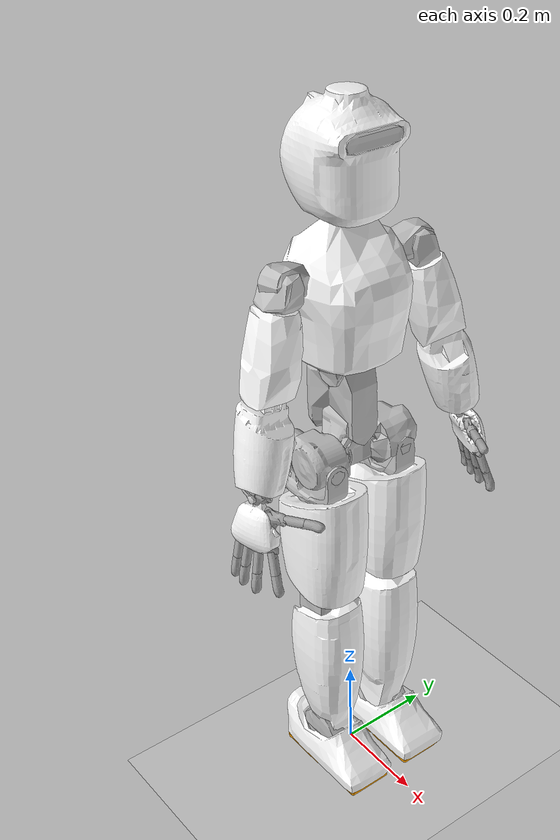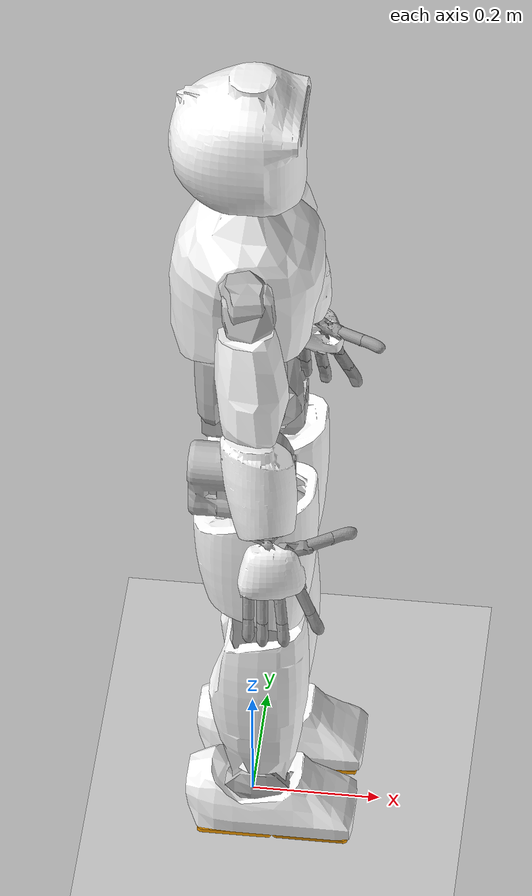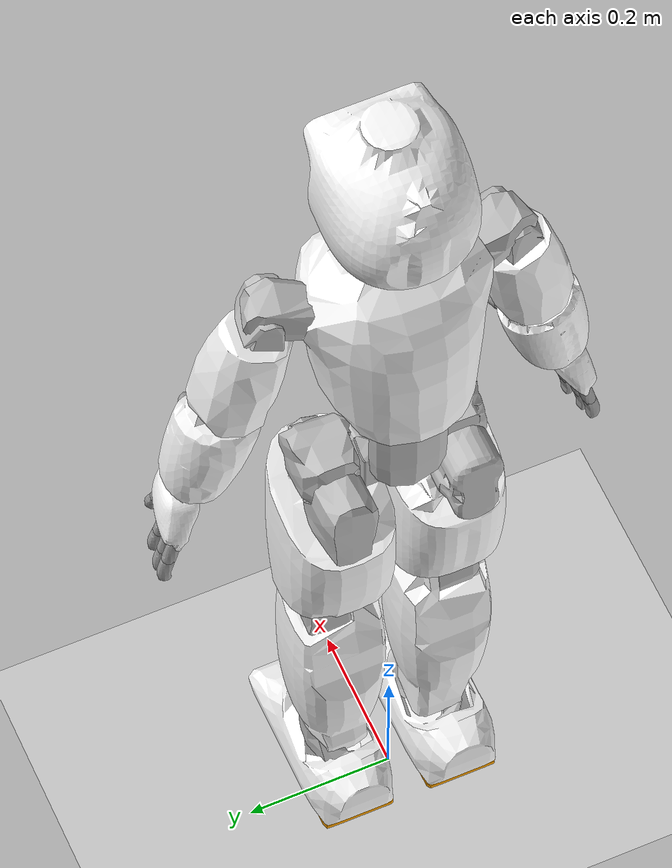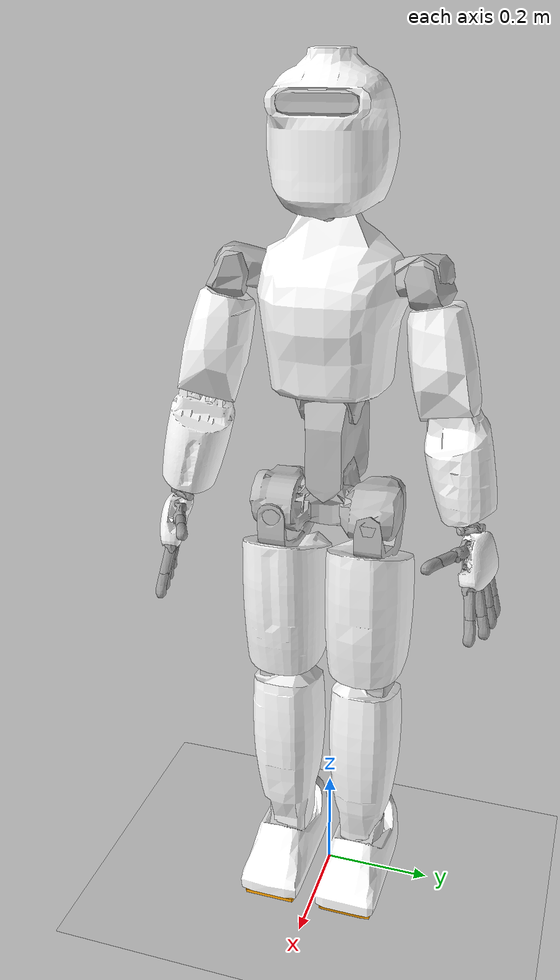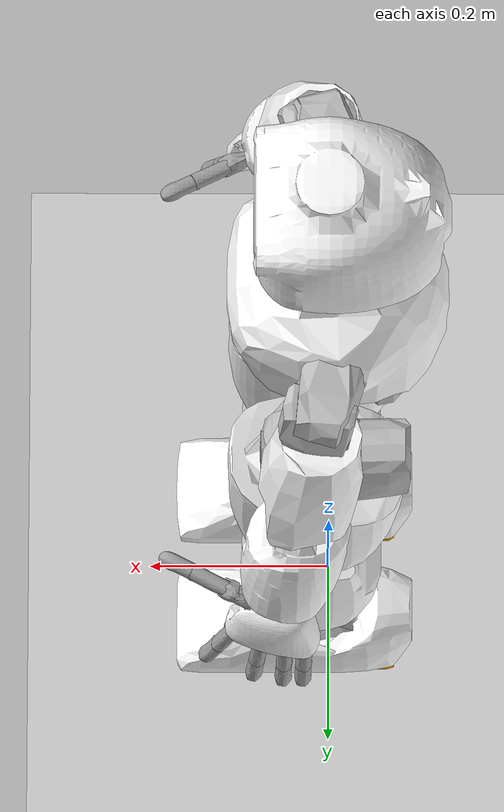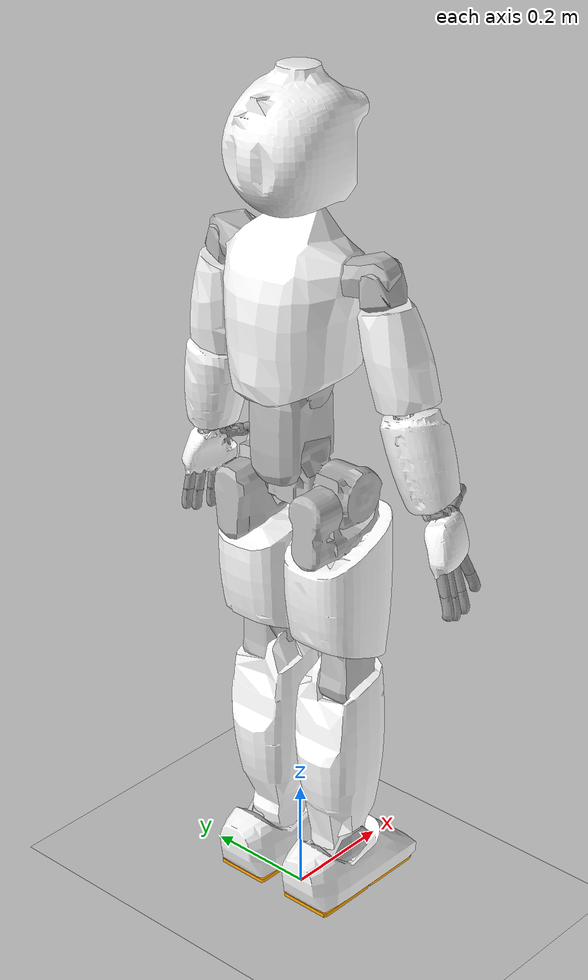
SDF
<?xml version="1.0"?>

<sdf version="1.11">
    <!-- Example world used to try ergocub in Gazebo -->
    <world name="tutorial_controlboard">
        <physics name="1ms" type="ignored">
            <max_step_size>0.001</max_step_size>
            <real_time_factor>1.0</real_time_factor>
            <max_contacts>4</max_contacts>
        </physics>
        <plugin
            filename="gz-sim-physics-system"
            name="gz::sim::systems::Physics">
        </plugin>
        <plugin
            filename="gz-sim-user-commands-system"
            name="gz::sim::systems::UserCommands">
        </plugin>
        <plugin
            filename="gz-sim-sensors-system"
            name="gz::sim::systems::Sensors">
        </plugin>
        <plugin
            filename="gz-sim-scene-broadcaster-system"
            name="gz::sim::systems::SceneBroadcaster">
        </plugin>
        <plugin
            filename="gz-sim-contact-system"
            name="gz::sim::systems::Contact">
        </plugin>

        <!-- YARP CLOCK -->
        <plugin
            filename="gz-sim-yarp-clock-system"
            name="gzyarp::Clock">
        </plugin>

        <light type="directional" name="sun">
            <cast_shadows>true</cast_shadows>
            <pose>0 0 10 0 0 0</pose>
            <diffuse>0.8 0.8 0.8 1</diffuse>
            <specular>0.2 0.2 0.2 1</specular>
            <attenuation>
                <range>1000</range>
                <constant>0.9</constant>
                <linear>0.01</linear>
                <quadratic>0.001</quadratic>
            </attenuation>
            <direction>-0.5 0.1 -0.9</direction>
        </light>

        <model name="ground_plane">
            <static>true</static>
            <link name="link">
                <collision name="collision">
                    <geometry>
                        <plane>
                            <normal>0 0 1</normal>
                            <size>100 100</size>
                        </plane>
                    </geometry>
                </collision>
                <visual name="visual">
                    <geometry>
                        <plane>
                            <normal>0 0 1</normal>
                            <size>100 100</size>
                        </plane>
                    </geometry>
                    <material>
                        <ambient>0.8 0.8 0.8 1</ambient>
                        <diffuse>0.8 0.8 0.8 1</diffuse>
                        <specular>0.8 0.8 0.8 1</specular>
                    </material>
                </visual>
            </link>
        </model>

        <include>
            <uri>model://ergoCub/robots/ergoCubGazeboV1_1_fixed</uri>
        </include>

    </world>
</sdf>

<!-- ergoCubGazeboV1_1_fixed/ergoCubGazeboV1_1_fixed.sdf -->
<sdf version='1.7'>
  <model name="ergocub_fixed">
    <include>
      <uri>model://ergoCub/robots/ergoCubGazeboV1_1</uri>
    </include>

  </model>
</sdf>

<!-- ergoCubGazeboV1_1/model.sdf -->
<sdf version='1.11'>
  <model name='ergoCub'>
    <link name='root_link'>
      <inertial>
        <pose>0.0024748962432214398 -0.0001050794470993344 0.023450368787955641 0 0 0</pose>
        <mass>2.8237514828246408</mass>
        <inertia>
          <ixx>0.0043800336692586869</ixx>
          <ixy>-1.436903968838589e-06</ixy>
          <ixz>1.4098441290530499e-05</ixz>
          <iyy>0.0056306062852994661</iyy>
          <iyz>-2.329934099458888e-05</iyz>
          <izz>0.003616681010808376</izz>
        </inertia>
      </inertial>
      <collision name='root_link_collision'>
        <pose>0 0 0 0 0 0</pose>
        <geometry>
          <mesh>
            <scale>0.001 0.001 0.001</scale>
            <uri>model://ergoCub/meshes/simmechanics/sim_ecub_1-1_root_link.stl</uri>
          </mesh>
        </geometry>
      </collision>
      <visual name='root_link_visual'>
        <pose>0 0 0 0 0 0</pose>
        <geometry>
          <mesh>
            <scale>0.001 0.001 0.001</scale>
            <uri>model://ergoCub/meshes/simmechanics/sim_ecub_1-1_root_link.stl</uri>
          </mesh>
        </geometry>
        <material>
          <diffuse>0.75000006 0.75000006 0.75000006 1</diffuse>
          <ambient>0.75000006 0.75000006 0.75000006 1</ambient>
        </material>
      </visual>
    </link>
    <joint name='l_hip_pitch' type='revolute'>
      <pose relative_to='root_link'>0.02109999999999964 0.050500000000000843 1.9428902930940239e-16
        3.958535957527503e-15 3.8109681721907007e-15 1.1674349118864061e-16</pose>
      <parent>root_link</parent>
      <child>l_hip_1</child>
      <axis>
        <xyz>-5.7728313799912843e-17 -1 -1.384383338166639e-17</xyz>
        <limit>
          <lower>-0.75049157835756175</lower>
          <upper>1.797689129554159</upper>
          <effort>1000000000</effort>
          <velocity>1000000000</velocity>
        </limit>
        <dynamics>
          <damping>2</damping>
          <friction>0</friction>
          <spring_reference>0</spring_reference>
          <spring_stiffness>0</spring_stiffness>
        </dynamics>
      </axis>
      <physics>
        <ode>
          <implicit_spring_damper>true</implicit_spring_damper>
          <cfm_damping>true</cfm_damping>
          <limit>
            <cfm>0</cfm>
            <erp>0.20000000000000001</erp>
          </limit>
        </ode>
      </physics>
    </joint>
    <link name='l_hip_1'>
      <pose relative_to='l_hip_pitch'>0 0 0 0 0 0</pose>
      <inertial>
        <pose>-0.004015422485162342 0.028247280560774649 -0.00068111439923831951 0 0 0</pose>
        <mass>2.2317688688596289</mass>
        <inertia>
          <ixx>0.0026953261284679369</ixx>
          <ixy>-5.9712554993795509e-05</ixy>
          <ixz>-5.8385350516582558e-06</ixz>
          <iyy>0.002210921814931001</iyy>
          <iyz>1.5432160879022371e-05</iyz>
          <izz>0.0024610381641843879</izz>
        </inertia>
      </inertial>
      <collision name='l_hip_1_collision'>
        <pose>0 0 0 0 0 0</pose>
        <geometry>
          <mesh>
            <scale>0.001 0.001 0.001</scale>
            <uri>model://ergoCub/meshes/simmechanics/sim_ecub_1-1_l_hip_1.stl</uri>
          </mesh>
        </geometry>
      </collision>
      <visual name='l_hip_1_visual'>
        <pose>0 0 0 0 0 0</pose>
        <geometry>
          <mesh>
            <scale>0.001 0.001 0.001</scale>
            <uri>model://ergoCub/meshes/simmechanics/sim_ecub_1-1_l_hip_1.stl</uri>
          </mesh>
        </geometry>
        <material>
          <diffuse>0.75000006 0.75000006 0.75000006 1</diffuse>
          <ambient>0.75000006 0.75000006 0.75000006 1</ambient>
        </material>
      </visual>
    </link>
    <joint name='l_hip_roll' type='revolute'>
      <pose relative_to='l_hip_1'>-0.047250000000000777 0.033099999999999997 -0.009000000000000119
        7.5842450244167319e-16 1.5745686587446741e-30 1.1102230246251551e-16</pose>
      <parent>l_hip_1</parent>
      <child>l_hip_2</child>
      <axis>
        <xyz>1 -6.1232339957367081e-17 6.3201403498236004e-16</xyz>
        <limit>
          <lower>-0.27925268031909273</lower>
          <upper>1.902408884673819</upper>
          <effort>1000000000</effort>
          <velocity>1000000000</velocity>
        </limit>
        <dynamics>
          <damping>2</damping>
          <friction>0</friction>
          <spring_reference>0</spring_reference>
          <spring_stiffness>0</spring_stiffness>
        </dynamics>
      </axis>
      <physics>
        <ode>
          <implicit_spring_damper>true</implicit_spring_damper>
          <cfm_damping>true</cfm_damping>
          <limit>
            <cfm>0</cfm>
            <erp>0.20000000000000001</erp>
          </limit>
        </ode>
      </physics>
    </joint>
    <link name='l_hip_2'>
      <pose relative_to='l_hip_roll'>0 0 0 0 0 0</pose>
      <inertial>
        <pose>-0.0041256970682994679 3.917475804630921e-05 -0.037509646035562727 0 0 0</pose>
        <mass>1.8338392164825099</mass>
        <inertia>
          <ixx>0.005488243677251951</ixx>
          <ixy>1.654281523522513e-06</ixy>
          <ixz>-2.190409388735156e-06</ixz>
          <iyy>0.0031595145959059318</iyy>
          <iyz>-0.00099773686074840413</iyz>
          <izz>0.0033984945726571129</izz>
        </inertia>
      </inertial>
      <collision name='l_hip_2_collision'>
        <pose>0 0 0 0 0 0</pose>
        <geometry>
          <mesh>
            <scale>0.001 0.001 0.001</scale>
            <uri>model://ergoCub/meshes/simmechanics/sim_ecub_1-1_l_hip_2.stl</uri>
          </mesh>
        </geometry>
      </collision>
      <visual name='l_hip_2_visual'>
        <pose>0 0 0 0 0 0</pose>
        <geometry>
          <mesh>
            <scale>0.001 0.001 0.001</scale>
            <uri>model://ergoCub/meshes/simmechanics/sim_ecub_1-1_l_hip_2.stl</uri>
          </mesh>
        </geometry>
        <material>
          <diffuse>0.75000006 0.75000006 0.75000006 1</diffuse>
          <ambient>0.75000006 0.75000006 0.75000006 1</ambient>
        </material>
      </visual>
    </link>
    <joint name='l_leg_ft_sensor' type='fixed'>
      <pose relative_to='l_hip_2'>0.036699999999999851 -1.387778780781446e-17 -0.08970000000000003
        -1.107579646272763e-15 -2.3847605106274891e-30 2.775557561562846e-16</pose>
      <parent>l_hip_2</parent>
      <child>l_hip_3</child>
      <axis>
        <dynamics>
          <spring_reference>0</spring_reference>
          <spring_stiffness>0</spring_stiffness>
        </dynamics>
        <xyz>0 0 1</xyz>
        <limit>
          <lower>-inf</lower>
          <upper>inf</upper>
        </limit>
      </axis>
      <physics>
        <ode>
          <limit>
            <cfm>0</cfm>
            <erp>0.20000000000000001</erp>
          </limit>
        </ode>
      </physics>
      <sensor name='l_leg_ft' type='force_torque'>
        <always_on>true</always_on>
        <update_rate>100</update_rate>
        <force_torque>
          <frame>sensor</frame>
          <measure_direction>child_to_parent</measure_direction>
        </force_torque>
        <pose>5.2041699999999996e-18 0 0 3.1415899999999999 -2.0213199324164966e-15
          2.6179899999999998</pose>
      </sensor>
    </joint>
    <link name='l_hip_3'>
      <pose relative_to='l_leg_ft_sensor'>0 0 0 0 0 0</pose>
      <inertial>
        <pose>0.0051761258395929613 -0.012828813026822291 -0.051748524474533993 0 0 0</pose>
        <mass>2.1475240840502461</mass>
        <inertia>
          <ixx>0.008197962692605143</ixx>
          <ixy>3.3213929541970179e-05</ixy>
          <ixz>0.00012474874840596019</ixz>
          <iyy>0.007242161971060034</iyy>
          <iyz>-2.5059855054008949e-05</iyz>
          <izz>0.0057274587727599866</izz>
        </inertia>
      </inertial>
      <collision name='l_hip_3_collision'>
        <pose>0 0 0 0 0 0</pose>
        <geometry>
          <mesh>
            <scale>0.001 0.001 0.001</scale>
            <uri>model://ergoCub/meshes/simmechanics/sim_ecub_1-1_l_hip_3.stl</uri>
          </mesh>
        </geometry>
      </collision>
      <visual name='l_hip_3_visual'>
        <pose>0 0 0 0 0 0</pose>
        <geometry>
          <mesh>
            <scale>0.001 0.001 0.001</scale>
            <uri>model://ergoCub/meshes/simmechanics/sim_ecub_1-1_l_hip_3.stl</uri>
          </mesh>
        </geometry>
        <material>
          <diffuse>1 1 1 1</diffuse>
          <ambient>1 1 1 1</ambient>
        </material>
      </visual>
    </link>
    <joint name='l_hip_yaw' type='revolute'>
      <pose relative_to='l_hip_3'>-8.4481033280070505e-16 -0.01499999999999994 -0.072699999999999931
        3.0118838875648332e-16 1.143142903721238e-14 -2.2204460492502611e-16</pose>
      <parent>l_hip_3</parent>
      <child>l_upper_leg</child>
      <axis>
        <xyz>-8.6225880117693566e-16 1.593666547307703e-16 1</xyz>
        <limit>
          <lower>-1.37881010907552</lower>
          <upper>1.37881010907552</upper>
          <effort>1000000000</effort>
          <velocity>1000000000</velocity>
        </limit>
        <dynamics>
          <damping>2</damping>
          <friction>0</friction>
          <spring_reference>0</spring_reference>
          <spring_stiffness>0</spring_stiffness>
        </dynamics>
      </axis>
      <physics>
        <ode>
          <implicit_spring_damper>true</implicit_spring_damper>
          <cfm_damping>true</cfm_damping>
          <limit>
            <cfm>0</cfm>
            <erp>0.20000000000000001</erp>
          </limit>
        </ode>
      </physics>
    </joint>
    <link name='l_upper_leg'>
      <pose relative_to='l_hip_yaw'>0 0 0 0 0 0</pose>
      <inertial>
        <pose>0.0085034946941601654 0.014484874736048651 -0.12674659802303309 0 0 0</pose>
        <mass>2.7849234317654532</mass>
        <inertia>
          <ixx>0.01210980714956794</ixx>
          <ixy>4.9071453193167162e-05</ixy>
          <ixz>0.0003920891864767038</ixz>
          <iyy>0.01185229395228421</iyy>
          <iyz>-0.0005393933817877802</iyz>
          <izz>0.0022536279167310689</izz>
        </inertia>
      </inertial>
      <collision name='l_upper_leg_collision'>
        <pose>0 0 0 0 0 0</pose>
        <geometry>
          <mesh>
            <scale>0.001 0.001 0.001</scale>
            <uri>model://ergoCub/meshes/simmechanics/sim_ecub_1-1_l_upper_leg.stl</uri>
          </mesh>
        </geometry>
      </collision>
      <visual name='l_upper_leg_visual'>
        <pose>0 0 0 0 0 0</pose>
        <geometry>
          <mesh>
            <scale>0.001 0.001 0.001</scale>
            <uri>model://ergoCub/meshes/simmechanics/sim_ecub_1-1_l_upper_leg.stl</uri>
          </mesh>
        </geometry>
        <material>
          <diffuse>0.75000006 0.75000006 0.75000006 1</diffuse>
          <ambient>0.75000006 0.75000006 0.75000006 1</ambient>
        </material>
      </visual>
    </link>
    <joint name='l_knee' type='revolute'>
      <pose relative_to='l_upper_leg'>0.010600000000000821 -0.0079000000000001847
        -0.17969999999999961 1.970486418692682e-16 -1.141942814663227e-14 2.860283993521143e-15</pose>
      <parent>l_upper_leg</parent>
      <child>l_lower_leg</child>
      <axis>
        <xyz>-2.6089375464113179e-16 -1 5.1665889551931108e-17</xyz>
        <limit>
          <lower>-1.815142422074103</lower>
          <upper>0.10471975511965979</upper>
          <effort>1000000000</effort>
          <velocity>1000000000</velocity>
        </limit>
        <dynamics>
          <damping>2</damping>
          <friction>0</friction>
          <spring_reference>0</spring_reference>
          <spring_stiffness>0</spring_stiffness>
        </dynamics>
      </axis>
      <physics>
        <ode>
          <implicit_spring_damper>true</implicit_spring_damper>
          <cfm_damping>true</cfm_damping>
          <limit>
            <cfm>0</cfm>
            <erp>0.20000000000000001</erp>
          </limit>
        </ode>
      </physics>
    </joint>
    <link name='l_lower_leg'>
      <pose relative_to='l_knee'>0 0 0 0 0 0</pose>
      <inertial>
        <pose>0.001420176808809015 0.0061863337439569746 -0.21383298861124969 0 0 0</pose>
        <mass>3.7675811452128878</mass>
        <inertia>
          <ixx>0.047767266414999177</ixx>
          <ixy>2.1189289797885979e-05</ixy>
          <ixz>0.0018123762001582069</ixz>
          <iyy>0.046471109000674748</iyy>
          <iyz>0.00081107102157240273</iyz>
          <izz>0.0048404912519552654</izz>
        </inertia>
      </inertial>
      <collision name='l_lower_leg_collision'>
        <pose>0 0 0 0 0 0</pose>
        <geometry>
          <mesh>
            <scale>0.001 0.001 0.001</scale>
            <uri>model://ergoCub/meshes/simmechanics/sim_ecub_1-1_l_lower_leg.stl</uri>
          </mesh>
        </geometry>
      </collision>
      <visual name='l_lower_leg_visual'>
        <pose>0 0 0 0 0 0</pose>
        <geometry>
          <mesh>
            <scale>0.001 0.001 0.001</scale>
            <uri>model://ergoCub/meshes/simmechanics/sim_ecub_1-1_l_lower_leg.stl</uri>
          </mesh>
        </geometry>
        <material>
          <diffuse>1 1 1 1</diffuse>
          <ambient>1 1 1 1</ambient>
        </material>
      </visual>
    </link>
    <joint name='l_ankle_pitch' type='revolute'>
      <pose relative_to='l_lower_leg'>-4.4686476741162551e-15 0.03189999999999981
        -0.32099999999999951 -1.970486418692703e-16 -8.6736173798801124e-19 -1.8683953730959561e-16</pose>
      <parent>l_lower_leg</parent>
      <child>l_ankle_1</child>
      <axis>
        <xyz>-2.389602037081462e-16 1 1.453827523173385e-16</xyz>
        <limit>
          <lower>-0.78539816339744828</lower>
          <upper>0.78539816339744828</upper>
          <effort>1000000000</effort>
          <velocity>1000000000</velocity>
        </limit>
        <dynamics>
          <damping>2</damping>
          <friction>0</friction>
          <spring_reference>0</spring_reference>
          <spring_stiffness>0</spring_stiffness>
        </dynamics>
      </axis>
      <physics>
        <ode>
          <implicit_spring_damper>true</implicit_spring_damper>
          <cfm_damping>true</cfm_damping>
          <limit>
            <cfm>0</cfm>
            <erp>0.20000000000000001</erp>
          </limit>
        </ode>
      </physics>
    </joint>
    <link name='l_ankle_1'>
      <pose relative_to='l_ankle_pitch'>0 0 0 0 0 0</pose>
      <inertial>
        <pose>-0.001385212506717644 0.00066018696000964827 -0.014087432474325199 0 0 0</pose>
        <mass>0.34812789515191822</mass>
        <inertia>
          <ixx>0.01</ixx>
          <ixy>8.8820761287703365e-06</ixy>
          <ixz>-5.5239266791031688e-05</ixz>
          <iyy>0.01</iyy>
          <iyz>7.8684435557279372e-06</iyz>
          <izz>0.01</izz>
        </inertia>
      </inertial>
      <collision name='l_ankle_1_collision'>
        <pose>0 0 0 0 0 0</pose>
        <geometry>
          <mesh>
            <scale>0.001 0.001 0.001</scale>
            <uri>model://ergoCub/meshes/simmechanics/sim_ecub_1-1_l_ankle_1.stl</uri>
          </mesh>
        </geometry>
      </collision>
      <visual name='l_ankle_1_visual'>
        <pose>0 0 0 0 0 0</pose>
        <geometry>
          <mesh>
            <scale>0.001 0.001 0.001</scale>
            <uri>model://ergoCub/meshes/simmechanics/sim_ecub_1-1_l_ankle_1.stl</uri>
          </mesh>
        </geometry>
        <material>
          <diffuse>0.75000006 0.75000006 0.75000006 1</diffuse>
          <ambient>0.75000006 0.75000006 0.75000006 1</ambient>
        </material>
      </visual>
    </link>
    <joint name='l_ankle_roll' type='revolute'>
      <pose relative_to='l_ankle_1'>-0.052750000000000317 -0.018199999999999911
        -0.034999999999999587 3.3401966467506259e-19 1.1217589357404029e-14 -2.3665827156630351e-30</pose>
      <parent>l_ankle_1</parent>
      <child>l_ankle_2</child>
      <axis>
        <xyz>1 -4.05028482201375e-16 -1.2496691978128871e-15</xyz>
        <limit>
          <lower>-0.43633231299858238</lower>
          <upper>0.43633231299858238</upper>
          <effort>1000000000</effort>
          <velocity>1000000000</velocity>
        </limit>
        <dynamics>
          <damping>2</damping>
          <friction>0</friction>
          <spring_reference>0</spring_reference>
          <spring_stiffness>0</spring_stiffness>
        </dynamics>
      </axis>
      <physics>
        <ode>
          <implicit_spring_damper>true</implicit_spring_damper>
          <cfm_damping>true</cfm_damping>
          <limit>
            <cfm>0</cfm>
            <erp>0.20000000000000001</erp>
          </limit>
        </ode>
      </physics>
    </joint>
    <link name='l_ankle_2'>
      <pose relative_to='l_ankle_roll'>0 0 0 0 0 0</pose>
      <inertial>
        <pose>0.040522400508854167 -9.7907516467141131e-05 -0.02387114353368602 0 0 0</pose>
        <mass>1.5418216247038541</mass>
        <inertia>
          <ixx>0.01</ixx>
          <ixy>-1.9973294407367239e-05</ixy>
          <ixz>-1.507060259301222e-05</ixz>
          <iyy>0.01</iyy>
          <iyz>-0.001325132568751294</iyz>
          <izz>0.01</izz>
        </inertia>
      </inertial>
      <collision name='l_ankle_2_collision'>
        <pose>0 0 0 0 0 0</pose>
        <geometry>
          <mesh>
            <scale>0.001 0.001 0.001</scale>
            <uri>model://ergoCub/meshes/simmechanics/sim_ecub_1-1_l_ankle_2.stl</uri>
          </mesh>
        </geometry>
      </collision>
      <visual name='l_ankle_2_visual'>
        <pose>0 0 0 0 0 0</pose>
        <geometry>
          <mesh>
            <scale>0.001 0.001 0.001</scale>
            <uri>model://ergoCub/meshes/simmechanics/sim_ecub_1-1_l_ankle_2.stl</uri>
          </mesh>
        </geometry>
        <material>
          <diffuse>1 1 1 1</diffuse>
          <ambient>1 1 1 1</ambient>
        </material>
      </visual>
    </link>
    <joint name='l_foot_front_ft_sensor' type='fixed'>
      <pose relative_to='l_ankle_2'>0.13525000000000001 -5.5511151231257827e-17
        -0.047899999999999172 -8.751425667295598e-31 1.9428902930939909e-16 -9.7889463854681524e-16</pose>
      <parent>l_ankle_2</parent>
      <child>l_foot_front</child>
      <axis>
        <dynamics>
          <spring_reference>0</spring_reference>
          <spring_stiffness>0</spring_stiffness>
        </dynamics>
        <xyz>0 0 1</xyz>
        <limit>
          <lower>-inf</lower>
          <upper>inf</upper>
        </limit>
      </axis>
      <physics>
        <ode>
          <limit>
            <cfm>0</cfm>
            <erp>0.20000000000000001</erp>
          </limit>
        </ode>
      </physics>
      <sensor name='l_foot_front_ft' type='force_torque'>
        <always_on>true</always_on>
        <update_rate>100</update_rate>
        <force_torque>
          <frame>sensor</frame>
          <measure_direction>parent_to_child</measure_direction>
        </force_torque>
        <pose>0 0 0 1.2566700000000003e-16 2.2011199999999993e-17 -2.0943999999999998</pose>
      </sensor>
    </joint>
    <link name='l_foot_front'>
      <pose relative_to='l_foot_front_ft_sensor'>0 0 0 0 0 0</pose>
      <inertial>
        <pose>0.00058792029112601785 -3.7479242764870691e-09 -0.020000616615901912 0 0 0</pose>
        <mass>0.221104679395528</mass>
        <inertia>
          <ixx>0.01</ixx>
          <ixy>0</ixy>
          <ixz>0</ixz>
          <iyy>0.01</iyy>
          <iyz>3.470646683126688e-09</iyz>
          <izz>0.01</izz>
        </inertia>
      </inertial>
      <collision name='l_foot_front_collision'>
        <pose>0 0 -0.019300000000000001 0 0 0</pose>
        <geometry>
          <box>
            <size>0.11700000000000001 0.10000000000000001 0.0060000000000000001</size>
          </box>
        </geometry>
        <surface>
          <bounce>
            <restitution_coefficient>0</restitution_coefficient>
            <threshold>100000</threshold>
          </bounce>
          <contact>
            <ode>
              <kp>18000000</kp>
              <kd>100</kd>
              <max_vel>100</max_vel>
              <min_depth>0.0001</min_depth>
            </ode>
          </contact>
          <friction>
            <ode>
              <mu>1</mu>
              <mu2>1</mu2>
              <fdir1>0 0 0</fdir1>
            </ode>
          </friction>
        </surface>
        <max_contacts>4</max_contacts>
      </collision>
      <visual name='l_foot_front_visual'>
        <pose>0 0 0 0 0 0</pose>
        <geometry>
          <mesh>
            <scale>0.001 0.001 0.001</scale>
            <uri>model://ergoCub/meshes/simmechanics/sim_ecub_1-1_l_foot_front.stl</uri>
          </mesh>
        </geometry>
        <material>
          <diffuse>1 0.637499988 0 1</diffuse>
          <ambient>1 0.637499988 0 1</ambient>
        </material>
      </visual>
      <sensor name='l_foot_front_ft_imu' type='imu'>
        <always_on>true</always_on>
        <update_rate>100</update_rate>
        <pose>0 0 0 1.2566700000000003e-16 2.2011199999999993e-17 -2.0943999999999998</pose>
      </sensor>
    </link>
    <joint name='l_foot_rear_ft_sensor' type='fixed'>
      <pose relative_to='l_ankle_2'>0.01599999999999999 -4.163336342344337e-17 -0.047899999999999943
        -1.0970096963229701e-30 1.9428902930939749e-16 2.030608361582683e-17</pose>
      <parent>l_ankle_2</parent>
      <child>l_foot_rear</child>
      <axis>
        <dynamics>
          <spring_reference>0</spring_reference>
          <spring_stiffness>0</spring_stiffness>
        </dynamics>
        <xyz>0 0 1</xyz>
        <limit>
          <lower>-inf</lower>
          <upper>inf</upper>
        </limit>
      </axis>
      <physics>
        <ode>
          <limit>
            <cfm>0</cfm>
            <erp>0.20000000000000001</erp>
          </limit>
        </ode>
      </physics>
      <sensor name='l_foot_rear_ft' type='force_torque'>
        <always_on>true</always_on>
        <update_rate>100</update_rate>
        <force_torque>
          <frame>sensor</frame>
          <measure_direction>parent_to_child</measure_direction>
        </force_torque>
        <pose>0 0 0 1.2566700000000003e-16 2.2011199999999993e-17 -2.0943999999999998</pose>
      </sensor>
    </joint>
    <link name='l_foot_rear'>
      <pose relative_to='l_foot_rear_ft_sensor'>0 0 0 0 0 0</pose>
      <inertial>
        <pose>0.00058792029112595713 -3.7479242903648569e-09 -0.020000616615901579 0 0 0</pose>
        <mass>0.221104679395528</mass>
        <inertia>
          <ixx>0.01</ixx>
          <ixy>0</ixy>
          <ixz>0</ixz>
          <iyy>0.01</iyy>
          <iyz>3.4706466744864879e-09</iyz>
          <izz>0.01</izz>
        </inertia>
      </inertial>
      <collision name='l_foot_rear_collision'>
        <pose>0 0 -0.019300000000000001 0 0 0</pose>
        <geometry>
          <box>
            <size>0.11700000000000001 0.10000000000000001 0.0060000000000000001</size>
          </box>
        </geometry>
        <surface>
          <bounce>
            <restitution_coefficient>0</restitution_coefficient>
            <threshold>100000</threshold>
          </bounce>
          <contact>
            <ode>
              <kp>18000000</kp>
              <kd>100</kd>
              <max_vel>100</max_vel>
              <min_depth>0.0001</min_depth>
            </ode>
          </contact>
          <friction>
            <ode>
              <mu>1</mu>
              <mu2>1</mu2>
              <fdir1>0 0 0</fdir1>
            </ode>
          </friction>
        </surface>
        <max_contacts>4</max_contacts>
      </collision>
      <visual name='l_foot_rear_visual'>
        <pose>0 0 0 0 0 0</pose>
        <geometry>
          <mesh>
            <scale>0.001 0.001 0.001</scale>
            <uri>model://ergoCub/meshes/simmechanics/sim_ecub_1-1_l_foot_rear.stl</uri>
          </mesh>
        </geometry>
        <material>
          <diffuse>1 0.637499988 0 1</diffuse>
          <ambient>1 0.637499988 0 1</ambient>
        </material>
      </visual>
      <sensor name='l_foot_rear_ft_imu' type='imu'>
        <always_on>true</always_on>
        <update_rate>100</update_rate>
        <pose>0 0 0 1.2566700000000003e-16 2.2011199999999993e-17 -2.0943999999999998</pose>
      </sensor>
    </link>
    <joint name='r_hip_pitch' type='revolute'>
      <pose relative_to='root_link'>0.02109999999999964 -0.050499999999999171
        -2.2204460492503131e-16 3.9862236242908389e-15 9.0123286684225007e-14 4.9789962505506032e-17</pose>
      <parent>root_link</parent>
      <child>r_hip_1</child>
      <axis>
        <xyz>-1.088051398938607e-16 -1 1.3843833381660081e-17</xyz>
        <limit>
          <lower>-0.75049157835756175</lower>
          <upper>1.797689129554159</upper>
          <effort>1000000000</effort>
          <velocity>1000000000</velocity>
        </limit>
        <dynamics>
          <damping>2</damping>
          <friction>0</friction>
          <spring_reference>0</spring_reference>
          <spring_stiffness>0</spring_stiffness>
        </dynamics>
      </axis>
      <physics>
        <ode>
          <implicit_spring_damper>true</implicit_spring_damper>
          <cfm_damping>true</cfm_damping>
          <limit>
            <cfm>0</cfm>
            <erp>0.20000000000000001</erp>
          </limit>
        </ode>
      </physics>
    </joint>
    <link name='r_hip_1'>
      <pose relative_to='r_hip_pitch'>0 0 0 0 0 0</pose>
      <inertial>
        <pose>-0.0040321177302587406 -0.028249385885545361 -0.0006739019720396755 0 0 0</pose>
        <mass>2.2320852637398949</mass>
        <inertia>
          <ixx>0.002695545891317729</ixx>
          <ixy>6.1267205360208651e-05</ixy>
          <ixz>6.4433555224604787e-06</ixz>
          <iyy>0.0022122594774356399</iyy>
          <iyz>1.5035655169600431e-05</iyz>
          <izz>0.0024608876750051721</izz>
        </inertia>
      </inertial>
      <collision name='r_hip_1_collision'>
        <pose>0 0 0 0 0 0</pose>
        <geometry>
          <mesh>
            <scale>0.001 0.001 0.001</scale>
            <uri>model://ergoCub/meshes/simmechanics/sim_ecub_1-1_r_hip_1.stl</uri>
          </mesh>
        </geometry>
      </collision>
      <visual name='r_hip_1_visual'>
        <pose>0 0 0 0 0 0</pose>
        <geometry>
          <mesh>
            <scale>0.001 0.001 0.001</scale>
            <uri>model://ergoCub/meshes/simmechanics/sim_ecub_1-1_r_hip_1.stl</uri>
          </mesh>
        </geometry>
        <material>
          <diffuse>0.75000006 0.75000006 0.75000006 1</diffuse>
          <ambient>0.75000006 0.75000006 0.75000006 1</ambient>
        </material>
      </visual>
    </link>
    <joint name='r_hip_roll' type='revolute'>
      <pose relative_to='r_hip_1'>-0.047250000000000618 -0.033099999999999817 -0.0090000000000000913
        -2.7331615605482602e-16 2.5046413910249769e-16 -3.103637768144789e-15</pose>
      <parent>r_hip_1</parent>
      <child>r_hip_2</child>
      <axis>
        <xyz>-1 -3.3813287685016302e-16 -7.1202277054512189e-17</xyz>
        <limit>
          <lower>-0.27925268031909273</lower>
          <upper>1.902408884673819</upper>
          <effort>1000000000</effort>
          <velocity>1000000000</velocity>
        </limit>
        <dynamics>
          <damping>2</damping>
          <friction>0</friction>
          <spring_reference>0</spring_reference>
          <spring_stiffness>0</spring_stiffness>
        </dynamics>
      </axis>
      <physics>
        <ode>
          <implicit_spring_damper>true</implicit_spring_damper>
          <cfm_damping>true</cfm_damping>
          <limit>
            <cfm>0</cfm>
            <erp>0.20000000000000001</erp>
          </limit>
        </ode>
      </physics>
    </joint>
    <link name='r_hip_2'>
      <pose relative_to='r_hip_roll'>0 0 0 0 0 0</pose>
      <inertial>
        <pose>-0.004338858395565106 -4.2767854114084132e-05 -0.037115837283052837 0 0 0</pose>
        <mass>1.842537408352412</mass>
        <inertia>
          <ixx>0.0054591661132700657</ixx>
          <ixy>-2.3735315120347878e-06</ixy>
          <ixz>-1.852398406117554e-06</ixz>
          <iyy>0.0031203032496471129</iyy>
          <iyz>-0.001012468524792514</iyz>
          <izz>0.0034190028448521578</izz>
        </inertia>
      </inertial>
      <collision name='r_hip_2_collision'>
        <pose>0 0 0 0 0 0</pose>
        <geometry>
          <mesh>
            <scale>0.001 0.001 0.001</scale>
            <uri>model://ergoCub/meshes/simmechanics/sim_ecub_1-1_r_hip_2.stl</uri>
          </mesh>
        </geometry>
      </collision>
      <visual name='r_hip_2_visual'>
        <pose>0 0 0 0 0 0</pose>
        <geometry>
          <mesh>
            <scale>0.001 0.001 0.001</scale>
            <uri>model://ergoCub/meshes/simmechanics/sim_ecub_1-1_r_hip_2.stl</uri>
          </mesh>
        </geometry>
        <material>
          <diffuse>0.75000006 0.75000006 0.75000006 1</diffuse>
          <ambient>0.75000006 0.75000006 0.75000006 1</ambient>
        </material>
      </visual>
    </link>
    <joint name='r_leg_ft_sensor' type='fixed'>
      <pose relative_to='r_hip_2'>0.036699999999999983 -5.5511151231257827e-17 -0.089699999999999919
        -1.3775953441385739e-15 5.4908280228866508e-16 1.6105578736269431e-15</pose>
      <parent>r_hip_2</parent>
      <child>r_hip_3</child>
      <axis>
        <dynamics>
          <spring_reference>0</spring_reference>
          <spring_stiffness>0</spring_stiffness>
        </dynamics>
        <xyz>0 0 1</xyz>
        <limit>
          <lower>-inf</lower>
          <upper>inf</upper>
        </limit>
      </axis>
      <physics>
        <ode>
          <limit>
            <cfm>0</cfm>
            <erp>0.20000000000000001</erp>
          </limit>
        </ode>
      </physics>
      <sensor name='r_leg_ft' type='force_torque'>
        <always_on>true</always_on>
        <update_rate>100</update_rate>
        <force_torque>
          <frame>sensor</frame>
          <measure_direction>child_to_parent</measure_direction>
        </force_torque>
        <pose>1.21431e-17 2.7755599999999997e-17 5.5511199999999995e-17 3.1415899999999999
          2.9888097527371862e-16 -2.6179899999999998</pose>
      </sensor>
    </joint>
    <link name='r_hip_3'>
      <pose relative_to='r_leg_ft_sensor'>0 0 0 0 0 0</pose>
      <inertial>
        <pose>0.0051010124501877467 0.01283209274414525 -0.051688425028262763 0 0 0</pose>
        <mass>2.1479000580665848</mass>
        <inertia>
          <ixx>0.0081490016653895277</ixx>
          <ixy>-3.4987271175667068e-05</ixy>
          <ixz>-0.0001257278337246898</ixz>
          <iyy>0.0071931775231357919</iyy>
          <iyz>-2.409673844055386e-05</iyz>
          <izz>0.0057278283877820486</izz>
        </inertia>
      </inertial>
      <collision name='r_hip_3_collision'>
        <pose>0 0 0 0 0 0</pose>
        <geometry>
          <mesh>
            <scale>0.001 0.001 0.001</scale>
            <uri>model://ergoCub/meshes/simmechanics/sim_ecub_1-1_r_hip_3.stl</uri>
          </mesh>
        </geometry>
      </collision>
      <visual name='r_hip_3_visual'>
        <pose>0 0 0 0 0 0</pose>
        <geometry>
          <mesh>
            <scale>0.001 0.001 0.001</scale>
            <uri>model://ergoCub/meshes/simmechanics/sim_ecub_1-1_r_hip_3.stl</uri>
          </mesh>
        </geometry>
        <material>
          <diffuse>1 1 1 1</diffuse>
          <ambient>1 1 1 1</ambient>
        </material>
      </visual>
    </link>
    <joint name='r_hip_yaw' type='revolute'>
      <pose relative_to='r_hip_3'>-2.8622937353617322e-16 0.014999999999999779 -0.07269999999999871
        -3.9451416337953303e-15 7.4301230721464534e-16 1.219315774954028e-06</pose>
      <parent>r_hip_3</parent>
      <child>r_upper_leg</child>
      <axis>
        <xyz>-2.395305020743351e-20 1.4749328491810951e-15 -1</xyz>
        <limit>
          <lower>-1.37881010907552</lower>
          <upper>1.37881010907552</upper>
          <effort>1000000000</effort>
          <velocity>1000000000</velocity>
        </limit>
        <dynamics>
          <damping>2</damping>
          <friction>0</friction>
          <spring_reference>0</spring_reference>
          <spring_stiffness>0</spring_stiffness>
        </dynamics>
      </axis>
      <physics>
        <ode>
          <implicit_spring_damper>true</implicit_spring_damper>
          <cfm_damping>true</cfm_damping>
          <limit>
            <cfm>0</cfm>
            <erp>0.20000000000000001</erp>
          </limit>
        </ode>
      </physics>
    </joint>
    <link name='r_upper_leg'>
      <pose relative_to='r_hip_yaw'>0 0 0 0 0 0</pose>
      <inertial>
        <pose>0.0084674563826789215 -0.01446847602698749 -0.1267496055718563 0 0 0</pose>
        <mass>2.784923431729287</mass>
        <inertia>
          <ixx>0.012109133352085039</ixx>
          <ixy>-5.4554502413726351e-05</ixy>
          <ixz>-0.00040331041015480859</ixz>
          <iyy>0.011860132529998121</iyy>
          <iyz>-0.0005393573740676439</iyz>
          <izz>0.002260970690769323</izz>
        </inertia>
      </inertial>
      <collision name='r_upper_leg_collision'>
        <pose>0 0 0 0 0 0</pose>
        <geometry>
          <mesh>
            <scale>0.001 0.001 0.001</scale>
            <uri>model://ergoCub/meshes/simmechanics/sim_ecub_1-1_r_upper_leg.stl</uri>
          </mesh>
        </geometry>
      </collision>
      <visual name='r_upper_leg_visual'>
        <pose>0 0 0 0 0 0</pose>
        <geometry>
          <mesh>
            <scale>0.001 0.001 0.001</scale>
            <uri>model://ergoCub/meshes/simmechanics/sim_ecub_1-1_r_upper_leg.stl</uri>
          </mesh>
        </geometry>
        <material>
          <diffuse>0.75000006 0.75000006 0.75000006 1</diffuse>
          <ambient>0.75000006 0.75000006 0.75000006 1</ambient>
        </material>
      </visual>
    </link>
    <joint name='r_knee' type='revolute'>
      <pose relative_to='r_upper_leg'>0.01060000963260985 0.0078999870752592891 -0.17970000000000061
        6.8926432619353366e-14 -6.6501593618806416e-14 -1.2193157700904429e-06</pose>
      <parent>r_upper_leg</parent>
      <child>r_lower_leg</child>
      <axis>
        <xyz>1.2193157766326319e-06 -0.99999999999925659 4.7195511606589226e-15</xyz>
        <limit>
          <lower>-1.815142422074103</lower>
          <upper>0.10471975511965979</upper>
          <effort>1000000000</effort>
          <velocity>1000000000</velocity>
        </limit>
        <dynamics>
          <damping>2</damping>
          <friction>0</friction>
          <spring_reference>0</spring_reference>
          <spring_stiffness>0</spring_stiffness>
        </dynamics>
      </axis>
      <physics>
        <ode>
          <implicit_spring_damper>true</implicit_spring_damper>
          <cfm_damping>true</cfm_damping>
          <limit>
            <cfm>0</cfm>
            <erp>0.20000000000000001</erp>
          </limit>
        </ode>
      </physics>
    </joint>
    <link name='r_lower_leg'>
      <pose relative_to='r_knee'>0 0 0 0 0 0</pose>
      <inertial>
        <pose>0.001215768916455091 -0.0061847345853468932 -0.213727598798682 0 0 0</pose>
        <mass>3.7621532589747919</mass>
        <inertia>
          <ixx>0.047738936736850403</ixx>
          <ixy>-3.7269274872190179e-05</ixy>
          <ixz>-0.001804298172118346</ixz>
          <iyy>0.046442156168219367</iyy>
          <iyz>0.00085198859046338449</iyz>
          <izz>0.0048396718635005482</izz>
        </inertia>
      </inertial>
      <collision name='r_lower_leg_collision'>
        <pose>0 0 0 0 0 0</pose>
        <geometry>
          <mesh>
            <scale>0.001 0.001 0.001</scale>
            <uri>model://ergoCub/meshes/simmechanics/sim_ecub_1-1_r_lower_leg.stl</uri>
          </mesh>
        </geometry>
      </collision>
      <visual name='r_lower_leg_visual'>
        <pose>0 0 0 0 0 0</pose>
        <geometry>
          <mesh>
            <scale>0.001 0.001 0.001</scale>
            <uri>model://ergoCub/meshes/simmechanics/sim_ecub_1-1_r_lower_leg.stl</uri>
          </mesh>
        </geometry>
        <material>
          <diffuse>1 1 1 1</diffuse>
          <ambient>1 1 1 1</ambient>
        </material>
      </visual>
    </link>
    <joint name='r_ankle_pitch' type='revolute'>
      <pose relative_to='r_lower_leg'>-5.9362237347926339e-15 -0.031900000000000053
        -0.32100000000000017 -2.993280557641417e-15 -2.0242047360524569e-14 8.8806367889378016e-17</pose>
      <parent>r_lower_leg</parent>
      <child>r_ankle_1</child>
      <axis>
        <xyz>-3.5052643664412631e-17 1 -1.3313170223471391e-16</xyz>
        <limit>
          <lower>-0.78539816339744828</lower>
          <upper>0.78539816339744828</upper>
          <effort>1000000000</effort>
          <velocity>1000000000</velocity>
        </limit>
        <dynamics>
          <damping>2</damping>
          <friction>0</friction>
          <spring_reference>0</spring_reference>
          <spring_stiffness>0</spring_stiffness>
        </dynamics>
      </axis>
      <physics>
        <ode>
          <implicit_spring_damper>true</implicit_spring_damper>
          <cfm_damping>true</cfm_damping>
          <limit>
            <cfm>0</cfm>
            <erp>0.20000000000000001</erp>
          </limit>
        </ode>
      </physics>
    </joint>
    <link name='r_ankle_1'>
      <pose relative_to='r_ankle_pitch'>0 0 0 0 0 0</pose>
      <inertial>
        <pose>-0.001417230974694688 -0.00066018695902093916 -0.014087432401547639 0 0 0</pose>
        <mass>0.34812789506355563</mass>
        <inertia>
          <ixx>0.01</ixx>
          <ixy>-8.9918732017841873e-06</ixy>
          <ixz>5.5239266965796567e-05</ixz>
          <iyy>0.01</iyy>
          <iyz>1.0336975691919179e-05</iyz>
          <izz>0.01</izz>
        </inertia>
      </inertial>
      <collision name='r_ankle_1_collision'>
        <pose>0 0 0 0 0 0</pose>
        <geometry>
          <mesh>
            <scale>0.001 0.001 0.001</scale>
            <uri>model://ergoCub/meshes/simmechanics/sim_ecub_1-1_r_ankle_1.stl</uri>
          </mesh>
        </geometry>
      </collision>
      <visual name='r_ankle_1_visual'>
        <pose>0 0 0 0 0 0</pose>
        <geometry>
          <mesh>
            <scale>0.001 0.001 0.001</scale>
            <uri>model://ergoCub/meshes/simmechanics/sim_ecub_1-1_r_ankle_1.stl</uri>
          </mesh>
        </geometry>
        <material>
          <diffuse>0.75000006 0.75000006 0.75000006 1</diffuse>
          <ambient>0.75000006 0.75000006 0.75000006 1</ambient>
        </material>
      </visual>
    </link>
    <joint name='r_ankle_roll' type='revolute'>
      <pose relative_to='r_ankle_1'>-0.052750000000001553 0.018200000000000011 -0.0349999999999977
        -1.017605324186138e-24 3.8838282931741332e-14 -9.2786221991157071e-23</pose>
      <parent>r_ankle_1</parent>
      <child>r_ankle_2</child>
      <axis>
        <xyz>-1 -1.628246671334752e-16 2.5602956225604131e-15</xyz>
        <limit>
          <lower>-0.43633231299858238</lower>
          <upper>0.43633231299858238</upper>
          <effort>1000000000</effort>
          <velocity>1000000000</velocity>
        </limit>
        <dynamics>
          <damping>2</damping>
          <friction>0</friction>
          <spring_reference>0</spring_reference>
          <spring_stiffness>0</spring_stiffness>
        </dynamics>
      </axis>
      <physics>
        <ode>
          <implicit_spring_damper>true</implicit_spring_damper>
          <cfm_damping>true</cfm_damping>
          <limit>
            <cfm>0</cfm>
            <erp>0.20000000000000001</erp>
          </limit>
        </ode>
      </physics>
    </joint>
    <link name='r_ankle_2'>
      <pose relative_to='r_ankle_roll'>0 0 0 0 0 0</pose>
      <inertial>
        <pose>0.040476468116960353 -8.6424930989786874e-05 -0.0238711435337009 0 0 0</pose>
        <mass>1.5418216247038541</mass>
        <inertia>
          <ixx>0.01</ixx>
          <ixy>-2.3071453411386869e-05</ixy>
          <ixz>-3.0777177071446109e-05</ixz>
          <iyy>0.01</iyy>
          <iyz>-0.0013223759105872521</iyz>
          <izz>0.01</izz>
        </inertia>
      </inertial>
      <collision name='r_ankle_2_collision'>
        <pose>0 0 0 0 0 0</pose>
        <geometry>
          <mesh>
            <scale>0.001 0.001 0.001</scale>
            <uri>model://ergoCub/meshes/simmechanics/sim_ecub_1-1_r_ankle_2.stl</uri>
          </mesh>
        </geometry>
      </collision>
      <visual name='r_ankle_2_visual'>
        <pose>0 0 0 0 0 0</pose>
        <geometry>
          <mesh>
            <scale>0.001 0.001 0.001</scale>
            <uri>model://ergoCub/meshes/simmechanics/sim_ecub_1-1_r_ankle_2.stl</uri>
          </mesh>
        </geometry>
        <material>
          <diffuse>1 1 1 1</diffuse>
          <ambient>1 1 1 1</ambient>
        </material>
      </visual>
    </link>
    <joint name='r_foot_front_ft_sensor' type='fixed'>
      <pose relative_to='r_ankle_2'>0.13525000000000001 0 -0.047899999999999943
        2.6613913647137401e-17 -9.2081136924205497e-17 -1.455188838580441e-15</pose>
      <parent>r_ankle_2</parent>
      <child>r_foot_front</child>
      <axis>
        <dynamics>
          <spring_reference>0</spring_reference>
          <spring_stiffness>0</spring_stiffness>
        </dynamics>
        <xyz>0 0 1</xyz>
        <limit>
          <lower>-inf</lower>
          <upper>inf</upper>
        </limit>
      </axis>
      <physics>
        <ode>
          <limit>
            <cfm>0</cfm>
            <erp>0.20000000000000001</erp>
          </limit>
        </ode>
      </physics>
      <sensor name='r_foot_front_ft' type='force_torque'>
        <always_on>true</always_on>
        <update_rate>100</update_rate>
        <force_torque>
          <frame>sensor</frame>
          <measure_direction>parent_to_child</measure_direction>
        </force_torque>
        <pose>0 1.3877799999999999e-17 1.11022e-16 -1.0903000000000002e-16 -1.4422200000000001e-16
          -2.0943999999999998</pose>
      </sensor>
    </joint>
    <link name='r_foot_front'>
      <pose relative_to='r_foot_front_ft_sensor'>0 0 0 0 0 0</pose>
      <inertial>
        <pose>0.00058792029113856337 -3.7479450931687808e-09 -0.020000616615899029 0 0 0</pose>
        <mass>0.221104679395528</mass>
        <inertia>
          <ixx>0.01</ixx>
          <ixy>0</ixy>
          <ixz>0</ixz>
          <iyy>0.01</iyy>
          <iyz>3.470646690402646e-09</iyz>
          <izz>0.01</izz>
        </inertia>
      </inertial>
      <collision name='r_foot_front_collision'>
        <pose>0 0 -0.019300000000000001 0 0 0</pose>
        <geometry>
          <box>
            <size>0.11700000000000001 0.10000000000000001 0.0060000000000000001</size>
          </box>
        </geometry>
        <surface>
          <bounce>
            <restitution_coefficient>0</restitution_coefficient>
            <threshold>100000</threshold>
          </bounce>
          <contact>
            <ode>
              <kp>18000000</kp>
              <kd>100</kd>
              <max_vel>100</max_vel>
              <min_depth>0.0001</min_depth>
            </ode>
          </contact>
          <friction>
            <ode>
              <mu>1</mu>
              <mu2>1</mu2>
              <fdir1>0 0 0</fdir1>
            </ode>
          </friction>
        </surface>
        <max_contacts>4</max_contacts>
      </collision>
      <visual name='r_foot_front_visual'>
        <pose>0 0 0 0 0 0</pose>
        <geometry>
          <mesh>
            <scale>0.001 0.001 0.001</scale>
            <uri>model://ergoCub/meshes/simmechanics/sim_ecub_1-1_r_foot_front.stl</uri>
          </mesh>
        </geometry>
        <material>
          <diffuse>1 0.637499988 0 1</diffuse>
          <ambient>1 0.637499988 0 1</ambient>
        </material>
      </visual>
      <sensor name='r_foot_front_ft_imu' type='imu'>
        <always_on>true</always_on>
        <update_rate>100</update_rate>
        <pose>0 1.3877799999999999e-17 1.11022e-16 -1.0903000000000002e-16 -1.4422200000000001e-16
          -2.0943999999999998</pose>
      </sensor>
    </link>
    <joint name='r_foot_rear_ft_sensor' type='fixed'>
      <pose relative_to='r_ankle_2'>0.016 0 -0.047899999999999832 2.6613913647124779e-17
        -9.2081136924199568e-17 -1.566211141042955e-15</pose>
      <parent>r_ankle_2</parent>
      <child>r_foot_rear</child>
      <axis>
        <dynamics>
          <spring_reference>0</spring_reference>
          <spring_stiffness>0</spring_stiffness>
        </dynamics>
        <xyz>0 0 1</xyz>
        <limit>
          <lower>-inf</lower>
          <upper>inf</upper>
        </limit>
      </axis>
      <physics>
        <ode>
          <limit>
            <cfm>0</cfm>
            <erp>0.20000000000000001</erp>
          </limit>
        </ode>
      </physics>
      <sensor name='r_foot_rear_ft' type='force_torque'>
        <always_on>true</always_on>
        <update_rate>100</update_rate>
        <force_torque>
          <frame>sensor</frame>
          <measure_direction>parent_to_child</measure_direction>
        </force_torque>
        <pose>3.4694499999999997e-18 0 0 -1.0903000000000002e-16 -1.4422200000000001e-16
          -2.0943999999999998</pose>
      </sensor>
    </joint>
    <link name='r_foot_rear'>
      <pose relative_to='r_foot_rear_ft_sensor'>0 0 0 0 0 0</pose>
      <inertial>
        <pose>0.00058792029113851317 -3.7479452319466589e-09 -0.02000061661590213 0 0 0</pose>
        <mass>0.221104679395528</mass>
        <inertia>
          <ixx>0.01</ixx>
          <ixy>0</ixy>
          <ixz>0</ixz>
          <iyy>0.01</iyy>
          <iyz>3.4706466699390149e-09</iyz>
          <izz>0.01</izz>
        </inertia>
      </inertial>
      <collision name='r_foot_rear_collision'>
        <pose>0 0 -0.019300000000000001 0 0 0</pose>
        <geometry>
          <box>
            <size>0.11700000000000001 0.10000000000000001 0.0060000000000000001</size>
          </box>
        </geometry>
        <surface>
          <bounce>
            <restitution_coefficient>0</restitution_coefficient>
            <threshold>100000</threshold>
          </bounce>
          <contact>
            <ode>
              <kp>18000000</kp>
              <kd>100</kd>
              <max_vel>100</max_vel>
              <min_depth>0.0001</min_depth>
            </ode>
          </contact>
          <friction>
            <ode>
              <mu>1</mu>
              <mu2>1</mu2>
              <fdir1>0 0 0</fdir1>
            </ode>
          </friction>
        </surface>
        <max_contacts>4</max_contacts>
      </collision>
      <visual name='r_foot_rear_visual'>
        <pose>0 0 0 0 0 0</pose>
        <geometry>
          <mesh>
            <scale>0.001 0.001 0.001</scale>
            <uri>model://ergoCub/meshes/simmechanics/sim_ecub_1-1_r_foot_rear.stl</uri>
          </mesh>
        </geometry>
        <material>
          <diffuse>1 0.637499988 0 1</diffuse>
          <ambient>1 0.637499988 0 1</ambient>
        </material>
      </visual>
      <sensor name='r_foot_rear_ft_imu' type='imu'>
        <always_on>true</always_on>
        <update_rate>100</update_rate>
        <pose>3.4694499999999997e-18 0 0 -1.0903000000000002e-16 -1.4422200000000001e-16
          -2.0943999999999998</pose>
      </sensor>
    </link>
    <joint name='torso_roll' type='revolute'>
      <pose relative_to='root_link'>-2.2389022976788599e-18 -5.5511151231424277e-20
        0.060500000000000102 0 -2.2470258116354468e-44 5.6566238121988958e-30</pose>
      <parent>root_link</parent>
      <child>torso_1</child>
      <axis>
        <xyz>-1 0 1.4239886692466151e-15</xyz>
        <limit>
          <lower>-0.4014257279586958</lower>
          <upper>0.4014257279586958</upper>
          <effort>1000000000</effort>
          <velocity>1000000000</velocity>
        </limit>
        <dynamics>
          <damping>2</damping>
          <friction>0</friction>
          <spring_reference>0</spring_reference>
          <spring_stiffness>0</spring_stiffness>
        </dynamics>
      </axis>
      <physics>
        <ode>
          <implicit_spring_damper>true</implicit_spring_damper>
          <cfm_damping>true</cfm_damping>
          <limit>
            <cfm>0</cfm>
            <erp>0.20000000000000001</erp>
          </limit>
        </ode>
      </physics>
    </joint>
    <link name='torso_1'>
      <pose relative_to='torso_roll'>0 0 0 0 0 0</pose>
      <inertial>
        <pose>-0.0096399736219750284 0.00061684947362878587 0.082442312885063429 0 0 0</pose>
        <mass>2.0645666999999999</mass>
        <inertia>
          <ixx>0.007406086000000001</ixx>
          <ixy>6.9752032776462231e-06</ixy>
          <ixz>-1.258687122402498e-05</ixz>
          <iyy>0.0059470733000000012</iyy>
          <iyz>0.0007227736063238349</iyz>
          <izz>0.0031780111000000002</izz>
        </inertia>
      </inertial>
      <collision name='torso_1_collision'>
        <pose>0 0 0 0 0 0</pose>
        <geometry>
          <mesh>
            <scale>0.001 0.001 0.001</scale>
            <uri>model://ergoCub/meshes/simmechanics/sim_ecub_1-1_torso_1.stl</uri>
          </mesh>
        </geometry>
        <surface>
          <contact>
            <ode />
          </contact>
          <friction>
            <ode />
          </friction>
        </surface>
      </collision>
      <visual name='torso_1_visual'>
        <pose>0 0 0 0 0 0</pose>
        <geometry>
          <mesh>
            <scale>0.001 0.001 0.001</scale>
            <uri>model://ergoCub/meshes/simmechanics/sim_ecub_1-1_torso_1.stl</uri>
          </mesh>
        </geometry>
        <material>
          <diffuse>0.75000006 0.75000006 0.75000006 1</diffuse>
          <ambient>0.75000006 0.75000006 0.75000006 1</ambient>
        </material>
      </visual>
      <sensor name='waist_imu_0' type='imu'>
        <always_on>true</always_on>
        <update_rate>100</update_rate>
        <pose>0.035449700000000001 0.0063968799999999998 0.060600000000000001 1.5708
          5.5511151231257827e-17 -1.5708</pose>
      </sensor>
    </link>
    <joint name='torso_pitch' type='revolute'>
      <pose relative_to='torso_1'>-7.3088663043920595e-17 -4.9303806576313238e-32
        0.11799999999999999 3.9719461100401736e-15 2.7105054312137611e-20 1.0587911275090701e-22</pose>
      <parent>torso_1</parent>
      <child>torso_2</child>
      <axis>
        <xyz>1.0587911840742311e-22 1 4.3368086899420177e-19</xyz>
        <limit>
          <lower>-0.31415926535897931</lower>
          <upper>0.78539816339744828</upper>
          <effort>1000000000</effort>
          <velocity>1000000000</velocity>
        </limit>
        <dynamics>
          <damping>2</damping>
          <friction>0</friction>
          <spring_reference>0</spring_reference>
          <spring_stiffness>0</spring_stiffness>
        </dynamics>
      </axis>
      <physics>
        <ode>
          <implicit_spring_damper>true</implicit_spring_damper>
          <cfm_damping>true</cfm_damping>
          <limit>
            <cfm>0</cfm>
            <erp>0.20000000000000001</erp>
          </limit>
        </ode>
      </physics>
    </joint>
    <link name='torso_2'>
      <pose relative_to='torso_pitch'>0 0 0 0 0 0</pose>
      <inertial>
        <pose>0.0015724674776760399 0.003622346676137892 0.026019504666210669 0 0 0</pose>
        <mass>0.70516270570684114</mass>
        <inertia>
          <ixx>0.0006675525890436374</ixx>
          <ixy>-4.1986239270732836e-06</ixy>
          <ixz>7.0143021408842875e-05</ixz>
          <iyy>0.001259029687710102</iyy>
          <iyz>5.3981635837726583e-06</iyz>
          <izz>0.001145822810927014</izz>
        </inertia>
      </inertial>
      <collision name='torso_2_collision'>
        <pose>0 0 0 0 0 0</pose>
        <geometry>
          <mesh>
            <scale>0.001 0.001 0.001</scale>
            <uri>model://ergoCub/meshes/simmechanics/sim_ecub_1-1_torso_2.stl</uri>
          </mesh>
        </geometry>
      </collision>
      <visual name='torso_2_visual'>
        <pose>0 0 0 0 0 0</pose>
        <geometry>
          <mesh>
            <scale>0.001 0.001 0.001</scale>
            <uri>model://ergoCub/meshes/simmechanics/sim_ecub_1-1_torso_2.stl</uri>
          </mesh>
        </geometry>
        <material>
          <diffuse>0.75000006 0.75000006 0.75000006 1</diffuse>
          <ambient>0.75000006 0.75000006 0.75000006 1</ambient>
        </material>
      </visual>
    </link>
    <joint name='torso_yaw' type='revolute'>
      <pose relative_to='torso_2'>7.3250223571773806e-17 2.5613269578775738e-16 0.064469999999999902
        -3.9718685459195813e-15 -4.3850995684451152e-23 -3.1763738272196849e-22</pose>
      <parent>torso_2</parent>
      <child>chest</child>
      <axis>
        <xyz>2.0848643852262308e-15 -2.114127025714114e-15 -1</xyz>
        <limit>
          <lower>-0.75049157835756175</lower>
          <upper>0.75049157835756175</upper>
          <effort>1000000000</effort>
          <velocity>1000000000</velocity>
        </limit>
        <dynamics>
          <damping>2</damping>
          <friction>0</friction>
          <spring_reference>0</spring_reference>
          <spring_stiffness>0</spring_stiffness>
        </dynamics>
      </axis>
      <physics>
        <ode>
          <implicit_spring_damper>true</implicit_spring_damper>
          <cfm_damping>true</cfm_damping>
          <limit>
            <cfm>0</cfm>
            <erp>0.20000000000000001</erp>
          </limit>
        </ode>
      </physics>
    </joint>
    <link name='chest'>
      <pose relative_to='torso_yaw'>0 0 0 0 0 0</pose>
      <inertial>
        <pose>-0.010721051678060339 -0.00034820640533828848 0.076110635174387889 0 0 0</pose>
        <mass>8.0654716326485936</mass>
        <inertia>
          <ixx>0.044938830524554468</ixx>
          <ixy>-0.00017611941682820539</ixy>
          <ixz>-0.00012962048932620149</ixz>
          <iyy>0.048454754024617769</iyy>
          <iyz>0.00031240892805694609</iyz>
          <izz>0.03068768729801644</izz>
        </inertia>
      </inertial>
      <collision name='chest_collision'>
        <pose>0 0 0 0 0 0</pose>
        <geometry>
          <mesh>
            <scale>0.001 0.001 0.001</scale>
            <uri>model://ergoCub/meshes/simmechanics/sim_ecub_1-1_chest.stl</uri>
          </mesh>
        </geometry>
      </collision>
      <visual name='chest_visual'>
        <pose>0 0 0 0 0 0</pose>
        <geometry>
          <mesh>
            <scale>0.001 0.001 0.001</scale>
            <uri>model://ergoCub/meshes/simmechanics/sim_ecub_1-1_chest.stl</uri>
          </mesh>
        </geometry>
        <material>
          <diffuse>1 1 1 1</diffuse>
          <ambient>1 1 1 1</ambient>
        </material>
      </visual>
    </link>
    <joint name='l_shoulder_pitch' type='revolute'>
      <pose relative_to='chest'>-0.013518676842610161 0.067047611172274993 0.12351981080941769
        0.25361232387325405 -0.052031605504494774 -0.27527873241387241</pose>
      <parent>chest</parent>
      <child>l_shoulder_1</child>
      <axis>
        <xyz>-3.4520997171938461e-16 1 3.05311331771918e-16</xyz>
        <limit>
          <lower>-2.9670597283903599</lower>
          <upper>0.6108652381980153</upper>
          <effort>1000000000</effort>
          <velocity>1000000000</velocity>
        </limit>
        <dynamics>
          <damping>2</damping>
          <friction>0</friction>
          <spring_reference>0</spring_reference>
          <spring_stiffness>0</spring_stiffness>
        </dynamics>
      </axis>
      <physics>
        <ode>
          <limit>
            <cfm>0</cfm>
            <erp>0.20000000000000001</erp>
          </limit>
          <implicit_spring_damper>true</implicit_spring_damper>
          <cfm_damping>true</cfm_damping>
        </ode>
      </physics>
    </joint>
    <link name='l_shoulder_1'>
      <pose relative_to='l_shoulder_pitch'>0 0 0 0 0 0</pose>
      <inertial>
        <pose>0.0001482427542201549 0.067829718190419816 0.00050361964609987875 0 0 0</pose>
        <mass>0.79137566063100429</mass>
        <inertia>
          <ixx>0.01</ixx>
          <ixy>0.00020497606829731341</ixy>
          <ixz>-0.0001944954141097442</ixz>
          <iyy>0.01</iyy>
          <iyz>5.0178538861872082e-05</iyz>
          <izz>0.01</izz>
        </inertia>
      </inertial>
      <collision name='l_shoulder_1_collision'>
        <pose>0 0 0 0 0 0</pose>
        <geometry>
          <mesh>
            <scale>0.001 0.001 0.001</scale>
            <uri>model://ergoCub/meshes/simmechanics/sim_ecub_1-1_l_shoulder_1.stl</uri>
          </mesh>
        </geometry>
      </collision>
      <visual name='l_shoulder_1_visual'>
        <pose>0 0 0 0 0 0</pose>
        <geometry>
          <mesh>
            <scale>0.001 0.001 0.001</scale>
            <uri>model://ergoCub/meshes/simmechanics/sim_ecub_1-1_l_shoulder_1.stl</uri>
          </mesh>
        </geometry>
        <material>
          <diffuse>0.75000006 0.75000006 0.75000006 1</diffuse>
          <ambient>0.75000006 0.75000006 0.75000006 1</ambient>
        </material>
      </visual>
    </link>
    <joint name='l_shoulder_roll' type='revolute'>
      <pose relative_to='l_shoulder_1'>0.0050000000000000114 0.093299999999999869
        -3.05311331771918e-16 2.689515277154442e-14 1.7902346272080649e-15 -2.3314683517128291e-15</pose>
      <parent>l_shoulder_1</parent>
      <child>l_shoulder_2</child>
      <axis>
        <xyz>1 4.8919202022550131e-16 3.30291349825989e-15</xyz>
        <limit>
          <lower>-0.26179938779914941</lower>
          <upper>2.617993877991494</upper>
          <effort>1000000000</effort>
          <velocity>1000000000</velocity>
        </limit>
        <dynamics>
          <damping>2</damping>
          <friction>0</friction>
          <spring_reference>0</spring_reference>
          <spring_stiffness>0</spring_stiffness>
        </dynamics>
      </axis>
      <physics>
        <ode>
          <limit>
            <cfm>0</cfm>
            <erp>0.20000000000000001</erp>
          </limit>
          <implicit_spring_damper>true</implicit_spring_damper>
          <cfm_damping>true</cfm_damping>
        </ode>
      </physics>
    </joint>
    <link name='l_shoulder_2'>
      <pose relative_to='l_shoulder_roll'>0 0 0 0 0 0</pose>
      <inertial>
        <pose>0.0075058233460102378 0.0002340276311036116 -0.02049745115620874 0 0 0</pose>
        <mass>0.44093319265387237</mass>
        <inertia>
          <ixx>0.01</ixx>
          <ixy>-5.1575530108033038e-05</ixy>
          <ixz>6.5692285912204184e-05</ixz>
          <iyy>0.01</iyy>
          <iyz>7.9784095622394504e-05</iyz>
          <izz>0.01</izz>
        </inertia>
      </inertial>
      <collision name='l_shoulder_2_collision'>
        <pose>0 0 0 0 0 0</pose>
        <geometry>
          <mesh>
            <scale>0.001 0.001 0.001</scale>
            <uri>model://ergoCub/meshes/simmechanics/sim_ecub_1-1_l_shoulder_2.stl</uri>
          </mesh>
        </geometry>
      </collision>
      <visual name='l_shoulder_2_visual'>
        <pose>0 0 0 0 0 0</pose>
        <geometry>
          <mesh>
            <scale>0.001 0.001 0.001</scale>
            <uri>model://ergoCub/meshes/simmechanics/sim_ecub_1-1_l_shoulder_2.stl</uri>
          </mesh>
        </geometry>
        <material>
          <diffuse>0.75000006 0.75000006 0.75000006 1</diffuse>
          <ambient>0.75000006 0.75000006 0.75000006 1</ambient>
        </material>
      </visual>
    </link>
    <joint name='l_arm_ft_sensor' type='fixed'>
      <pose relative_to='l_shoulder_2'>-0.0043499999999999858 -2.775557561562891e-17
        -0.054300000000000043 2.2204460492503141e-16 6.9388939039072284e-18 1.4988010832439619e-15</pose>
      <parent>l_shoulder_2</parent>
      <child>l_shoulder_3</child>
      <axis>
        <dynamics>
          <spring_reference>0</spring_reference>
          <spring_stiffness>0</spring_stiffness>
        </dynamics>
        <xyz>0 0 1</xyz>
        <limit>
          <lower>-inf</lower>
          <upper>inf</upper>
        </limit>
      </axis>
      <physics>
        <ode>
          <limit>
            <cfm>0</cfm>
            <erp>0.20000000000000001</erp>
          </limit>
        </ode>
      </physics>
      <sensor name='l_arm_ft' type='force_torque'>
        <always_on>true</always_on>
        <update_rate>100</update_rate>
        <force_torque>
          <frame>sensor</frame>
          <measure_direction>child_to_parent</measure_direction>
        </force_torque>
        <pose>-3.4694499999999997e-18 0 0 3.1415899999999999 1.9428881755116558e-16 -1.5708</pose>
      </sensor>
    </joint>
    <link name='l_shoulder_3'>
      <pose relative_to='l_arm_ft_sensor'>0 0 0 0 0 0</pose>
      <inertial>
        <pose>6.9544413583106507e-05 7.7410488021845136e-05 -0.0079779338879140405 0 0 0</pose>
        <mass>0.27146627275996599</mass>
        <inertia>
          <ixx>0.01</ixx>
          <ixy>-1.1064791718069961e-06</ixy>
          <ixz>-1.1158347995854461e-05</ixz>
          <iyy>0.01</iyy>
          <iyz>5.8019918890448709e-06</iyz>
          <izz>0.01</izz>
        </inertia>
      </inertial>
      <collision name='l_shoulder_3_collision'>
        <pose>0 0 0 0 0 0</pose>
        <geometry>
          <mesh>
            <scale>0.001 0.001 0.001</scale>
            <uri>model://ergoCub/meshes/simmechanics/sim_ecub_1-1_l_shoulder_3.stl</uri>
          </mesh>
        </geometry>
      </collision>
      <visual name='l_shoulder_3_visual'>
        <pose>0 0 0 0 0 0</pose>
        <geometry>
          <mesh>
            <scale>0.001 0.001 0.001</scale>
            <uri>model://ergoCub/meshes/simmechanics/sim_ecub_1-1_l_shoulder_3.stl</uri>
          </mesh>
        </geometry>
        <material>
          <diffuse>0.75000006 0.75000006 0.75000006 1</diffuse>
          <ambient>0.75000006 0.75000006 0.75000006 1</ambient>
        </material>
      </visual>
    </link>
    <joint name='l_shoulder_yaw' type='revolute'>
      <pose relative_to='l_shoulder_3'>4.163336342344337e-17 -5.5511151231257827e-17
        -0.02249999999999994 -3.302913498259849e-15 -3.0024593922206577e-14 6.3837823915946706e-15</pose>
      <parent>l_shoulder_3</parent>
      <child>l_upper_arm</child>
      <axis>
        <xyz>-3.0080105073437841e-14 3.1918911957973258e-15 -0.99999999999999767</xyz>
        <limit>
          <lower>-0.87266462599716477</lower>
          <upper>1.396263401595464</upper>
          <effort>1000000000</effort>
          <velocity>1000000000</velocity>
        </limit>
        <dynamics>
          <damping>2</damping>
          <friction>0</friction>
          <spring_reference>0</spring_reference>
          <spring_stiffness>0</spring_stiffness>
        </dynamics>
      </axis>
      <physics>
        <ode>
          <limit>
            <cfm>0</cfm>
            <erp>0.20000000000000001</erp>
          </limit>
          <implicit_spring_damper>true</implicit_spring_damper>
          <cfm_damping>true</cfm_damping>
        </ode>
      </physics>
    </joint>
    <link name='l_upper_arm'>
      <pose relative_to='l_shoulder_yaw'>0 0 0 0 0 0</pose>
      <inertial>
        <pose>0.0001169202849922793 0.0022997741939624621 -0.050076427527425527 0 0 0</pose>
        <mass>1.770852747496908</mass>
        <inertia>
          <ixx>0.0033774309282785498</ixx>
          <ixy>7.3862701699010372e-05</ixy>
          <ixz>0.00050954317892973637</ixz>
          <iyy>0.0033716390061550852</iyy>
          <iyz>-0.0002533199420811916</iyz>
          <izz>0.001750598678502897</izz>
        </inertia>
      </inertial>
      <collision name='l_upper_arm_collision'>
        <pose>0 0 0 0 0 0</pose>
        <geometry>
          <mesh>
            <scale>0.001 0.001 0.001</scale>
            <uri>model://ergoCub/meshes/simmechanics/sim_ecub_1-1_l_upperarm.stl</uri>
          </mesh>
        </geometry>
      </collision>
      <visual name='l_upper_arm_visual'>
        <pose>0 0 0 0 0 0</pose>
        <geometry>
          <mesh>
            <scale>0.001 0.001 0.001</scale>
            <uri>model://ergoCub/meshes/simmechanics/sim_ecub_1-1_l_upperarm.stl</uri>
          </mesh>
        </geometry>
        <material>
          <diffuse>1 1 1 1</diffuse>
          <ambient>1 1 1 1</ambient>
        </material>
      </visual>
    </link>
    <joint name='l_elbow' type='revolute'>
      <pose relative_to='l_upper_arm'>0.0099999999999963417 -0.0014999999999996409
        -0.1236999999999996 -3.1641356201817092e-15 -3.1342983763948951e-14 -7.8270723236073946e-15</pose>
      <parent>l_upper_arm</parent>
      <child>l_forearm</child>
      <axis>
        <xyz>-4.2153780466224131e-16 -0.99999999999999534 6.5780714209038103e-15</xyz>
        <limit>
          <lower>-0.05235987755982989</lower>
          <upper>1.308996938995747</upper>
          <effort>1000000000</effort>
          <velocity>1000000000</velocity>
        </limit>
        <dynamics>
          <damping>2</damping>
          <friction>0</friction>
          <spring_reference>0</spring_reference>
          <spring_stiffness>0</spring_stiffness>
        </dynamics>
      </axis>
      <physics>
        <ode>
          <implicit_spring_damper>true</implicit_spring_damper>
          <cfm_damping>true</cfm_damping>
          <limit>
            <cfm>0</cfm>
            <erp>0.20000000000000001</erp>
          </limit>
        </ode>
      </physics>
    </joint>
    <link name='l_forearm'>
      <pose relative_to='l_elbow'>0 0 0 0 0 0</pose>
      <inertial>
        <pose>-0.018566835695049109 0.0023586808823111982 -0.089205110975597163 0 0 0</pose>
        <mass>1.4604487031386879</mass>
        <inertia>
          <ixx>0.01</ixx>
          <ixy>3.9180996429684451e-05</ixy>
          <ixz>0.00054423361097017189</ixz>
          <iyy>0.01</iyy>
          <iyz>-0.0002317105945305375</iyz>
          <izz>0.01</izz>
        </inertia>
      </inertial>
      <collision name='l_forearm_collision'>
        <pose>0 0 0 0 0 0</pose>
        <geometry>
          <mesh>
            <scale>0.001 0.001 0.001</scale>
            <uri>model://ergoCub/meshes/simmechanics/sim_ecub_1-1_l_forearm.stl</uri>
          </mesh>
        </geometry>
      </collision>
      <visual name='l_forearm_visual'>
        <pose>0 0 0 0 0 0</pose>
        <geometry>
          <mesh>
            <scale>0.001 0.001 0.001</scale>
            <uri>model://ergoCub/meshes/simmechanics/sim_ecub_1-1_l_forearm.stl</uri>
          </mesh>
        </geometry>
        <material>
          <diffuse>1 1 1 1</diffuse>
          <ambient>1 1 1 1</ambient>
        </material>
      </visual>
    </link>
    <joint name='l_wrist_yaw' type='revolute'>
      <pose relative_to='l_forearm'>-0.01499999999999246 0.002000000000000723 -0.1943500000000013
        -2.7755575615628968e-16 -7.7417239285892947e-14 -5.551115123125795e-17</pose>
      <parent>l_forearm</parent>
      <child>l_wrist_1</child>
      <axis>
        <xyz>-3.1023794644369218e-14 2.942091015256668e-15 -0.99999999999999811</xyz>
        <limit>
          <lower>-1.605702911834783</lower>
          <upper>1.605702911834783</upper>
          <effort>1000000000</effort>
          <velocity>1000000000</velocity>
        </limit>
        <dynamics>
          <damping>2</damping>
          <friction>0</friction>
          <spring_reference>0</spring_reference>
          <spring_stiffness>0</spring_stiffness>
        </dynamics>
      </axis>
      <physics>
        <ode>
          <implicit_spring_damper>true</implicit_spring_damper>
          <cfm_damping>true</cfm_damping>
          <limit>
            <cfm>0</cfm>
            <erp>0.20000000000000001</erp>
          </limit>
        </ode>
      </physics>
    </joint>
    <link name='l_wrist_1'>
      <pose relative_to='l_wrist_yaw'>0 0 0 0 0 0</pose>
      <inertial>
        <pose>0.0001454507181725892 -0.0001559531249415991 0.022377795690742611 0 0 0</pose>
        <mass>0.1226928</mass>
        <inertia>
          <ixx>0.01</ixx>
          <ixy>3.615793735027637e-07</ixy>
          <ixz>5.3212179493584702e-07</ixz>
          <iyy>0.01</iyy>
          <iyz>5.6395680214177438e-07</iyz>
          <izz>0.01</izz>
        </inertia>
      </inertial>
      <collision name='l_wrist_1_collision'>
        <pose>0 0 0 0 0 0</pose>
        <geometry>
          <mesh>
            <scale>0.001 0.001 0.001</scale>
            <uri>model://ergoCub/meshes/simmechanics/sim_ecub_1-1_l_wrist_1.stl</uri>
          </mesh>
        </geometry>
      </collision>
      <visual name='l_wrist_1_visual'>
        <pose>0 0 0 0 0 0</pose>
        <geometry>
          <mesh>
            <scale>0.001 0.001 0.001</scale>
            <uri>model://ergoCub/meshes/simmechanics/sim_ecub_1-1_l_wrist_1.stl</uri>
          </mesh>
        </geometry>
        <material>
          <diffuse>0.75000006 0.75000006 0.75000006 1</diffuse>
          <ambient>0.75000006 0.75000006 0.75000006 1</ambient>
        </material>
      </visual>
    </link>
    <joint name='l_wrist_roll' type='revolute'>
      <pose relative_to='l_wrist_1'>2.775557561562891e-17 1.9428902930940239e-16
        2.775557561562891e-17 3.8857805861880469e-16 9.7144514654701197e-17 -4.4408920985006242e-16</pose>
      <parent>l_wrist_1</parent>
      <child>l_wrist_2</child>
      <axis>
        <xyz>-1 4.9092674370143641e-16 -2.012279232133094e-16</xyz>
        <limit>
          <lower>-1.082104136236484</lower>
          <upper>0.90757121103705141</upper>
          <effort>1000000000</effort>
          <velocity>1000000000</velocity>
        </limit>
        <dynamics>
          <damping>2</damping>
          <friction>0</friction>
          <spring_reference>0</spring_reference>
          <spring_stiffness>0</spring_stiffness>
        </dynamics>
      </axis>
      <physics>
        <ode>
          <implicit_spring_damper>true</implicit_spring_damper>
          <cfm_damping>true</cfm_damping>
          <limit>
            <cfm>0</cfm>
            <erp>0.20000000000000001</erp>
          </limit>
        </ode>
      </physics>
    </joint>
    <link name='l_wrist_2'>
      <pose relative_to='l_wrist_roll'>0 0 0 0 0 0</pose>
      <inertial>
        <pose>-7.4381435906378801e-09 -0.00078971576002390131 -0.0046969679542837039 0 0 0</pose>
        <mass>0.02118836</mass>
        <inertia>
          <ixx>0.01</ixx>
          <ixy>-4.1384925786246642e-08</ixy>
          <ixz>-2.6171658076657421e-07</ixz>
          <iyy>0.01</iyy>
          <iyz>1.183709930556631e-07</iyz>
          <izz>0.01</izz>
        </inertia>
      </inertial>
      <collision name='l_wrist_2_collision'>
        <pose>0 0 0 0 0 0</pose>
        <geometry>
          <mesh>
            <scale>0.001 0.001 0.001</scale>
            <uri>model://ergoCub/meshes/simmechanics/sim_ecub_1-1_l_wrist_2.stl</uri>
          </mesh>
        </geometry>
      </collision>
      <visual name='l_wrist_2_visual'>
        <pose>0 0 0 0 0 0</pose>
        <geometry>
          <mesh>
            <scale>0.001 0.001 0.001</scale>
            <uri>model://ergoCub/meshes/simmechanics/sim_ecub_1-1_l_wrist_2.stl</uri>
          </mesh>
        </geometry>
        <material>
          <diffuse>0.625 0.625 0.625 1</diffuse>
          <ambient>0.625 0.625 0.625 1</ambient>
        </material>
      </visual>
    </link>
    <joint name='l_wrist_pitch' type='revolute'>
      <pose relative_to='l_wrist_2'>-1.214306433183765e-16 -1.6653345369377351e-16 0
        -4.163336342344336e-16 1.079819150762162e-10 3.3306690738754681e-16</pose>
      <parent>l_wrist_2</parent>
      <child>l_hand_palm</child>
      <axis>
        <xyz>-2.445960100977443e-16 -1 -1.3600232051562631e-15</xyz>
        <limit>
          <lower>-0.55850536063818546</lower>
          <upper>0.55850536063818546</upper>
          <effort>1000000000</effort>
          <velocity>1000000000</velocity>
        </limit>
        <dynamics>
          <damping>2</damping>
          <friction>0</friction>
          <spring_reference>0</spring_reference>
          <spring_stiffness>0</spring_stiffness>
        </dynamics>
      </axis>
      <physics>
        <ode>
          <implicit_spring_damper>true</implicit_spring_damper>
          <cfm_damping>true</cfm_damping>
          <limit>
            <cfm>0</cfm>
            <erp>0.20000000000000001</erp>
          </limit>
        </ode>
      </physics>
    </joint>
    <link name='l_hand_palm'>
      <pose relative_to='l_wrist_pitch'>0 0 0 0 0 0</pose>
      <inertial>
        <pose>-0.0039505022433494567 0.001988193086394779 -0.058015852442294583 0 0 0</pose>
        <mass>0.20364988213680779</mass>
        <inertia>
          <ixx>0.01</ixx>
          <ixy>-1.457880040407827e-05</ixy>
          <ixz>2.4811654406357781e-05</ixz>
          <iyy>0.01</iyy>
          <iyz>3.574496782148801e-06</iyz>
          <izz>0.01</izz>
        </inertia>
      </inertial>
      <collision name='l_hand_palm_collision'>
        <pose>0 0 0 0 0 0</pose>
        <geometry>
          <mesh>
            <scale>0.001 0.001 0.001</scale>
            <uri>model://ergoCub/meshes/simmechanics/sim_ecub_1-1_l_hand_palm.stl</uri>
          </mesh>
        </geometry>
      </collision>
      <visual name='l_hand_palm_visual'>
        <pose>0 0 0 0 0 0</pose>
        <geometry>
          <mesh>
            <scale>0.001 0.001 0.001</scale>
            <uri>model://ergoCub/meshes/simmechanics/sim_ecub_1-1_l_hand_palm.stl</uri>
          </mesh>
        </geometry>
        <material>
          <diffuse>1 1 1 1</diffuse>
          <ambient>1 1 1 1</ambient>
        </material>
      </visual>
    </link>
    <joint name='l_index_add' type='revolute'>
      <pose relative_to='l_hand_palm'>0.02250000000000003 -0.0015000000000006399
        -0.068599999999999661 -8.1266574515124971e-16 -0.29670597224465567 1.7414265967526779e-16</pose>
      <parent>l_hand_palm</parent>
      <child>l_hand_index_1</child>
      <axis>
        <xyz>1.3005559878087041e-15 1 -1.953448495705706e-15</xyz>
        <limit>
          <lower>0</lower>
          <upper>0.26179938779914941</upper>
          <effort>1000000000</effort>
          <velocity>1000000000</velocity>
        </limit>
        <dynamics>
          <damping>2</damping>
          <friction>0</friction>
          <spring_reference>0</spring_reference>
          <spring_stiffness>0</spring_stiffness>
        </dynamics>
      </axis>
    </joint>
    <link name='l_hand_index_1'>
      <pose relative_to='l_index_add'>0 0 0 0 0 0</pose>
      <inertial>
        <pose>0.0046807100979840014 0.0038510231744862682 -0.01852652620373146 0 0 0</pose>
        <mass>0.019232639999999999</mass>
        <inertia>
          <ixx>0.01</ixx>
          <ixy>1.4548370851701981e-07</ixy>
          <ixz>1.4373172964405969e-07</ixz>
          <iyy>0.01</iyy>
          <iyz>-6.4254035682279208e-07</iyz>
          <izz>0.01</izz>
        </inertia>
      </inertial>
      <collision name='l_hand_index_1_collision'>
        <pose>0 0 0 0 0 0</pose>
        <geometry>
          <mesh>
            <scale>0.001 0.001 0.001</scale>
            <uri>model://ergoCub/meshes/simmechanics/sim_ecub_1-1_l_hand_index_1.stl</uri>
          </mesh>
        </geometry>
      </collision>
      <visual name='l_hand_index_1_visual'>
        <pose>0 0 0 0 0 0</pose>
        <geometry>
          <mesh>
            <scale>0.001 0.001 0.001</scale>
            <uri>model://ergoCub/meshes/simmechanics/sim_ecub_1-1_l_hand_index_1.stl</uri>
          </mesh>
        </geometry>
        <material>
          <diffuse>0.625 0.625 0.625 1</diffuse>
          <ambient>0.625 0.625 0.625 1</ambient>
        </material>
      </visual>
    </link>
    <joint name='l_index_prox' type='revolute'>
      <pose relative_to='l_hand_index_1'>0.0091925333467934162 -2.775557561562891e-17
        -0.030713451309624159 -2.7755575615628909e-16 -7.0236115534694221e-10
        -7.7715611723760938e-16</pose>
      <parent>l_hand_index_1</parent>
      <child>l_hand_index_2</child>
      <axis>
        <xyz>-1 2.775557561562761e-17 7.0236543664448092e-10</xyz>
        <limit>
          <lower>0</lower>
          <upper>1.570796326794897</upper>
          <effort>1000000000</effort>
          <velocity>1000000000</velocity>
        </limit>
        <dynamics>
          <damping>2</damping>
          <friction>0</friction>
          <spring_reference>0</spring_reference>
          <spring_stiffness>0</spring_stiffness>
        </dynamics>
      </axis>
    </joint>
    <link name='l_hand_index_2'>
      <pose relative_to='l_index_prox'>0 0 0 0 0 0</pose>
      <inertial>
        <pose>-0.010155342467888229 0.0011131331804158371 -0.018299679289948578 0 0 0</pose>
        <mass>0.0074863660000000004</mass>
        <inertia>
          <ixx>0.01</ixx>
          <ixy>9.3967806533470359e-08</ixy>
          <ixz>3.2904462665817391e-07</ixz>
          <iyy>0.01</iyy>
          <iyz>-2.5247311144531179e-07</iyz>
          <izz>0.01</izz>
        </inertia>
      </inertial>
      <collision name='l_hand_index_2_collision'>
        <pose>0 0 0 0 0 0</pose>
        <geometry>
          <mesh>
            <scale>0.001 0.001 0.001</scale>
            <uri>model://ergoCub/meshes/simmechanics/sim_ecub_1-1_l_hand_index_2.stl</uri>
          </mesh>
        </geometry>
      </collision>
      <visual name='l_hand_index_2_visual'>
        <pose>0 0 0 0 0 0</pose>
        <geometry>
          <mesh>
            <scale>0.001 0.001 0.001</scale>
            <uri>model://ergoCub/meshes/simmechanics/sim_ecub_1-1_l_hand_index_2.stl</uri>
          </mesh>
        </geometry>
        <material>
          <diffuse>0.625 0.625 0.625 1</diffuse>
          <ambient>0.625 0.625 0.625 1</ambient>
        </material>
      </visual>
    </link>
    <joint name='l_index_dist' type='revolute'>
      <pose relative_to='l_hand_index_2'>-2.775557561562891e-17 -0.001499999999999974
        -0.039999999999999918 -7.4823261697609746e-08 1.7347234759768071e-16 -6.1062266354383629e-16</pose>
      <parent>l_hand_index_2</parent>
      <child>l_hand_index_3</child>
      <axis>
        <xyz>-1 -1.804112664227406e-16 9.0205628019462479e-17</xyz>
        <limit>
          <lower>0</lower>
          <upper>1.7994344588061539</upper>
          <effort>1000000000</effort>
          <velocity>1000000000</velocity>
        </limit>
        <dynamics>
          <damping>2</damping>
          <friction>0</friction>
          <spring_reference>0</spring_reference>
          <spring_stiffness>0</spring_stiffness>
        </dynamics>
      </axis>
    </joint>
    <link name='l_hand_index_3'>
      <pose relative_to='l_index_dist'>0 0 0 0 0 0</pose>
      <inertial>
        <pose>-0.01878732948320137 0.0027546711703010929 -0.01885329493269761 0 0 0</pose>
        <mass>0.007251413</mass>
        <inertia>
          <ixx>0.01</ixx>
          <ixy>4.6546330429038101e-08</ixy>
          <ixz>2.5624287052698971e-07</ixz>
          <iyy>0.01</iyy>
          <iyz>-2.8911568213806048e-07</iyz>
          <izz>0.01</izz>
        </inertia>
      </inertial>
      <collision name='l_hand_index_3_collision'>
        <pose>0 0 0 0 0 0</pose>
        <geometry>
          <mesh>
            <scale>0.001 0.001 0.001</scale>
            <uri>model://ergoCub/meshes/simmechanics/sim_ecub_1-1_l_hand_index_3.stl</uri>
          </mesh>
        </geometry>
      </collision>
      <visual name='l_hand_index_3_visual'>
        <pose>0 0 0 0 0 0</pose>
        <geometry>
          <mesh>
            <scale>0.001 0.001 0.001</scale>
            <uri>model://ergoCub/meshes/simmechanics/sim_ecub_1-1_l_hand_index_3.stl</uri>
          </mesh>
        </geometry>
        <material>
          <diffuse>0.625 0.625 0.625 1</diffuse>
          <ambient>0.625 0.625 0.625 1</ambient>
        </material>
      </visual>
    </link>
    <joint name='l_middle_prox' type='revolute'>
      <pose relative_to='l_hand_palm'>0.0096000000000001605 -0.001500000000000584
        -0.10299999999999961 0.00054797289165494441 1.4363510381087961e-15 -8.3266726846886701e-16</pose>
      <parent>l_hand_palm</parent>
      <child>l_hand_middle_1</child>
      <axis>
        <xyz>-1 1.6098145522958659e-16 4.1768834231031472e-15</xyz>
        <limit>
          <lower>0</lower>
          <upper>1.570796326794897</upper>
          <effort>1000000000</effort>
          <velocity>1000000000</velocity>
        </limit>
        <dynamics>
          <damping>2</damping>
          <friction>0</friction>
          <spring_reference>0</spring_reference>
          <spring_stiffness>0</spring_stiffness>
        </dynamics>
      </axis>
    </joint>
    <link name='l_hand_middle_1'>
      <pose relative_to='l_middle_prox'>0 0 0 0 0 0</pose>
      <inertial>
        <pose>5.6094124999659517e-05 0.0010938363808821181 -0.017422530978911329 0 0 0</pose>
        <mass>0.0074863660000000004</mass>
        <inertia>
          <ixx>0.01</ixx>
          <ixy>6.7690650235647366e-08</ixy>
          <ixz>3.6084056807851539e-07</ixz>
          <iyy>0.01</iyy>
          <iyz>-1.539615254507965e-07</iyz>
          <izz>0.01</izz>
        </inertia>
      </inertial>
      <collision name='l_hand_middle_1_collision'>
        <pose>0 0 0 0 0 0</pose>
        <geometry>
          <mesh>
            <scale>0.001 0.001 0.001</scale>
            <uri>model://ergoCub/meshes/simmechanics/sim_ecub_1-1_l_hand_middle_1.stl</uri>
          </mesh>
        </geometry>
      </collision>
      <visual name='l_hand_middle_1_visual'>
        <pose>0 0 0 0 0 0</pose>
        <geometry>
          <mesh>
            <scale>0.001 0.001 0.001</scale>
            <uri>model://ergoCub/meshes/simmechanics/sim_ecub_1-1_l_hand_middle_1.stl</uri>
          </mesh>
        </geometry>
        <material>
          <diffuse>0.625 0.625 0.625 1</diffuse>
          <ambient>0.625 0.625 0.625 1</ambient>
        </material>
      </visual>
    </link>
    <joint name='l_middle_dist' type='revolute'>
      <pose relative_to='l_hand_middle_1'>1.5440777129116509e-11 -0.001499999999999363
        -0.039999999998963087 0.017535706363213461 -1.0797945176888042e-10 5.9174887212521046e-14</pose>
      <parent>l_hand_middle_1</parent>
      <child>l_hand_middle_2</child>
      <axis>
        <xyz>-1 1.9523349310705719e-12 1.0795870667149419e-10</xyz>
        <limit>
          <lower>0</lower>
          <upper>1.7994344588061539</upper>
          <effort>1000000000</effort>
          <velocity>1000000000</velocity>
        </limit>
        <dynamics>
          <damping>2</damping>
          <friction>0</friction>
          <spring_reference>0</spring_reference>
          <spring_stiffness>0</spring_stiffness>
        </dynamics>
      </axis>
    </joint>
    <link name='l_hand_middle_2'>
      <pose relative_to='l_middle_dist'>0 0 0 0 0 0</pose>
      <inertial>
        <pose>4.4316283459900491e-05 0.0027547229350798619 -0.018890877324266701 0 0 0</pose>
        <mass>0.007251413</mass>
        <inertia>
          <ixx>0.01</ixx>
          <ixy>3.2930780755833672e-08</ixy>
          <ixz>3.2269802120606529e-07</ixz>
          <iyy>0.01</iyy>
          <iyz>-1.662919301882653e-07</iyz>
          <izz>0.01</izz>
        </inertia>
      </inertial>
      <collision name='l_hand_middle_2_collision'>
        <pose>0 0 0 0 0 0</pose>
        <geometry>
          <mesh>
            <scale>0.001 0.001 0.001</scale>
            <uri>model://ergoCub/meshes/simmechanics/sim_ecub_1-1_l_hand_middle_2.stl</uri>
          </mesh>
        </geometry>
      </collision>
      <visual name='l_hand_middle_2_visual'>
        <pose>0 0 0 0 0 0</pose>
        <geometry>
          <mesh>
            <scale>0.001 0.001 0.001</scale>
            <uri>model://ergoCub/meshes/simmechanics/sim_ecub_1-1_l_hand_middle_2.stl</uri>
          </mesh>
        </geometry>
        <material>
          <diffuse>0.625 0.625 0.625 1</diffuse>
          <ambient>0.625 0.625 0.625 1</ambient>
        </material>
      </visual>
    </link>
    <joint name='l_pinkie_prox' type='revolute'>
      <pose relative_to='l_hand_palm'>-0.035982322249527278 -0.002388315858956463
        -0.09206560929209856 -1.9934591492977349e-05 0.087281756512392311 0.026187612448127038</pose>
      <parent>l_hand_palm</parent>
      <child>l_hand_pinkie_1</child>
      <axis>
        <xyz>-0.99999999985382948 7.6447724637266948e-06 -1.529375771042174e-05</xyz>
        <limit>
          <lower>0</lower>
          <upper>1.570796326794897</upper>
          <effort>1000000000</effort>
          <velocity>1000000000</velocity>
        </limit>
        <dynamics>
          <damping>2</damping>
          <friction>0</friction>
          <spring_reference>0</spring_reference>
          <spring_stiffness>0</spring_stiffness>
        </dynamics>
      </axis>
    </joint>
    <link name='l_hand_pinkie_1'>
      <pose relative_to='l_pinkie_prox'>0 0 0 0 0 0</pose>
      <inertial>
        <pose>3.6554558457961572e-05 0.0012135491599896411 -0.01505286182050997 0 0 0</pose>
        <mass>0.0063575860000000001</mass>
        <inertia>
          <ixx>0.01</ixx>
          <ixy>2.501566153901535e-08</ixy>
          <ixz>2.7901203347130382e-07</ixz>
          <iyy>0.01</iyy>
          <iyz>-3.8685575970340841e-08</iyz>
          <izz>0.01</izz>
        </inertia>
      </inertial>
      <collision name='l_hand_pinkie_1_collision'>
        <pose>0 0 0 0 0 0</pose>
        <geometry>
          <mesh>
            <scale>0.001 0.001 0.001</scale>
            <uri>model://ergoCub/meshes/simmechanics/sim_ecub_1-1_l_hand_pinkie_1.stl</uri>
          </mesh>
        </geometry>
      </collision>
      <visual name='l_hand_pinkie_1_visual'>
        <pose>0 0 0 0 0 0</pose>
        <geometry>
          <mesh>
            <scale>0.001 0.001 0.001</scale>
            <uri>model://ergoCub/meshes/simmechanics/sim_ecub_1-1_l_hand_pinkie_1.stl</uri>
          </mesh>
        </geometry>
        <material>
          <diffuse>0.625 0.625 0.625 1</diffuse>
          <ambient>0.625 0.625 0.625 1</ambient>
        </material>
      </visual>
    </link>
    <joint name='l_pinkie_dist' type='revolute'>
      <pose relative_to='l_hand_pinkie_1'>1.401590302152478e-11 -0.0014999999962120041
        -0.035000000007097187 -4.438681233740257e-05 -1.0794289073690073e-10 -2.489120021209601e-13</pose>
      <parent>l_hand_pinkie_1</parent>
      <child>l_hand_pinkie_2</child>
      <axis>
        <xyz>-0.99999999985383092 7.6454510421932514e-06 -1.5293310428212301e-05</xyz>
        <limit>
          <lower>0</lower>
          <upper>1.7226399717184031</upper>
          <effort>1000000000</effort>
          <velocity>1000000000</velocity>
        </limit>
        <dynamics>
          <damping>2</damping>
          <friction>0</friction>
          <spring_reference>0</spring_reference>
          <spring_stiffness>0</spring_stiffness>
        </dynamics>
      </axis>
    </joint>
    <link name='l_hand_pinkie_2'>
      <pose relative_to='l_pinkie_dist'>0 0 0 0 0 0</pose>
      <inertial>
        <pose>2.2378257433602191e-05 0.0027712834700559801 -0.01893035388024206 0 0 0</pose>
        <mass>0.0072402370000000001</mass>
        <inertia>
          <ixx>0.01</ixx>
          <ixy>4.9098038872728024e-09</ixy>
          <ixz>3.2394130716454579e-07</ixz>
          <iyy>0.01</iyy>
          <iyz>-3.0236380627840708e-08</iyz>
          <izz>0.01</izz>
        </inertia>
      </inertial>
      <collision name='l_hand_pinkie_2_collision'>
        <pose>0 0 0 0 0 0</pose>
        <geometry>
          <mesh>
            <scale>0.001 0.001 0.001</scale>
            <uri>model://ergoCub/meshes/simmechanics/sim_ecub_1-1_l_hand_pinkie_2.stl</uri>
          </mesh>
        </geometry>
      </collision>
      <visual name='l_hand_pinkie_2_visual'>
        <pose>0 0 0 0 0 0</pose>
        <geometry>
          <mesh>
            <scale>0.001 0.001 0.001</scale>
            <uri>model://ergoCub/meshes/simmechanics/sim_ecub_1-1_l_hand_pinkie_2.stl</uri>
          </mesh>
        </geometry>
        <material>
          <diffuse>0.625 0.625 0.625 1</diffuse>
          <ambient>0.625 0.625 0.625 1</ambient>
        </material>
      </visual>
    </link>
    <joint name='l_ring_prox' type='revolute'>
      <pose relative_to='l_hand_palm'>-0.01541775555812004 -0.001849813728470789
        -0.097880671838844191 -4.0018193698046333e-05 0.087266462599732197 0.026179938779914445</pose>
      <parent>l_hand_palm</parent>
      <child>l_hand_ring_1</child>
      <axis>
        <xyz>-1 4.3645490189645961e-17 3.6637359812630174e-15</xyz>
        <limit>
          <lower>0</lower>
          <upper>1.570796326794897</upper>
          <effort>1000000000</effort>
          <velocity>1000000000</velocity>
        </limit>
        <dynamics>
          <damping>2</damping>
          <friction>0</friction>
          <spring_reference>0</spring_reference>
          <spring_stiffness>0</spring_stiffness>
        </dynamics>
      </axis>
    </joint>
    <link name='l_hand_ring_1'>
      <pose relative_to='l_ring_prox'>0 0 0 0 0 0</pose>
      <inertial>
        <pose>5.6109515031453623e-05 0.001113903946700912 -0.01742875683963907 0 0 0</pose>
        <mass>0.0074863660000000004</mass>
        <inertia>
          <ixx>0.01</ixx>
          <ixy>3.2925244999930213e-08</ixy>
          <ixz>3.871534855605887e-07</ixz>
          <iyy>0.01</iyy>
          <iyz>-4.9635892323834699e-08</iyz>
          <izz>0.01</izz>
        </inertia>
      </inertial>
      <collision name='l_hand_ring_1_collision'>
        <pose>0 0 0 0 0 0</pose>
        <geometry>
          <mesh>
            <scale>0.001 0.001 0.001</scale>
            <uri>model://ergoCub/meshes/simmechanics/sim_ecub_1-1_l_hand_ring_1.stl</uri>
          </mesh>
        </geometry>
      </collision>
      <visual name='l_hand_ring_1_visual'>
        <pose>0 0 0 0 0 0</pose>
        <geometry>
          <mesh>
            <scale>0.001 0.001 0.001</scale>
            <uri>model://ergoCub/meshes/simmechanics/sim_ecub_1-1_l_hand_ring_1.stl</uri>
          </mesh>
        </geometry>
        <material>
          <diffuse>0.625 0.625 0.625 1</diffuse>
          <ambient>0.625 0.625 0.625 1</ambient>
        </material>
      </visual>
    </link>
    <joint name='l_ring_dist' type='revolute'>
      <pose relative_to='l_hand_ring_1'>1.4987329953475289e-11 -0.001500000000276835
        -0.040000000000737279 -0.0001204430863606293 -1.0794291155358242e-10 -2.5091040356528543e-13</pose>
      <parent>l_hand_ring_1</parent>
      <child>l_hand_ring_2</child>
      <axis>
        <xyz>-1 -2.6171596853109109e-13 1.079424954428839e-10</xyz>
        <limit>
          <lower>0</lower>
          <upper>1.7994344588061539</upper>
          <effort>1000000000</effort>
          <velocity>1000000000</velocity>
        </limit>
        <dynamics>
          <damping>2</damping>
          <friction>0</friction>
          <spring_reference>0</spring_reference>
          <spring_stiffness>0</spring_stiffness>
        </dynamics>
      </axis>
    </joint>
    <link name='l_hand_ring_2'>
      <pose relative_to='l_ring_dist'>0 0 0 0 0 0</pose>
      <inertial>
        <pose>4.4336504135473673e-05 0.0027546754499023218 -0.018890859501747289 0 0 0</pose>
        <mass>0.007251413</mass>
        <inertia>
          <ixx>0.01</ixx>
          <ixy>3.9770139479315961e-09</ixy>
          <ixz>3.289401428370411e-07</ixz>
          <iyy>0.01</iyy>
          <iyz>-2.722070339362406e-08</iyz>
          <izz>0.01</izz>
        </inertia>
      </inertial>
      <collision name='l_hand_ring_2_collision'>
        <pose>0 0 0 0 0 0</pose>
        <geometry>
          <mesh>
            <scale>0.001 0.001 0.001</scale>
            <uri>model://ergoCub/meshes/simmechanics/sim_ecub_1-1_l_hand_ring_2.stl</uri>
          </mesh>
        </geometry>
      </collision>
      <visual name='l_hand_ring_2_visual'>
        <pose>0 0 0 0 0 0</pose>
        <geometry>
          <mesh>
            <scale>0.001 0.001 0.001</scale>
            <uri>model://ergoCub/meshes/simmechanics/sim_ecub_1-1_l_hand_ring_2.stl</uri>
          </mesh>
        </geometry>
        <material>
          <diffuse>0.625 0.625 0.625 1</diffuse>
          <ambient>0.625 0.625 0.625 1</ambient>
        </material>
      </visual>
    </link>
    <joint name='l_thumb_add' type='revolute'>
      <pose relative_to='l_hand_palm'>0.023374863256390769 -0.003000000000000252
        -0.034523838473554613 -0.040449700618591031 0.22331918636553511 2.9608435412698348</pose>
      <parent>l_hand_palm</parent>
      <child>l_hand_thumb_1</child>
      <axis>
        <xyz>9.7144514654701197e-16 1.02695629777827e-15 -1</xyz>
        <limit>
          <lower>0</lower>
          <upper>1.74532925199433</upper>
          <effort>1000000000</effort>
          <velocity>1000000000</velocity>
        </limit>
        <dynamics>
          <damping>2</damping>
          <friction>0</friction>
          <spring_reference>0</spring_reference>
          <spring_stiffness>0</spring_stiffness>
        </dynamics>
      </axis>
    </joint>
    <link name='l_hand_thumb_1'>
      <pose relative_to='l_thumb_add'>0 0 0 0 0 0</pose>
      <inertial>
        <pose>-0.018039176413625291 -0.0028662725609850111 0.0021177719497344478 0 0 0</pose>
        <mass>0.029029542280278559</mass>
        <inertia>
          <ixx>0.01</ixx>
          <ixy>-1.6089515765306719e-06</ixy>
          <ixz>4.6046125443467648e-07</ixz>
          <iyy>0.01</iyy>
          <iyz>3.675960603434306e-07</iyz>
          <izz>0.01</izz>
        </inertia>
      </inertial>
      <collision name='l_hand_thumb_1_collision'>
        <pose>0 0 0 0 0 0</pose>
        <geometry>
          <mesh>
            <scale>0.001 0.001 0.001</scale>
            <uri>model://ergoCub/meshes/simmechanics/sim_ecub_1-1_l_hand_thumb_1.stl</uri>
          </mesh>
        </geometry>
      </collision>
      <visual name='l_hand_thumb_1_visual'>
        <pose>0 0 0 0 0 0</pose>
        <geometry>
          <mesh>
            <scale>0.001 0.001 0.001</scale>
            <uri>model://ergoCub/meshes/simmechanics/sim_ecub_1-1_l_hand_thumb_1.stl</uri>
          </mesh>
        </geometry>
        <material>
          <diffuse>0.625 0.625 0.625 1</diffuse>
          <ambient>0.625 0.625 0.625 1</ambient>
        </material>
      </visual>
    </link>
    <joint name='l_thumb_prox' type='revolute'>
      <pose relative_to='l_hand_thumb_1'>-0.038093197449591207 -0.0032591938585579132
        -0.003601744803549745 1.3718635850699599 0.13749152761465563 -3.1415926535689001</pose>
      <parent>l_hand_thumb_1</parent>
      <child>l_hand_thumb_2</child>
      <axis>
        <xyz>5.134781488891349e-16 3.1363800445660668e-15 -0.99999999999999956</xyz>
        <limit>
          <lower>0</lower>
          <upper>1.570796326794897</upper>
          <effort>1000000000</effort>
          <velocity>1000000000</velocity>
        </limit>
        <dynamics>
          <damping>2</damping>
          <friction>0</friction>
          <spring_reference>0</spring_reference>
          <spring_stiffness>0</spring_stiffness>
        </dynamics>
      </axis>
    </joint>
    <link name='l_hand_thumb_2'>
      <pose relative_to='l_thumb_prox'>0 0 0 0 0 0</pose>
      <inertial>
        <pose>0.014887264450400841 0.001132972632812534 6.2660071470210799e-05 0 0 0</pose>
        <mass>0.00669603218404702</mass>
        <inertia>
          <ixx>0.01</ixx>
          <ixy>-3.5083217076837059e-07</ixy>
          <ixz>8.2133048628463719e-08</ixz>
          <iyy>0.01</iyy>
          <iyz>1.469468427647769e-07</iyz>
          <izz>0.01</izz>
        </inertia>
      </inertial>
      <collision name='l_hand_thumb_2_collision'>
        <pose>0 0 0 0 0 0</pose>
        <geometry>
          <mesh>
            <scale>0.001 0.001 0.001</scale>
            <uri>model://ergoCub/meshes/simmechanics/sim_ecub_1-1_l_hand_thumb_2.stl</uri>
          </mesh>
        </geometry>
      </collision>
      <visual name='l_hand_thumb_2_visual'>
        <pose>0 0 0 0 0 0</pose>
        <geometry>
          <mesh>
            <scale>0.001 0.001 0.001</scale>
            <uri>model://ergoCub/meshes/simmechanics/sim_ecub_1-1_l_hand_thumb_2.stl</uri>
          </mesh>
        </geometry>
        <material>
          <diffuse>0.625 0.625 0.625 1</diffuse>
          <ambient>0.625 0.625 0.625 1</ambient>
        </material>
      </visual>
    </link>
    <joint name='l_thumb_dist' type='revolute'>
      <pose relative_to='l_hand_thumb_2'>0.03500000000368915 -0.0014999999936678721
        1.074168531900455e-12 1.8750459518379621e-11 -1.8465340367868069e-11 -1.480676692366955e-12</pose>
      <parent>l_hand_thumb_2</parent>
      <child>l_hand_thumb_3</child>
      <axis>
        <xyz>-1.8467193052540409e-11 -1.8750709318560161e-11 -0.99999999999999956</xyz>
        <limit>
          <lower>0</lower>
          <upper>1.76976386152225</upper>
          <effort>1000000000</effort>
          <velocity>1000000000</velocity>
        </limit>
        <dynamics>
          <damping>2</damping>
          <friction>0</friction>
          <spring_reference>0</spring_reference>
          <spring_stiffness>0</spring_stiffness>
        </dynamics>
      </axis>
    </joint>
    <link name='l_hand_thumb_3'>
      <pose relative_to='l_thumb_dist'>0 0 0 0 0 0</pose>
      <inertial>
        <pose>0.016086252511427361 0.002652688715795104 4.7014270457834677e-05 0 0 0</pose>
        <mass>0.0068315950000000002</mass>
        <inertia>
          <ixx>0.01</ixx>
          <ixy>-4.6702502025036098e-07</ixy>
          <ixz>2.0823539173591141e-08</ixz>
          <iyy>0.01</iyy>
          <iyz>4.4870066350370062e-08</iyz>
          <izz>0.01</izz>
        </inertia>
      </inertial>
      <collision name='l_hand_thumb_3_collision'>
        <pose>0 0 0 0 0 0</pose>
        <geometry>
          <mesh>
            <scale>0.001 0.001 0.001</scale>
            <uri>model://ergoCub/meshes/simmechanics/sim_ecub_1-1_l_hand_thumb_3.stl</uri>
          </mesh>
        </geometry>
      </collision>
      <visual name='l_hand_thumb_3_visual'>
        <pose>0 0 0 0 0 0</pose>
        <geometry>
          <mesh>
            <scale>0.001 0.001 0.001</scale>
            <uri>model://ergoCub/meshes/simmechanics/sim_ecub_1-1_l_hand_thumb_3.stl</uri>
          </mesh>
        </geometry>
        <material>
          <diffuse>0.625 0.625 0.625 1</diffuse>
          <ambient>0.625 0.625 0.625 1</ambient>
        </material>
      </visual>
    </link>
    <joint name='neck_pitch' type='revolute'>
      <pose relative_to='chest'>0.0048615123479719118 4.1253975310307912e-16 0.22529999999999989
        -1.5419783211102661e-15 -2.048066715821543e-15 -1.3898022810968551e-15</pose>
      <parent>chest</parent>
      <child>neck_2</child>
      <axis>
        <xyz>2.6472211157644929e-18 -1 -7.8078585298151436e-16</xyz>
        <limit>
          <lower>-0.52359877559829882</lower>
          <upper>0.38397243543875248</upper>
          <effort>1000000000</effort>
          <velocity>1000000000</velocity>
        </limit>
        <dynamics>
          <damping>2</damping>
          <friction>0</friction>
          <spring_reference>0</spring_reference>
          <spring_stiffness>0</spring_stiffness>
        </dynamics>
      </axis>
      <physics>
        <ode>
          <implicit_spring_damper>true</implicit_spring_damper>
          <cfm_damping>true</cfm_damping>
          <limit>
            <cfm>0</cfm>
            <erp>0.20000000000000001</erp>
          </limit>
        </ode>
      </physics>
    </joint>
    <link name='neck_2'>
      <pose relative_to='neck_pitch'>0 0 0 0 0 0</pose>
      <inertial>
        <pose>-0.0063057739558909807 3.0141314376408412e-05 0.0063731884531833538 0 0 0</pose>
        <mass>0.12100314943032971</mass>
        <inertia>
          <ixx>3.8483066735362269e-05</ixx>
          <ixy>9.3757520084190923e-08</ixy>
          <ixz>4.8700435012409081e-08</ixz>
          <iyy>4.5383766592166809e-05</iyy>
          <iyz>-8.622664755132242e-06</iyz>
          <izz>3.7535538604448428e-05</izz>
        </inertia>
      </inertial>
      <collision name='neck_2_collision'>
        <pose>0 0 0 0 0 0</pose>
        <geometry>
          <mesh>
            <scale>0.001 0.001 0.001</scale>
            <uri>model://ergoCub/meshes/simmechanics/sim_ecub_1-1_head_neck_2.stl</uri>
          </mesh>
        </geometry>
      </collision>
      <visual name='neck_2_visual'>
        <pose>0 0 0 0 0 0</pose>
        <geometry>
          <mesh>
            <scale>0.001 0.001 0.001</scale>
            <uri>model://ergoCub/meshes/simmechanics/sim_ecub_1-1_head_neck_2.stl</uri>
          </mesh>
        </geometry>
        <material>
          <diffuse>0.75000006 0.75000006 0.75000006 1</diffuse>
          <ambient>0.75000006 0.75000006 0.75000006 1</ambient>
        </material>
      </visual>
    </link>
    <joint name='neck_roll' type='revolute'>
      <pose relative_to='neck_2'>8.6736173798840355e-19 6.416192023745373e-17 0.0094999999999997864
        -1.7364294099408699e-15 -2.9804031620177269e-16 1.5808603967835089e-15</pose>
      <parent>neck_2</parent>
      <child>neck_3</child>
      <axis>
        <xyz>1 -1.682035547744809e-15 -3.8068933323010442e-15</xyz>
        <limit>
          <lower>-0.3490658503988659</lower>
          <upper>0.3490658503988659</upper>
          <effort>1000000000</effort>
          <velocity>1000000000</velocity>
        </limit>
        <dynamics>
          <damping>2</damping>
          <friction>0</friction>
          <spring_reference>0</spring_reference>
          <spring_stiffness>0</spring_stiffness>
        </dynamics>
      </axis>
      <physics>
        <ode>
          <implicit_spring_damper>true</implicit_spring_damper>
          <cfm_damping>true</cfm_damping>
          <limit>
            <cfm>0</cfm>
            <erp>0.20000000000000001</erp>
          </limit>
        </ode>
      </physics>
    </joint>
    <link name='neck_3'>
      <pose relative_to='neck_roll'>0 0 0 0 0 0</pose>
      <inertial>
        <pose>0.00075905116635587976 -4.0916906938595133e-05 0.036035516549226987 0 0 0</pose>
        <mass>0.17811376821431449</mass>
        <inertia>
          <ixx>0.0001075985174014337</ixx>
          <ixy>-1.762946883518242e-07</ixy>
          <ixz>-2.503969674076844e-07</ixz>
          <iyy>9.7054869221977418e-05</iyy>
          <iyz>-6.1306729888651148e-06</iyz>
          <izz>3.6264154407241093e-05</izz>
        </inertia>
      </inertial>
      <collision name='neck_3_collision'>
        <pose>0 0 0 0 0 0</pose>
        <geometry>
          <mesh>
            <scale>0.001 0.001 0.001</scale>
            <uri>model://ergoCub/meshes/simmechanics/sim_ecub_1-1_head_neck_3.stl</uri>
          </mesh>
        </geometry>
      </collision>
      <visual name='neck_3_visual'>
        <pose>0 0 0 0 0 0</pose>
        <geometry>
          <mesh>
            <scale>0.001 0.001 0.001</scale>
            <uri>model://ergoCub/meshes/simmechanics/sim_ecub_1-1_head_neck_3.stl</uri>
          </mesh>
        </geometry>
        <material>
          <diffuse>0.75000006 0.75000006 0.75000006 1</diffuse>
          <ambient>0.75000006 0.75000006 0.75000006 1</ambient>
        </material>
      </visual>
    </link>
    <joint name='neck_yaw' type='revolute'>
      <pose relative_to='neck_3'>-1.4398204850607499e-16 -4.1419339784385288e-17
        0.069149999999999989 1.2720090288173381e-15 -3.168777668798754e-15 3.715432083235576e-16</pose>
      <parent>neck_3</parent>
      <child>head</child>
      <axis>
        <xyz>3.1628618281392719e-15 1.647957468594886e-15 0.99999999999999978</xyz>
        <limit>
          <lower>-0.78539816339744828</lower>
          <upper>0.78539816339744828</upper>
          <effort>1000000000</effort>
          <velocity>1000000000</velocity>
        </limit>
        <dynamics>
          <damping>2</damping>
          <friction>0</friction>
          <spring_reference>0</spring_reference>
          <spring_stiffness>0</spring_stiffness>
        </dynamics>
      </axis>
      <physics>
        <ode>
          <implicit_spring_damper>true</implicit_spring_damper>
          <cfm_damping>true</cfm_damping>
          <limit>
            <cfm>0</cfm>
            <erp>0.20000000000000001</erp>
          </limit>
        </ode>
      </physics>
    </joint>
    <link name='head'>
      <pose relative_to='neck_yaw'>0 0 0 0 0 0</pose>
      <inertial>
        <pose>-0.01620091407966073 -0.002268813231724585 0.035007442176279491 0 0 0</pose>
        <mass>1.9721278931849719</mass>
        <inertia>
          <ixx>0.0098831243151858445</ixx>
          <ixy>-0.0001818674034830039</ixy>
          <ixz>-3.9940747734455327e-05</ixz>
          <iyy>0.0079919073557980971</iyy>
          <iyz>0.0001924453897918047</iyz>
          <izz>0.0078600066947320593</izz>
        </inertia>
      </inertial>
      <collision name='head_collision'>
        <pose>0 0 0 0 0 0</pose>
        <geometry>
          <mesh>
            <scale>0.001 0.001 0.001</scale>
            <uri>model://ergoCub/meshes/simmechanics/sim_ecub_1-1_head.stl</uri>
          </mesh>
        </geometry>
        <surface>
          <contact>
            <ode />
          </contact>
          <friction>
            <ode />
          </friction>
        </surface>
      </collision>
      <visual name='head_visual'>
        <pose>0 0 0 0 0 0</pose>
        <geometry>
          <mesh>
            <scale>0.001 0.001 0.001</scale>
            <uri>model://ergoCub/meshes/simmechanics/sim_ecub_1-1_head.stl</uri>
          </mesh>
        </geometry>
        <material>
          <diffuse>1 1 1 1</diffuse>
          <ambient>1 1 1 1</ambient>
        </material>
      </visual>
      <sensor name='head_imu_0' type='imu'>
        <always_on>true</always_on>
        <update_rate>100</update_rate>
        <pose>-0.0043 -0.0054999999999999997 0.038234499999999998 -3.1415899999999999
          -9.6884799529996452e-15 1.5708</pose>
      </sensor>
      <sensor name='lasersensor_head' type='ray'>
        <always_on>true</always_on>
        <update_rate>100</update_rate>
        <pose>5.0000000000000002e-05 -1.9385499999999999e-15 0.13480200000000001
          9.7219499999999993e-15 5.33157e-15 3.1676099999999998e-15</pose>
        <always_on>true</always_on>
        <visualize>true</visualize>
        <update_rate>40</update_rate>
        <ray>
          <scan>
            <horizontal>
              <samples>360</samples>
              <resolution>2</resolution>
              <min_angle>0</min_angle>
              <max_angle>6.2800000000000002</max_angle>
            </horizontal>
          </scan>
          <range>
            <min>0.040000000000000001</min>
            <max>5</max>
            <resolution>0.01</resolution>
          </range>
          <noise>
            <type>gaussian</type>
            <mean>0</mean>
            <stddev>0.0050000000000000001</stddev>
          </noise>
        </ray>
      </sensor>
    </link>
    <joint name='camera_tilt' type='revolute'>
      <pose relative_to='head'>0.062509999999999927 -3.000000000110585e-05 0.07639250000000064
        9.166950960511526e-15 0.00025958199491001049 1.9343583275079281e-15</pose>
      <parent>head</parent>
      <child>realsense</child>
      <axis>
        <xyz>-3.1332662159460232e-17 -1 -1.303640166246287e-15</xyz>
        <limit>
          <lower>-0.52359877559829882</lower>
          <upper>0.52359877559829882</upper>
          <effort>1000000000</effort>
          <velocity>1000000000</velocity>
        </limit>
        <dynamics>
          <damping>2</damping>
          <friction>0</friction>
          <spring_reference>0</spring_reference>
          <spring_stiffness>0</spring_stiffness>
        </dynamics>
      </axis>
    </joint>
    <link name='realsense'>
      <pose relative_to='camera_tilt'>0 0 0 0 0 0</pose>
      <inertial>
        <pose>-0.015665483106009841 0.0045199952186441902 0.0027456101541037939 0 0 0</pose>
        <mass>0.097304204526446794</mass>
        <inertia>
          <ixx>0.01</ixx>
          <ixy>-4.7875536594109618e-05</ixy>
          <ixz>-7.1835000754490472e-06</ixz>
          <iyy>0.01</iyy>
          <iyz>-2.5524452311285131e-05</iyz>
          <izz>0.01</izz>
        </inertia>
      </inertial>
      <collision name='realsense_collision'>
        <pose>0 0 0 0 0 0</pose>
        <geometry>
          <mesh>
            <scale>0.001 0.001 0.001</scale>
            <uri>model://ergoCub/meshes/simmechanics/sim_ecub_1-1_realsense.stl</uri>
          </mesh>
        </geometry>
        <surface>
          <contact>
            <ode />
          </contact>
          <friction>
            <ode />
          </friction>
        </surface>
      </collision>
      <visual name='realsense_visual'>
        <pose>0 0 0 0 0 0</pose>
        <geometry>
          <mesh>
            <scale>0.001 0.001 0.001</scale>
            <uri>model://ergoCub/meshes/simmechanics/sim_ecub_1-1_realsense.stl</uri>
          </mesh>
        </geometry>
        <material>
          <diffuse>0.75000006 0.75000006 0.75000006 1</diffuse>
          <ambient>0.75000006 0.75000006 0.75000006 1</ambient>
        </material>
      </visual>
      <sensor name='realsense_head_rgb' type='camera'>
        <always_on>true</always_on>
        <update_rate>30</update_rate>
        <pose>0.0075154799999999997 -0.0115 1.7352100000000001e-08 -1.5708 4.4408920985006262e-16
          -1.5708</pose>
        <camera name='intel_realsense_rgb_camera'>
          <pose>0 0 0 -1.5707900000118828 -1.5707900000278763 3.1415900000058175</pose>
          <horizontal_fov>1.2217</horizontal_fov>
          <distortion>
            <k1>0</k1>
            <k2>0</k2>
            <k3>0</k3>
            <p1>0</p1>
            <p2>0</p2>
            <center>319.5 239.5</center>
          </distortion>
          <image>
            <width>640</width>
            <height>480</height>
            <format>R8G8B8</format>
          </image>
          <clip>
            <near>0.02</near>
            <far>3000</far>
          </clip>
        </camera>
        <visualize>false</visualize>
      </sensor>
      <sensor name='realsense_imu_0' type='imu'>
        <always_on>true</always_on>
        <update_rate>100</update_rate>
        <pose>0.0075154799999999997 0.01 1.7352100000000001e-08 -1.5708 4.4408920985006262e-16
          -1.5708</pose>
      </sensor>
    </link>
    <joint name='r_shoulder_pitch' type='revolute'>
      <pose relative_to='chest'>-0.01351867684261035 -0.067047611172274521 0.1235198108094178
        -0.25361232387326105 -0.052031605504494968 0.27527873241387002</pose>
      <parent>chest</parent>
      <child>r_shoulder_1</child>
      <axis>
        <xyz>-2.445960101127298e-16 1 3.5527136788005009e-15</xyz>
        <limit>
          <lower>-2.9670597283903599</lower>
          <upper>0.6108652381980153</upper>
          <effort>1000000000</effort>
          <velocity>1000000000</velocity>
        </limit>
        <dynamics>
          <damping>2</damping>
          <friction>0</friction>
          <spring_reference>0</spring_reference>
          <spring_stiffness>0</spring_stiffness>
        </dynamics>
      </axis>
      <physics>
        <ode>
          <limit>
            <cfm>0</cfm>
            <erp>0.20000000000000001</erp>
          </limit>
          <implicit_spring_damper>true</implicit_spring_damper>
          <cfm_damping>true</cfm_damping>
        </ode>
      </physics>
    </joint>
    <link name='r_shoulder_1'>
      <pose relative_to='r_shoulder_pitch'>0 0 0 0 0 0</pose>
      <inertial>
        <pose>0.00017243569867333999 -0.067840403181614758 0.00047600094527530667 0 0 0</pose>
        <mass>0.79228228805024214</mass>
        <inertia>
          <ixx>0.01</ixx>
          <ixy>-0.00020510369914064139</ixy>
          <ixz>0.0001945876376380584</ixz>
          <iyy>0.01</iyy>
          <iyz>4.9764573228612899e-05</iyz>
          <izz>0.01</izz>
        </inertia>
      </inertial>
      <collision name='r_shoulder_1_collision'>
        <pose>0 0 0 0 0 0</pose>
        <geometry>
          <mesh>
            <scale>0.001 0.001 0.001</scale>
            <uri>model://ergoCub/meshes/simmechanics/sim_ecub_1-1_r_shoulder_1.stl</uri>
          </mesh>
        </geometry>
      </collision>
      <visual name='r_shoulder_1_visual'>
        <pose>0 0 0 0 0 0</pose>
        <geometry>
          <mesh>
            <scale>0.001 0.001 0.001</scale>
            <uri>model://ergoCub/meshes/simmechanics/sim_ecub_1-1_r_shoulder_1.stl</uri>
          </mesh>
        </geometry>
        <material>
          <diffuse>0.75000006 0.75000006 0.75000006 1</diffuse>
          <ambient>0.75000006 0.75000006 0.75000006 1</ambient>
        </material>
      </visual>
    </link>
    <joint name='r_shoulder_roll' type='revolute'>
      <pose relative_to='r_shoulder_1'>0.0074999999999999772 -0.093300000000000036
        -3.8857805861880479e-16 -9.3258734068513071e-15 9.5201624361607173e-15
        -4.7184478546569121e-15</pose>
      <parent>r_shoulder_1</parent>
      <child>r_shoulder_2</child>
      <axis>
        <xyz>-1.0000000000000011 8.7603535536820061e-16 -4.5102810375391936e-16</xyz>
        <limit>
          <lower>-0.26179938779914941</lower>
          <upper>2.617993877991494</upper>
          <effort>1000000000</effort>
          <velocity>1000000000</velocity>
        </limit>
        <dynamics>
          <damping>2</damping>
          <friction>0</friction>
          <spring_reference>0</spring_reference>
          <spring_stiffness>0</spring_stiffness>
        </dynamics>
      </axis>
      <physics>
        <ode>
          <limit>
            <cfm>0</cfm>
            <erp>0.20000000000000001</erp>
          </limit>
          <implicit_spring_damper>true</implicit_spring_damper>
          <cfm_damping>true</cfm_damping>
        </ode>
      </physics>
    </joint>
    <link name='r_shoulder_2'>
      <pose relative_to='r_shoulder_roll'>0 0 0 0 0 0</pose>
      <inertial>
        <pose>0.005127191267809918 -0.00016659290147985609 -0.02041441690188461 0 0 0</pose>
        <mass>0.4392272062642899</mass>
        <inertia>
          <ixx>0.01</ixx>
          <ixy>5.024923153599912e-05</ixy>
          <ixz>-6.506905358695258e-05</ixz>
          <iyy>0.01</iyy>
          <iyz>7.8195012834352849e-05</iyz>
          <izz>0.01</izz>
        </inertia>
      </inertial>
      <collision name='r_shoulder_2_collision'>
        <pose>0 0 0 0 0 0</pose>
        <geometry>
          <mesh>
            <scale>0.001 0.001 0.001</scale>
            <uri>model://ergoCub/meshes/simmechanics/sim_ecub_1-1_r_shoulder_2.stl</uri>
          </mesh>
        </geometry>
      </collision>
      <visual name='r_shoulder_2_visual'>
        <pose>0 0 0 0 0 0</pose>
        <geometry>
          <mesh>
            <scale>0.001 0.001 0.001</scale>
            <uri>model://ergoCub/meshes/simmechanics/sim_ecub_1-1_r_shoulder_2.stl</uri>
          </mesh>
        </geometry>
        <material>
          <diffuse>0.75000006 0.75000006 0.75000006 1</diffuse>
          <ambient>0.75000006 0.75000006 0.75000006 1</ambient>
        </material>
      </visual>
    </link>
    <joint name='r_arm_ft_sensor' type='fixed'>
      <pose relative_to='r_shoulder_2'>-0.0068500000000000037 -5.5511151231257827e-17
        -0.054300000000000008 -2.2204460492503121e-16 -2.3592239273284581e-16 1.609823385706476e-15</pose>
      <parent>r_shoulder_2</parent>
      <child>r_shoulder_3</child>
      <axis>
        <dynamics>
          <spring_reference>0</spring_reference>
          <spring_stiffness>0</spring_stiffness>
        </dynamics>
        <xyz>0 0 1</xyz>
        <limit>
          <lower>-inf</lower>
          <upper>inf</upper>
        </limit>
      </axis>
      <physics>
        <ode>
          <limit>
            <cfm>0</cfm>
            <erp>0.20000000000000001</erp>
          </limit>
        </ode>
      </physics>
      <sensor name='r_arm_ft' type='force_torque'>
        <always_on>true</always_on>
        <update_rate>100</update_rate>
        <force_torque>
          <frame>sensor</frame>
          <measure_direction>child_to_parent</measure_direction>
        </force_torque>
        <pose>0 0 0 -3.1415899999999999 -2.7755575615628914e-17 1.5708</pose>
      </sensor>
    </joint>
    <link name='r_shoulder_3'>
      <pose relative_to='r_arm_ft_sensor'>0 0 0 0 0 0</pose>
      <inertial>
        <pose>-6.9544413582780379e-05 1.6100824876602578e-05 -0.0079551567526737338 0 0 0</pose>
        <mass>0.27146627275996599</mass>
        <inertia>
          <ixx>0.01</ixx>
          <ixy>1.7272716990665911e-06</ixy>
          <ixz>1.115263755825072e-05</ixz>
          <iyy>0.01</iyy>
          <iyz>5.6833371008971186e-06</iyz>
          <izz>0.01</izz>
        </inertia>
      </inertial>
      <collision name='r_shoulder_3_collision'>
        <pose>0 0 0 0 0 0</pose>
        <geometry>
          <mesh>
            <scale>0.001 0.001 0.001</scale>
            <uri>model://ergoCub/meshes/simmechanics/sim_ecub_1-1_r_shoulder_3.stl</uri>
          </mesh>
        </geometry>
      </collision>
      <visual name='r_shoulder_3_visual'>
        <pose>0 0 0 0 0 0</pose>
        <geometry>
          <mesh>
            <scale>0.001 0.001 0.001</scale>
            <uri>model://ergoCub/meshes/simmechanics/sim_ecub_1-1_r_shoulder_3.stl</uri>
          </mesh>
        </geometry>
        <material>
          <diffuse>0.75000006 0.75000006 0.75000006 1</diffuse>
          <ambient>0.75000006 0.75000006 0.75000006 1</ambient>
        </material>
      </visual>
    </link>
    <joint name='r_shoulder_yaw' type='revolute'>
      <pose relative_to='r_shoulder_3'>-7.9797279894933126e-17 5.5511151231257827e-17
        -0.022499999999999978 -5.5511151231257802e-17 -3.05311331771918e-16 7.660538869913577e-15</pose>
      <parent>r_shoulder_3</parent>
      <child>r_upper_arm</child>
      <axis>
        <xyz>2.5673907444456809e-16 2.7755575615629271e-17 1</xyz>
        <limit>
          <lower>-0.87266462599716477</lower>
          <upper>1.396263401595464</upper>
          <effort>1000000000</effort>
          <velocity>1000000000</velocity>
        </limit>
        <dynamics>
          <damping>2</damping>
          <friction>0</friction>
          <spring_reference>0</spring_reference>
          <spring_stiffness>0</spring_stiffness>
        </dynamics>
      </axis>
      <physics>
        <ode>
          <limit>
            <cfm>0</cfm>
            <erp>0.20000000000000001</erp>
          </limit>
          <implicit_spring_damper>true</implicit_spring_damper>
          <cfm_damping>true</cfm_damping>
        </ode>
      </physics>
    </joint>
    <link name='r_upper_arm'>
      <pose relative_to='r_shoulder_yaw'>0 0 0 0 0 0</pose>
      <inertial>
        <pose>0.00016057023129404521 -0.0022887381855148381 -0.050105724104489352 0 0 0</pose>
        <mass>1.772234854563191</mass>
        <inertia>
          <ixx>0.003376200242728816</ixx>
          <ixy>-7.6773788561025876e-05</ixy>
          <ixz>-0.00051334529587261201</ixz>
          <iyy>0.0033753910114054401</iyy>
          <iyz>-0.00025291392656414432</iyz>
          <izz>0.001757755824190023</izz>
        </inertia>
      </inertial>
      <collision name='r_upper_arm_collision'>
        <pose>0 0 0 0 0 0</pose>
        <geometry>
          <mesh>
            <scale>0.001 0.001 0.001</scale>
            <uri>model://ergoCub/meshes/simmechanics/sim_ecub_1-1_r_upperarm.stl</uri>
          </mesh>
        </geometry>
      </collision>
      <visual name='r_upper_arm_visual'>
        <pose>0 0 0 0 0 0</pose>
        <geometry>
          <mesh>
            <scale>0.001 0.001 0.001</scale>
            <uri>model://ergoCub/meshes/simmechanics/sim_ecub_1-1_r_upperarm.stl</uri>
          </mesh>
        </geometry>
        <material>
          <diffuse>1 1 1 1</diffuse>
          <ambient>1 1 1 1</ambient>
        </material>
      </visual>
    </link>
    <joint name='r_elbow' type='revolute'>
      <pose relative_to='r_upper_arm'>0.010000000000000019 0.0015000000000005289
        -0.12369999999999989 -4.1633363423443291e-16 -5.8425486670898863e-15 -8.326672684688652e-15</pose>
      <parent>r_upper_arm</parent>
      <child>r_forearm</child>
      <axis>
        <xyz>3.001071613439684e-16 -1.0000000000000031 1.2712053631958039e-14</xyz>
        <limit>
          <lower>-0.05235987755982989</lower>
          <upper>1.308996938995747</upper>
          <effort>1000000000</effort>
          <velocity>1000000000</velocity>
        </limit>
        <dynamics>
          <damping>2</damping>
          <friction>0</friction>
          <spring_reference>0</spring_reference>
          <spring_stiffness>0</spring_stiffness>
        </dynamics>
      </axis>
      <physics>
        <ode>
          <implicit_spring_damper>true</implicit_spring_damper>
          <cfm_damping>true</cfm_damping>
          <limit>
            <cfm>0</cfm>
            <erp>0.20000000000000001</erp>
          </limit>
        </ode>
      </physics>
    </joint>
    <link name='r_forearm'>
      <pose relative_to='r_elbow'>0 0 0 0 0 0</pose>
      <inertial>
        <pose>-0.0182933039283515 -0.002168131664586181 -0.088138047906879124 0 0 0</pose>
        <mass>1.4760712424977041</mass>
        <inertia>
          <ixx>0.0099999999999999985</ixx>
          <ixy>-3.2391145849100208e-05</ixy>
          <ixz>-0.0005651353010468485</ixz>
          <iyy>0.01</iyy>
          <iyz>-0.00022574875840364491</iyz>
          <izz>0.01</izz>
        </inertia>
      </inertial>
      <collision name='r_forearm_collision'>
        <pose>0 0 0 0 0 0</pose>
        <geometry>
          <mesh>
            <scale>0.001 0.001 0.001</scale>
            <uri>model://ergoCub/meshes/simmechanics/sim_ecub_1-1_r_forearm.stl</uri>
          </mesh>
        </geometry>
      </collision>
      <visual name='r_forearm_visual'>
        <pose>0 0 0 0 0 0</pose>
        <geometry>
          <mesh>
            <scale>0.001 0.001 0.001</scale>
            <uri>model://ergoCub/meshes/simmechanics/sim_ecub_1-1_r_forearm.stl</uri>
          </mesh>
        </geometry>
        <material>
          <diffuse>1 1 1 1</diffuse>
          <ambient>1 1 1 1</ambient>
        </material>
      </visual>
    </link>
    <joint name='r_wrist_yaw' type='revolute'>
      <pose relative_to='r_forearm'>-0.01499999999999977 -0.0019999999999965319 -0.19435000000000111
        -2.0816681711721642e-15 -1.158795281952507e-14 -2.9976021664879152e-15</pose>
      <parent>r_forearm</parent>
      <child>r_wrist_1</child>
      <axis>
        <xyz>5.5788706987414424e-15 -1.262878690511117e-14 1.000000000000002</xyz>
        <limit>
          <lower>-1.605702911834783</lower>
          <upper>1.605702911834783</upper>
          <effort>1000000000</effort>
          <velocity>1000000000</velocity>
        </limit>
        <dynamics>
          <damping>2</damping>
          <friction>0</friction>
          <spring_reference>0</spring_reference>
          <spring_stiffness>0</spring_stiffness>
        </dynamics>
      </axis>
      <physics>
        <ode>
          <implicit_spring_damper>true</implicit_spring_damper>
          <cfm_damping>true</cfm_damping>
          <limit>
            <cfm>0</cfm>
            <erp>0.20000000000000001</erp>
          </limit>
        </ode>
      </physics>
    </joint>
    <link name='r_wrist_1'>
      <pose relative_to='r_wrist_yaw'>0 0 0 0 0 0</pose>
      <inertial>
        <pose>-0.00014544608855514629 0.0001559247127653485 0.02237780081793081 0 0 0</pose>
        <mass>0.1226927620678238</mass>
        <inertia>
          <ixx>0.01</ixx>
          <ixy>-1.2420673813880969e-07</ixy>
          <ixz>-1.9257205949543279e-07</ixz>
          <iyy>0.01</iyy>
          <iyz>-6.8891400495465405e-07</iyz>
          <izz>0.01</izz>
        </inertia>
      </inertial>
      <collision name='r_wrist_1_collision'>
        <pose>0 0 0 0 0 0</pose>
        <geometry>
          <mesh>
            <scale>0.001 0.001 0.001</scale>
            <uri>model://ergoCub/meshes/simmechanics/sim_ecub_1-1_r_wrist_1.stl</uri>
          </mesh>
        </geometry>
      </collision>
      <visual name='r_wrist_1_visual'>
        <pose>0 0 0 0 0 0</pose>
        <geometry>
          <mesh>
            <scale>0.001 0.001 0.001</scale>
            <uri>model://ergoCub/meshes/simmechanics/sim_ecub_1-1_r_wrist_1.stl</uri>
          </mesh>
        </geometry>
        <material>
          <diffuse>0.75000006 0.75000006 0.75000006 1</diffuse>
          <ambient>0.75000006 0.75000006 0.75000006 1</ambient>
        </material>
      </visual>
    </link>
    <joint name='r_wrist_roll' type='revolute'>
      <pose relative_to='r_wrist_1'>1.4224732503009821e-16 2.4980018054066022e-16
        1.3877787807814459e-16 3.8857805861880479e-16 5.5511151231257827e-17 -1.6653345369377351e-16</pose>
      <parent>r_wrist_1</parent>
      <child>r_wrist_2</child>
      <axis>
        <xyz>0.99999999999999967 -2.4806545706468351e-16 -1.8735013540549529e-16</xyz>
        <limit>
          <lower>-1.082104136236484</lower>
          <upper>0.90757121103705141</upper>
          <effort>1000000000</effort>
          <velocity>1000000000</velocity>
        </limit>
        <dynamics>
          <damping>2</damping>
          <friction>0</friction>
          <spring_reference>0</spring_reference>
          <spring_stiffness>0</spring_stiffness>
        </dynamics>
      </axis>
      <physics>
        <ode>
          <implicit_spring_damper>true</implicit_spring_damper>
          <cfm_damping>true</cfm_damping>
          <limit>
            <cfm>0</cfm>
            <erp>0.20000000000000001</erp>
          </limit>
        </ode>
      </physics>
    </joint>
    <link name='r_wrist_2'>
      <pose relative_to='r_wrist_roll'>0 0 0 0 0 0</pose>
      <inertial>
        <pose>3.0807398299081967e-11 0.00078973726720574244 -0.004696960058474059 0 0 0</pose>
        <mass>0.021188357245777192</mass>
        <inertia>
          <ixx>0.01</ixx>
          <ixy>4.1324313314589748e-08</ixy>
          <ixz>2.6145918714416901e-07</ixz>
          <iyy>0.01</iyy>
          <iyz>1.183501016284083e-07</iyz>
          <izz>0.01</izz>
        </inertia>
      </inertial>
      <collision name='r_wrist_2_collision'>
        <pose>0 0 0 0 0 0</pose>
        <geometry>
          <mesh>
            <scale>0.001 0.001 0.001</scale>
            <uri>model://ergoCub/meshes/simmechanics/sim_ecub_1-1_r_wrist_2.stl</uri>
          </mesh>
        </geometry>
      </collision>
      <visual name='r_wrist_2_visual'>
        <pose>0 0 0 0 0 0</pose>
        <geometry>
          <mesh>
            <scale>0.001 0.001 0.001</scale>
            <uri>model://ergoCub/meshes/simmechanics/sim_ecub_1-1_r_wrist_2.stl</uri>
          </mesh>
        </geometry>
        <material>
          <diffuse>0.625 0.625 0.625 1</diffuse>
          <ambient>0.625 0.625 0.625 1</ambient>
        </material>
      </visual>
    </link>
    <joint name='r_wrist_pitch' type='revolute'>
      <pose relative_to='r_wrist_2'>-4.8572257327350599e-17 0 2.775557561562891e-17
        2.2204460492503141e-16 -5.5511151231257827e-17 -3.8857805861880499e-16</pose>
      <parent>r_wrist_2</parent>
      <child>r_hand_palm</child>
      <axis>
        <xyz>4.1286418728248009e-16 -0.99999999999999978 -8.0491169285323849e-16</xyz>
        <limit>
          <lower>-0.55850536063818546</lower>
          <upper>0.55850536063818546</upper>
          <effort>1000000000</effort>
          <velocity>1000000000</velocity>
        </limit>
        <dynamics>
          <damping>2</damping>
          <friction>0</friction>
          <spring_reference>0</spring_reference>
          <spring_stiffness>0</spring_stiffness>
        </dynamics>
      </axis>
      <physics>
        <ode>
          <implicit_spring_damper>true</implicit_spring_damper>
          <cfm_damping>true</cfm_damping>
          <limit>
            <cfm>0</cfm>
            <erp>0.20000000000000001</erp>
          </limit>
        </ode>
      </physics>
    </joint>
    <link name='r_hand_palm'>
      <pose relative_to='r_wrist_pitch'>0 0 0 0 0 0</pose>
      <inertial>
        <pose>-0.003982157998247627 -0.002113528897834505 -0.058423713944993572 0 0 0</pose>
        <mass>0.20200684046881159</mass>
        <inertia>
          <ixx>0.01</ixx>
          <ixy>1.433419081989723e-05</ixy>
          <ixz>-2.3106097024043261e-05</ixz>
          <iyy>0.01</iyy>
          <iyz>4.9938253622403869e-06</iyz>
          <izz>0.01</izz>
        </inertia>
      </inertial>
      <collision name='r_hand_palm_collision'>
        <pose>0 0 0 0 0 0</pose>
        <geometry>
          <mesh>
            <scale>0.001 0.001 0.001</scale>
            <uri>model://ergoCub/meshes/simmechanics/sim_ecub_1-1_r_hand_palm.stl</uri>
          </mesh>
        </geometry>
      </collision>
      <visual name='r_hand_palm_visual'>
        <pose>0 0 0 0 0 0</pose>
        <geometry>
          <mesh>
            <scale>0.001 0.001 0.001</scale>
            <uri>model://ergoCub/meshes/simmechanics/sim_ecub_1-1_r_hand_palm.stl</uri>
          </mesh>
        </geometry>
        <material>
          <diffuse>1 1 1 1</diffuse>
          <ambient>1 1 1 1</ambient>
        </material>
      </visual>
    </link>
    <joint name='r_index_add' type='revolute'>
      <pose relative_to='r_hand_palm'>0.022499999999999989 0.0015000000000002229
        -0.068599999999999828 -1.6833790438334959e-15 0.29670597283903993 3.1415926535897918</pose>
      <parent>r_hand_palm</parent>
      <child>r_hand_index_1</child>
      <axis>
        <xyz>-5.3893236270448313e-16 -0.99999999999999989 1.604691187553895e-15</xyz>
        <limit>
          <lower>0</lower>
          <upper>0.26179938779914941</upper>
          <effort>1000000000</effort>
          <velocity>1000000000</velocity>
        </limit>
        <dynamics>
          <damping>2</damping>
          <friction>0</friction>
          <spring_reference>0</spring_reference>
          <spring_stiffness>0</spring_stiffness>
        </dynamics>
      </axis>
    </joint>
    <link name='r_hand_index_1'>
      <pose relative_to='r_index_add'>0 0 0 0 0 0</pose>
      <inertial>
        <pose>-0.0046705582794445283 0.0038503316682913791 -0.018525312307377639 0 0 0</pose>
        <mass>0.019232477290189801</mass>
        <inertia>
          <ixx>0.01</ixx>
          <ixy>-1.461308958448058e-07</ixy>
          <ixz>-1.4445734239302509e-07</ixz>
          <iyy>0.01</iyy>
          <iyz>-6.3958185580469265e-07</iyz>
          <izz>0.01</izz>
        </inertia>
      </inertial>
      <collision name='r_hand_index_1_collision'>
        <pose>0 0 0 0 0 0</pose>
        <geometry>
          <mesh>
            <scale>0.001 0.001 0.001</scale>
            <uri>model://ergoCub/meshes/simmechanics/sim_ecub_1-1_r_hand_index_1.stl</uri>
          </mesh>
        </geometry>
      </collision>
      <visual name='r_hand_index_1_visual'>
        <pose>0 0 0 0 0 0</pose>
        <geometry>
          <mesh>
            <scale>0.001 0.001 0.001</scale>
            <uri>model://ergoCub/meshes/simmechanics/sim_ecub_1-1_r_hand_index_1.stl</uri>
          </mesh>
        </geometry>
        <material>
          <diffuse>0.625 0.625 0.625 1</diffuse>
          <ambient>0.625 0.625 0.625 1</ambient>
        </material>
      </visual>
    </link>
    <joint name='r_index_prox' type='revolute'>
      <pose relative_to='r_hand_index_1'>-0.0091925333174273927 5.5511151231257827e-17
        -0.03071345131623832 -3.05311331771918e-16 -2.0816681711721691e-17 0</pose>
      <parent>r_hand_index_1</parent>
      <child>r_hand_index_2</child>
      <axis>
        <xyz>-0.99999999999999933 3.434752482434078e-15 -1.672273430841644e-15</xyz>
        <limit>
          <lower>0</lower>
          <upper>1.570796326794897</upper>
          <effort>1000000000</effort>
          <velocity>1000000000</velocity>
        </limit>
        <dynamics>
          <damping>2</damping>
          <friction>0</friction>
          <spring_reference>0</spring_reference>
          <spring_stiffness>0</spring_stiffness>
        </dynamics>
      </axis>
    </joint>
    <link name='r_hand_index_2'>
      <pose relative_to='r_index_prox'>0 0 0 0 0 0</pose>
      <inertial>
        <pose>0.01026509445969895 0.0011131050015149579 -0.018276356653398329 0 0 0</pose>
        <mass>0.0074863659974675279</mass>
        <inertia>
          <ixx>0.01</ixx>
          <ixy>-9.537054827379165e-08</ixy>
          <ixz>-3.2333459322705942e-07</ixz>
          <iyy>0.01</iyy>
          <iyz>-2.6975812067979641e-07</iyz>
          <izz>0.01</izz>
        </inertia>
      </inertial>
      <collision name='r_hand_index_2_collision'>
        <pose>0 0 0 0 0 0</pose>
        <geometry>
          <mesh>
            <scale>0.001 0.001 0.001</scale>
            <uri>model://ergoCub/meshes/simmechanics/sim_ecub_1-1_r_hand_index_2.stl</uri>
          </mesh>
        </geometry>
      </collision>
      <visual name='r_hand_index_2_visual'>
        <pose>0 0 0 0 0 0</pose>
        <geometry>
          <mesh>
            <scale>0.001 0.001 0.001</scale>
            <uri>model://ergoCub/meshes/simmechanics/sim_ecub_1-1_r_hand_index_2.stl</uri>
          </mesh>
        </geometry>
        <material>
          <diffuse>0.625 0.625 0.625 1</diffuse>
          <ambient>0.625 0.625 0.625 1</ambient>
        </material>
      </visual>
    </link>
    <joint name='r_index_dist' type='revolute'>
      <pose relative_to='r_hand_index_2'>4.163336342344337e-17 -0.0014999999999998901
        -0.040000000000000042 1.9428902930940239e-16 3.4694469519536142e-17 1.665334536937736e-16</pose>
      <parent>r_hand_index_2</parent>
      <child>r_hand_index_3</child>
      <axis>
        <xyz>-0.99999999999999933 -2.012279232133097e-16 -4.5102810375396975e-16</xyz>
        <limit>
          <lower>0</lower>
          <upper>1.7994344588061539</upper>
          <effort>1000000000</effort>
          <velocity>1000000000</velocity>
        </limit>
        <dynamics>
          <damping>2</damping>
          <friction>0</friction>
          <spring_reference>0</spring_reference>
          <spring_stiffness>0</spring_stiffness>
        </dynamics>
      </axis>
    </joint>
    <link name='r_hand_index_3'>
      <pose relative_to='r_index_dist'>0 0 0 0 0 0</pose>
      <inertial>
        <pose>0.01887402294804821 0.0027547026093547029 -0.01883482721923541 0 0 0</pose>
        <mass>0.0072514133556674321</mass>
        <inertia>
          <ixx>0.01</ixx>
          <ixy>-4.8497624972441153e-08</ixy>
          <ixz>-2.5143603966603239e-07</ixz>
          <iyy>0.01</iyy>
          <iyz>-3.0309644254617761e-07</iyz>
          <izz>0.01</izz>
        </inertia>
      </inertial>
      <collision name='r_hand_index_3_collision'>
        <pose>0 0 0 0 0 0</pose>
        <geometry>
          <mesh>
            <scale>0.001 0.001 0.001</scale>
            <uri>model://ergoCub/meshes/simmechanics/sim_ecub_1-1_r_hand_index_3.stl</uri>
          </mesh>
        </geometry>
      </collision>
      <visual name='r_hand_index_3_visual'>
        <pose>0 0 0 0 0 0</pose>
        <geometry>
          <mesh>
            <scale>0.001 0.001 0.001</scale>
            <uri>model://ergoCub/meshes/simmechanics/sim_ecub_1-1_r_hand_index_3.stl</uri>
          </mesh>
        </geometry>
        <material>
          <diffuse>0.625 0.625 0.625 1</diffuse>
          <ambient>0.625 0.625 0.625 1</ambient>
        </material>
      </visual>
    </link>
    <joint name='r_middle_prox' type='revolute'>
      <pose relative_to='r_hand_palm'>0.0095999999888829388 0.0015000000000003899
        -0.1030000000010361 -1.859623566247138e-15 -1.079312472729299e-10 3.1415926535897931</pose>
      <parent>r_hand_palm</parent>
      <child>r_hand_middle_1</child>
      <axis>
        <xyz>-0.99999999999999956 -4.5623227418190074e-15 1.079337105802658e-10</xyz>
        <limit>
          <lower>0</lower>
          <upper>1.570796326794897</upper>
          <effort>1000000000</effort>
          <velocity>1000000000</velocity>
        </limit>
        <dynamics>
          <damping>2</damping>
          <friction>0</friction>
          <spring_reference>0</spring_reference>
          <spring_stiffness>0</spring_stiffness>
        </dynamics>
      </axis>
    </joint>
    <link name='r_hand_middle_1'>
      <pose relative_to='r_middle_prox'>0 0 0 0 0 0</pose>
      <inertial>
        <pose>5.6102604562468378e-05 0.0011131046723378 -0.017428809836249341 0 0 0</pose>
        <mass>0.0074863659974675279</mass>
        <inertia>
          <ixx>0.01</ixx>
          <ixy>-6.9920528437194219e-08</ixy>
          <ixz>-3.5609884179143592e-07</ixz>
          <iyy>0.01</iyy>
          <iyz>-1.721359452688205e-07</iyz>
          <izz>0.01</izz>
        </inertia>
      </inertial>
      <collision name='r_hand_middle_1_collision'>
        <pose>0 0 0 0 0 0</pose>
        <geometry>
          <mesh>
            <scale>0.001 0.001 0.001</scale>
            <uri>model://ergoCub/meshes/simmechanics/sim_ecub_1-1_r_hand_middle_1.stl</uri>
          </mesh>
        </geometry>
      </collision>
      <visual name='r_hand_middle_1_visual'>
        <pose>0 0 0 0 0 0</pose>
        <geometry>
          <mesh>
            <scale>0.001 0.001 0.001</scale>
            <uri>model://ergoCub/meshes/simmechanics/sim_ecub_1-1_r_hand_middle_1.stl</uri>
          </mesh>
        </geometry>
        <material>
          <diffuse>0.625 0.625 0.625 1</diffuse>
          <ambient>0.625 0.625 0.625 1</ambient>
        </material>
      </visual>
    </link>
    <joint name='r_middle_dist' type='revolute'>
      <pose relative_to='r_hand_middle_1'>-1.5434174771566941e-11 -0.001499999999999974
        -0.039999999998963698 -7.5355509304708769e-08 1.079328154629522e-10 -7.7037197775489434e-34</pose>
      <parent>r_hand_middle_1</parent>
      <child>r_hand_middle_2</child>
      <axis>
        <xyz>-0.99999999999999978 -2.0695253452753751e-15 -1.0792969296086809e-10</xyz>
        <limit>
          <lower>0</lower>
          <upper>1.7994344588061539</upper>
          <effort>1000000000</effort>
          <velocity>1000000000</velocity>
        </limit>
        <dynamics>
          <damping>2</damping>
          <friction>0</friction>
          <spring_reference>0</spring_reference>
          <spring_stiffness>0</spring_stiffness>
        </dynamics>
      </axis>
    </joint>
    <link name='r_hand_middle_2'>
      <pose relative_to='r_middle_dist'>0 0 0 0 0 0</pose>
      <inertial>
        <pose>4.4325171002352483e-05 0.0027547091809207451 -0.01889087640358672 0 0 0</pose>
        <mass>0.0072514133556674321</mass>
        <inertia>
          <ixx>0.01</ixx>
          <ixy>-3.1413361890940909e-08</ixy>
          <ixz>-2.9259039740622939e-07</ixz>
          <iyy>0.01</iyy>
          <iyz>-1.7422053024870369e-07</iyz>
          <izz>0.01</izz>
        </inertia>
      </inertial>
      <collision name='r_hand_middle_2_collision'>
        <pose>0 0 0 0 0 0</pose>
        <geometry>
          <mesh>
            <scale>0.001 0.001 0.001</scale>
            <uri>model://ergoCub/meshes/simmechanics/sim_ecub_1-1_r_hand_middle_2.stl</uri>
          </mesh>
        </geometry>
      </collision>
      <visual name='r_hand_middle_2_visual'>
        <pose>0 0 0 0 0 0</pose>
        <geometry>
          <mesh>
            <scale>0.001 0.001 0.001</scale>
            <uri>model://ergoCub/meshes/simmechanics/sim_ecub_1-1_r_hand_middle_2.stl</uri>
          </mesh>
        </geometry>
        <material>
          <diffuse>0.625 0.625 0.625 1</diffuse>
          <ambient>0.625 0.625 0.625 1</ambient>
        </material>
      </visual>
    </link>
    <joint name='r_pinkie_prox' type='revolute'>
      <pose relative_to='r_hand_palm'>-0.035982680943166173 0.0023777595791095729
        -0.092068281319463707 0.00041095343980510361 -0.087266462599728672 3.115412714809878</pose>
      <parent>r_hand_palm</parent>
      <child>r_hand_pinkie_1</child>
      <axis>
        <xyz>-0.99999999999999978 4.3648014347828779e-15 0</xyz>
        <limit>
          <lower>0</lower>
          <upper>1.570796326794897</upper>
          <effort>1000000000</effort>
          <velocity>1000000000</velocity>
        </limit>
        <dynamics>
          <damping>2</damping>
          <friction>0</friction>
          <spring_reference>0</spring_reference>
          <spring_stiffness>0</spring_stiffness>
        </dynamics>
      </axis>
    </joint>
    <link name='r_hand_pinkie_1'>
      <pose relative_to='r_pinkie_prox'>0 0 0 0 0 0</pose>
      <inertial>
        <pose>3.6162632428157759e-05 0.0012147050861231741 -0.01505310969484314 0 0 0</pose>
        <mass>0.0063575857336381353</mass>
        <inertia>
          <ixx>0.01</ixx>
          <ixy>-2.7647335520761378e-08</ixy>
          <ixz>-2.7663833562638729e-07</ixz>
          <iyy>0.01</iyy>
          <iyz>-4.8243045635231851e-08</iyz>
          <izz>0.01</izz>
        </inertia>
      </inertial>
      <collision name='r_hand_pinkie_1_collision'>
        <pose>0 0 0 0 0 0</pose>
        <geometry>
          <mesh>
            <scale>0.001 0.001 0.001</scale>
            <uri>model://ergoCub/meshes/simmechanics/sim_ecub_1-1_r_hand_pinkie_1.stl</uri>
          </mesh>
        </geometry>
      </collision>
      <visual name='r_hand_pinkie_1_visual'>
        <pose>0 0 0 0 0 0</pose>
        <geometry>
          <mesh>
            <scale>0.001 0.001 0.001</scale>
            <uri>model://ergoCub/meshes/simmechanics/sim_ecub_1-1_r_hand_pinkie_1.stl</uri>
          </mesh>
        </geometry>
        <material>
          <diffuse>0.625 0.625 0.625 1</diffuse>
          <ambient>0.625 0.625 0.625 1</ambient>
        </material>
      </visual>
    </link>
    <joint name='r_pinkie_dist' type='revolute'>
      <pose relative_to='r_hand_pinkie_1'>4.5102810375396978e-17 -0.001514193309379297
        -0.034999388832118727 -0.001295691519821364 -1.8735013540549522e-16 -2.7755575615628918e-16</pose>
      <parent>r_hand_pinkie_1</parent>
      <child>r_hand_pinkie_2</child>
      <axis>
        <xyz>-0.99999999999999989 9.0362479712096831e-16 -2.4586692098222609e-15</xyz>
        <limit>
          <lower>0</lower>
          <upper>1.7226399717184031</upper>
          <effort>1000000000</effort>
          <velocity>1000000000</velocity>
        </limit>
        <dynamics>
          <damping>2</damping>
          <friction>0</friction>
          <spring_reference>0</spring_reference>
          <spring_stiffness>0</spring_stiffness>
        </dynamics>
      </axis>
    </joint>
    <link name='r_hand_pinkie_2'>
      <pose relative_to='r_pinkie_dist'>0 0 0 0 0 0</pose>
      <inertial>
        <pose>2.1391107738796131e-05 0.0027712863472979798 -0.018930305882740361 0 0 0</pose>
        <mass>0.0072402374907640727</mass>
        <inertia>
          <ixx>0.01</ixx>
          <ixy>-5.8381716933055843e-09</ixy>
          <ixz>-3.2111976226394753e-07</ixz>
          <iyy>0.01</iyy>
          <iyz>-3.724756521840787e-08</iyz>
          <izz>0.01</izz>
        </inertia>
      </inertial>
      <collision name='r_hand_pinkie_2_collision'>
        <pose>0 0 0 0 0 0</pose>
        <geometry>
          <mesh>
            <scale>0.001 0.001 0.001</scale>
            <uri>model://ergoCub/meshes/simmechanics/sim_ecub_1-1_r_hand_pinkie_2.stl</uri>
          </mesh>
        </geometry>
      </collision>
      <visual name='r_hand_pinkie_2_visual'>
        <pose>0 0 0 0 0 0</pose>
        <geometry>
          <mesh>
            <scale>0.001 0.001 0.001</scale>
            <uri>model://ergoCub/meshes/simmechanics/sim_ecub_1-1_r_hand_pinkie_2.stl</uri>
          </mesh>
        </geometry>
        <material>
          <diffuse>0.625 0.625 0.625 1</diffuse>
          <ambient>0.625 0.625 0.625 1</ambient>
        </material>
      </visual>
    </link>
    <joint name='r_ring_prox' type='revolute'>
      <pose relative_to='r_hand_palm'>-0.015417755568684421 0.001849813728471178
        -0.097880671837179856 2.0200093456567127e-14 -0.08726646270762474 3.1154127148096298</pose>
      <parent>r_hand_palm</parent>
      <child>r_hand_ring_1</child>
      <axis>
        <xyz>-0.99999999999999967 -2.4984356010426988e-13 1.0789123761068001e-10</xyz>
        <limit>
          <lower>0</lower>
          <upper>1.570796326794897</upper>
          <effort>1000000000</effort>
          <velocity>1000000000</velocity>
        </limit>
        <dynamics>
          <damping>2</damping>
          <friction>0</friction>
          <spring_reference>0</spring_reference>
          <spring_stiffness>0</spring_stiffness>
        </dynamics>
      </axis>
    </joint>
    <link name='r_hand_ring_1'>
      <pose relative_to='r_ring_prox'>0 0 0 0 0 0</pose>
      <inertial>
        <pose>5.6102604440776659e-05 0.001113104590923425 -0.017428809844715291 0 0 0</pose>
        <mass>0.0074863659974675279</mass>
        <inertia>
          <ixx>0.01</ixx>
          <ixy>-3.610406857428927e-08</ixy>
          <ixz>-3.8286040235266228e-07</ixz>
          <iyy>0.01</iyy>
          <iyz>-6.8103008381527277e-08</iyz>
          <izz>0.01</izz>
        </inertia>
      </inertial>
      <collision name='r_hand_ring_1_collision'>
        <pose>0 0 0 0 0 0</pose>
        <geometry>
          <mesh>
            <scale>0.001 0.001 0.001</scale>
            <uri>model://ergoCub/meshes/simmechanics/sim_ecub_1-1_r_hand_ring_1.stl</uri>
          </mesh>
        </geometry>
      </collision>
      <visual name='r_hand_ring_1_visual'>
        <pose>0 0 0 0 0 0</pose>
        <geometry>
          <mesh>
            <scale>0.001 0.001 0.001</scale>
            <uri>model://ergoCub/meshes/simmechanics/sim_ecub_1-1_r_hand_ring_1.stl</uri>
          </mesh>
        </geometry>
        <material>
          <diffuse>0.625 0.625 0.625 1</diffuse>
          <ambient>0.625 0.625 0.625 1</ambient>
        </material>
      </visual>
    </link>
    <joint name='r_ring_dist' type='revolute'>
      <pose relative_to='r_hand_ring_1'>-1.4981027703087069e-11 -0.0015000000002765019
        -0.040000000000737453 -5.8286708792820738e-16 1.078955744193699e-10 2.4619195571062851e-13</pose>
      <parent>r_hand_ring_1</parent>
      <child>r_hand_ring_2</child>
      <axis>
        <xyz>-0.99999999999999989 2.4672971998818132e-13 -1.078956958500132e-10</xyz>
        <limit>
          <lower>0</lower>
          <upper>1.7994344588061539</upper>
          <effort>1000000000</effort>
          <velocity>1000000000</velocity>
        </limit>
        <dynamics>
          <damping>2</damping>
          <friction>0</friction>
          <spring_reference>0</spring_reference>
          <spring_stiffness>0</spring_stiffness>
        </dynamics>
      </axis>
    </joint>
    <link name='r_hand_ring_2'>
      <pose relative_to='r_ring_dist'>0 0 0 0 0 0</pose>
      <inertial>
        <pose>4.4325170461141303e-05 0.002754709052820908 -0.018890876422440469 0 0 0</pose>
        <mass>0.0072514133556674321</mass>
        <inertia>
          <ixx>0.01</ixx>
          <ixy>-7.5850446260119508e-09</ixy>
          <ixz>-3.2568363341079032e-07</ixz>
          <iyy>0.01</iyy>
          <iyz>-4.221363162923806e-08</iyz>
          <izz>0.01</izz>
        </inertia>
      </inertial>
      <collision name='r_hand_ring_2_collision'>
        <pose>0 0 0 0 0 0</pose>
        <geometry>
          <mesh>
            <scale>0.001 0.001 0.001</scale>
            <uri>model://ergoCub/meshes/simmechanics/sim_ecub_1-1_r_hand_ring_2.stl</uri>
          </mesh>
        </geometry>
      </collision>
      <visual name='r_hand_ring_2_visual'>
        <pose>0 0 0 0 0 0</pose>
        <geometry>
          <mesh>
            <scale>0.001 0.001 0.001</scale>
            <uri>model://ergoCub/meshes/simmechanics/sim_ecub_1-1_r_hand_ring_2.stl</uri>
          </mesh>
        </geometry>
        <material>
          <diffuse>0.625 0.625 0.625 1</diffuse>
          <ambient>0.625 0.625 0.625 1</ambient>
        </material>
      </visual>
    </link>
    <joint name='r_thumb_add' type='revolute'>
      <pose relative_to='r_hand_palm'>0.02337486325266434 0.0030000000000000582
        -0.034523838476077429 1.5667113697279139e-15 -0.22689280265133199 -5.1274190282004469e-16</pose>
      <parent>r_hand_palm</parent>
      <child>r_hand_thumb_1</child>
      <axis>
        <xyz>-1.079321354513496e-10 2.408927089149109e-15 0.99999999999999978</xyz>
        <limit>
          <lower>0</lower>
          <upper>1.74532925199433</upper>
          <effort>1000000000</effort>
          <velocity>1000000000</velocity>
        </limit>
        <dynamics>
          <damping>2</damping>
          <friction>0</friction>
          <spring_reference>0</spring_reference>
          <spring_stiffness>0</spring_stiffness>
        </dynamics>
      </axis>
    </joint>
    <link name='r_hand_thumb_1'>
      <pose relative_to='r_thumb_add'>0 0 0 0 0 0</pose>
      <inertial>
        <pose>0.018375632420818921 -4.5552093428880003e-05 0.0021264734863746799 0 0 0</pose>
        <mass>0.028941741890370441</mass>
        <inertia>
          <ixx>0.01</ixx>
          <ixy>1.483972069242782e-06</ixy>
          <ixz>-4.2277825716291769e-07</ixz>
          <iyy>0.01</iyy>
          <iyz>3.7277898587524312e-07</iyz>
          <izz>0.01</izz>
        </inertia>
      </inertial>
      <collision name='r_hand_thumb_1_collision'>
        <pose>0 0 0 0 0 0</pose>
        <geometry>
          <mesh>
            <scale>0.001 0.001 0.001</scale>
            <uri>model://ergoCub/meshes/simmechanics/sim_ecub_1-1_r_hand_thumb_1.stl</uri>
          </mesh>
        </geometry>
      </collision>
      <visual name='r_hand_thumb_1_visual'>
        <pose>0 0 0 0 0 0</pose>
        <geometry>
          <mesh>
            <scale>0.001 0.001 0.001</scale>
            <uri>model://ergoCub/meshes/simmechanics/sim_ecub_1-1_r_hand_thumb_1.stl</uri>
          </mesh>
        </geometry>
        <material>
          <diffuse>0.625 0.625 0.625 1</diffuse>
          <ambient>0.625 0.625 0.625 1</ambient>
        </material>
      </visual>
    </link>
    <joint name='r_thumb_prox' type='revolute'>
      <pose relative_to='r_hand_thumb_1'>0.038074654499560497 0.0034691095803252858
        -0.003601744803549745 -1.7697290685198337 -0.13749152761469902 -2.9653796139929272</pose>
      <parent>r_hand_thumb_1</parent>
      <child>r_hand_thumb_2</child>
      <axis>
        <xyz>9.9920072216264089e-16 -1.1102230246251569e-15 -0.99999999999999967</xyz>
        <limit>
          <lower>0</lower>
          <upper>1.570796326794897</upper>
          <effort>1000000000</effort>
          <velocity>1000000000</velocity>
        </limit>
        <dynamics>
          <damping>2</damping>
          <friction>0</friction>
          <spring_reference>0</spring_reference>
          <spring_stiffness>0</spring_stiffness>
        </dynamics>
      </axis>
    </joint>
    <link name='r_hand_thumb_2'>
      <pose relative_to='r_thumb_prox'>0 0 0 0 0 0</pose>
      <inertial>
        <pose>-0.01488726445041056 -0.0011329726328092871 6.266004727595309e-05 0 0 0</pose>
        <mass>0.00669603218404702</mass>
        <inertia>
          <ixx>0.01</ixx>
          <ixy>3.6052216178597982e-07</ixy>
          <ixz>-8.1363623830554843e-08</ixz>
          <iyy>0.01</iyy>
          <iyz>1.4554843972913999e-07</iyz>
          <izz>0.01</izz>
        </inertia>
      </inertial>
      <collision name='r_hand_thumb_2_collision'>
        <pose>0 0 0 0 0 0</pose>
        <geometry>
          <mesh>
            <scale>0.001 0.001 0.001</scale>
            <uri>model://ergoCub/meshes/simmechanics/sim_ecub_1-1_r_hand_thumb_2.stl</uri>
          </mesh>
        </geometry>
      </collision>
      <visual name='r_hand_thumb_2_visual'>
        <pose>0 0 0 0 0 0</pose>
        <geometry>
          <mesh>
            <scale>0.001 0.001 0.001</scale>
            <uri>model://ergoCub/meshes/simmechanics/sim_ecub_1-1_r_hand_thumb_2.stl</uri>
          </mesh>
        </geometry>
        <material>
          <diffuse>0.625 0.625 0.625 1</diffuse>
          <ambient>0.625 0.625 0.625 1</ambient>
        </material>
      </visual>
    </link>
    <joint name='r_thumb_dist' type='revolute'>
      <pose relative_to='r_hand_thumb_2'>-0.035000000003687977 0.0014999999936707591
        -1.0737244426906049e-12 -1.8742438157026701e-11 1.8457513295544459e-11 3.141592653588313</pose>
      <parent>r_hand_thumb_2</parent>
      <child>r_hand_thumb_3</child>
      <axis>
        <xyz>1.845867382554989e-11 1.8743298579870792e-11 -0.99999999999999989</xyz>
        <limit>
          <lower>0</lower>
          <upper>1.76976386152225</upper>
          <effort>1000000000</effort>
          <velocity>1000000000</velocity>
        </limit>
        <dynamics>
          <damping>2</damping>
          <friction>0</friction>
          <spring_reference>0</spring_reference>
          <spring_stiffness>0</spring_stiffness>
        </dynamics>
      </axis>
    </joint>
    <link name='r_hand_thumb_3'>
      <pose relative_to='r_thumb_dist'>0 0 0 0 0 0</pose>
      <inertial>
        <pose>0.016086236523113469 0.002652687749746474 4.7031782617862339e-05 0 0 0</pose>
        <mass>0.00683159462238797</mass>
        <inertia>
          <ixx>0.01</ixx>
          <ixy>4.7537742494259313e-07</ixy>
          <ixz>-2.1198241519414301e-08</ixz>
          <iyy>0.01</iyy>
          <iyz>4.3110568521370857e-08</iyz>
          <izz>0.01</izz>
        </inertia>
      </inertial>
      <collision name='r_hand_thumb_3_collision'>
        <pose>0 0 0 0 0 0</pose>
        <geometry>
          <mesh>
            <scale>0.001 0.001 0.001</scale>
            <uri>model://ergoCub/meshes/simmechanics/sim_ecub_1-1_r_hand_thumb_3.stl</uri>
          </mesh>
        </geometry>
      </collision>
      <visual name='r_hand_thumb_3_visual'>
        <pose>0 0 0 0 0 0</pose>
        <geometry>
          <mesh>
            <scale>0.001 0.001 0.001</scale>
            <uri>model://ergoCub/meshes/simmechanics/sim_ecub_1-1_r_hand_thumb_3.stl</uri>
          </mesh>
        </geometry>
        <material>
          <diffuse>0.625 0.625 0.625 1</diffuse>
          <ambient>0.625 0.625 0.625 1</ambient>
        </material>
      </visual>
    </link>

    <!-- This IMU plugin is a bug from the URDF -->

    <!-- PLUGINS -->

    <!-- SYSTEM -->
    <plugin
      filename="gz-sim-forcetorque-system"
      name="gz::sim::systems::ForceTorque">
    </plugin>

    <plugin
      filename="gz-sim-imu-system"
      name="gz::sim::systems::Imu">
    </plugin>

    <!-- IMUs -->

    <plugin name="gzyarp::Imu" filename="gz-sim-yarp-imu-system">
      <yarpConfigurationFile>
        model://ergoCub/conf/gazebo_ergocub_l_foot_front_ft_sensor_inertial.ini
      </yarpConfigurationFile>
    </plugin>

    <plugin name="gzyarp::Imu" filename="gz-sim-yarp-imu-system">
      <yarpConfigurationFile>
        model://ergoCub/conf/gazebo_ergocub_l_foot_rear_ft_sensor_inertial.ini
      </yarpConfigurationFile>
    </plugin>

    <plugin name="gzyarp::Imu" filename="gz-sim-yarp-imu-system">
      <yarpConfigurationFile>
        model://ergoCub/conf/gazebo_ergocub_r_foot_front_ft_sensor_inertial.ini
      </yarpConfigurationFile>
    </plugin>

    <plugin name="gzyarp::Imu" filename="gz-sim-yarp-imu-system">
      <yarpConfigurationFile>
        model://ergoCub/conf/gazebo_ergocub_r_foot_rear_ft_sensor_inertial.ini
      </yarpConfigurationFile>
    </plugin>

    <plugin name="gzyarp::Imu" filename="gz-sim-yarp-imu-system">
      <yarpConfigurationFile>
        model://ergoCub/conf/gazebo_ergocub_waist_inertial.ini
      </yarpConfigurationFile>
    </plugin>

    <plugin name="gzyarp::Imu" filename="gz-sim-yarp-imu-system">
      <yarpConfigurationFile>
        model://ergoCub/conf/gazebo_ergocub_inertial.ini
      </yarpConfigurationFile>
    </plugin>

    <plugin name="gzyarp::Imu" filename="gz-sim-yarp-imu-system">
      <yarpConfigurationFile>
        model://ergoCub/conf/gazebo_ergocub_realsense_inertial.ini
      </yarpConfigurationFile>
    </plugin>

    <!-- FTs -->

    <plugin name="gzyarp::ForceTorque" filename="gz-sim-yarp-forcetorque-system">
      <yarpConfigurationFile>
        model://ergoCub/conf/FT/gazebo_ergocub_left_leg_ft.ini
      </yarpConfigurationFile>
    </plugin>

    <plugin name="gzyarp::ForceTorque" filename="gz-sim-yarp-forcetorque-system">
      <yarpConfigurationFile>
        model://ergoCub/conf/FT/gazebo_ergocub_left_foot_front_ft.ini
      </yarpConfigurationFile>
    </plugin>

    <plugin name="gzyarp::ForceTorque" filename="gz-sim-yarp-forcetorque-system">
      <yarpConfigurationFile>
        model://ergoCub/conf/FT/gazebo_ergocub_left_foot_rear_ft.ini
      </yarpConfigurationFile>
    </plugin>

    <plugin name="gzyarp::ForceTorque" filename="gz-sim-yarp-forcetorque-system">
      <yarpConfigurationFile>
        model://ergoCub/conf/FT/gazebo_ergocub_right_leg_ft.ini
      </yarpConfigurationFile>
    </plugin>

    <plugin name="gzyarp::ForceTorque" filename="gz-sim-yarp-forcetorque-system">
      <yarpConfigurationFile>
        model://ergoCub/conf/FT/gazebo_ergocub_right_foot_front_ft.ini
      </yarpConfigurationFile>
    </plugin>

    <plugin name="gzyarp::ForceTorque" filename="gz-sim-yarp-forcetorque-system">
      <yarpConfigurationFile>
        model://ergoCub/conf/FT/gazebo_ergocub_right_foot_rear_ft.ini
      </yarpConfigurationFile>
    </plugin>

    <plugin name="gzyarp::ForceTorque" filename="gz-sim-yarp-forcetorque-system">
      <yarpConfigurationFile>
        model://ergoCub/conf/FT/gazebo_ergocub_left_arm_ft.ini
      </yarpConfigurationFile>
    </plugin>

    <plugin name="gzyarp::ForceTorque" filename="gz-sim-yarp-forcetorque-system">
      <yarpConfigurationFile>
        model://ergoCub/conf/FT/gazebo_ergocub_right_arm_ft.ini
      </yarpConfigurationFile>
    </plugin>

    <!-- LASERs -->

    <plugin name="gzyarp::Laser" filename="gz-sim-yarp-laser-system">
      <yarpConfigurationFile>
        model://ergoCub/conf/sensors/gazebo_ergocub_lidar.ini
      </yarpConfigurationFile>
    </plugin>

    <!-- CAMERAs -->

    <!-- CONTROL BOARDs -->

    <plugin name="gzyarp::ControlBoard" filename="gz-sim-yarp-controlboard-system">
      <yarpConfigurationFile>
        model://ergoCub/conf/gazebo_ergocub_torso.ini
      </yarpConfigurationFile>
    </plugin>

    <plugin name="gzyarp::ControlBoard" filename="gz-sim-yarp-controlboard-system">
      <yarpConfigurationFile>
        model://ergoCub/conf/gazebo_ergocub_left_leg.ini
      </yarpConfigurationFile>
    </plugin>

    <plugin name="gzyarp::ControlBoard" filename="gz-sim-yarp-controlboard-system">
      <yarpConfigurationFile>
        model://ergoCub/conf/gazebo_ergocub_right_leg.ini
      </yarpConfigurationFile>
    </plugin>

    <plugin name="gzyarp::ControlBoard" filename="gz-sim-yarp-controlboard-system">
      <yarpConfigurationFile>
        model://ergoCub/conf/gazebo_ergocub_head.ini
      </yarpConfigurationFile>
    </plugin>

    <plugin name="gzyarp::ControlBoard" filename="gz-sim-yarp-controlboard-system">
      <yarpConfigurationFile>
        model://ergoCub/conf/gazebo_ergocub_left_arm.ini
      </yarpConfigurationFile>
      <initialConfiguration>-0.52 0.52 0 0.785 0 0 0.0</initialConfiguration>
    </plugin>

    <plugin name="gzyarp::ControlBoard" filename="gz-sim-yarp-controlboard-system">
      <yarpConfigurationFile>
        model://ergoCub/conf/gazebo_ergocub_left_hand_mk5_1.ini
      </yarpConfigurationFile>
    </plugin>

    <plugin name="gzyarp::ControlBoard" filename="gz-sim-yarp-controlboard-system">
      <yarpConfigurationFile>
        model://ergoCub/conf/gazebo_ergocub_right_arm.ini
      </yarpConfigurationFile>
      <initialConfiguration>-0.52 0.52 0 0.785 0 0 0.0</initialConfiguration>
    </plugin>

    <plugin name="gzyarp::ControlBoard" filename="gz-sim-yarp-controlboard-system">
      <yarpConfigurationFile>
        model://ergoCub/conf/gazebo_ergocub_right_hand_mk5_1.ini
      </yarpConfigurationFile>
    </plugin>

    <!-- ROBOT INTERFACE -->

    <plugin name="gzyarp::RobotInterface" filename="gz-sim-yarp-robotinterface-system">
      <yarpRobotInterfaceConfigurationFile>
        model://ergoCub/conf/ergocub.xml
      </yarpRobotInterfaceConfigurationFile>
    </plugin>

    <pose>0 0 0.80000000000000004 0 0 0</pose>
    <frame name='base_link_fixed_joint' attached_to='root_link'>
      <pose>0 0 0 0 0 0</pose>
    </frame>
    <frame name='base_link' attached_to='base_link_fixed_joint'>
      <pose>0 0 0 0 0 0</pose>
    </frame>
    <frame name='l_leg_ft_fixed_joint' attached_to='l_hip_2'>
      <pose>0.036699999999999858 -1.387778780781446e-17 -0.089699999999999974 -3.1415926535897931
        -1.467534608395919e-15 2.617993877991494</pose>
    </frame>
    <frame name='l_leg_ft' attached_to='l_leg_ft_fixed_joint'>
      <pose>0 0 0 0 0 0</pose>
    </frame>
    <frame name='l_foot_front_ft_fixed_joint' attached_to='l_ankle_2'>
      <pose>0.13525000000000001 -4.163336342344337e-17 -0.047899999999999048 -4.2591894829545472e-17
        -7.5133307704120763e-17 -2.094395102393197</pose>
    </frame>
    <frame name='l_foot_front_ft' attached_to='l_foot_front_ft_fixed_joint'>
      <pose>0 0 0 0 0 0</pose>
    </frame>
    <frame name='l_foot_rear_ft_fixed_joint' attached_to='l_ankle_2'>
      <pose>0.01599999999999999 -2.775557561562891e-17 -0.047899999999999832 -4.2591894829545299e-17
        -7.513330770412154e-17 -2.0943951023931962</pose>
    </frame>
    <frame name='l_foot_rear_ft' attached_to='l_foot_rear_ft_fixed_joint'>
      <pose>0 0 0 0 0 0</pose>
    </frame>
    <frame name='l_sole_fixed_joint' attached_to='l_foot_rear'>
      <pose>0.059630000000000002 -1.387778780781446e-17 -0.024299999999999881 0
        1.5094274020956561e-31 0</pose>
    </frame>
    <frame name='l_sole' attached_to='l_sole_fixed_joint'>
      <pose>0 0 0 0 0 0</pose>
    </frame>
    <frame name='r_leg_ft_fixed_joint' attached_to='r_hip_2'>
      <pose>0.03669999999999999 0 -0.089699999999999974 -3.1415926535897931 -8.6543681357741262e-16
        -2.617993877991494</pose>
    </frame>
    <frame name='r_leg_ft' attached_to='r_leg_ft_fixed_joint'>
      <pose>0 0 0 0 0 0</pose>
    </frame>
    <frame name='r_foot_front_ft_fixed_joint' attached_to='r_ankle_2'>
      <pose>0.13525000000000001 1.387778780781446e-17 -0.047899999999999832 -4.2591894829555795e-17
        -7.513330770412949e-17 -2.094395102393197</pose>
    </frame>
    <frame name='r_foot_front_ft' attached_to='r_foot_front_ft_fixed_joint'>
      <pose>0 0 0 0 0 0</pose>
    </frame>
    <frame name='r_foot_rear_ft_fixed_joint' attached_to='r_ankle_2'>
      <pose>0.016 1.387778780781446e-17 -0.047899999999999943 -4.2591894829543154e-17
        -7.5133307704129465e-17 -2.094395102393197</pose>
    </frame>
    <frame name='r_foot_rear_ft' attached_to='r_foot_rear_ft_fixed_joint'>
      <pose>0 0 0 0 0 0</pose>
    </frame>
    <frame name='r_sole_fixed_joint' attached_to='r_foot_rear'>
      <pose>0.059630000000000002 -1.387778780781446e-17 -0.024299999999999988 0
        3.1371750050201439e-30 0</pose>
    </frame>
    <frame name='r_sole' attached_to='r_sole_fixed_joint'>
      <pose>0 0 0 0 0 0</pose>
    </frame>
    <frame name='waist_imu_0_fixed_joint' attached_to='torso_1'>
      <pose>0.035449700000000001 0.0063968799999999998 0.060600000000000001 1.5708
        5.5511151231257827e-17 -1.5708</pose>
    </frame>
    <frame name='waist_imu_0' attached_to='waist_imu_0_fixed_joint'>
      <pose>0 0 0 0 0 0</pose>
    </frame>
    <frame name='l_arm_ft_fixed_joint' attached_to='l_shoulder_2'>
      <pose>-0.0043499999999999962 -2.775557561562891e-17 -0.054300000000000008 3.1415926535897931
        2.4980018054066022e-16 -1.5707963267948948</pose>
    </frame>
    <frame name='l_arm_ft' attached_to='l_arm_ft_fixed_joint'>
      <pose>0 0 0 0 0 0</pose>
    </frame>
    <frame name='l_hand_index_skin_0_fixed_joint' attached_to='l_hand_index_3'>
      <pose>-1.387778780781446e-17 -0.0024339180582365338 -0.031405457778888923 0 1.2225055986691187
        -1.5707963267948966</pose>
    </frame>
    <frame name='l_hand_index_skin_0' attached_to='l_hand_index_skin_0_fixed_joint'>
      <pose>0 0 0 0 0 0</pose>
    </frame>
    <frame name='l_hand_index_skin_10_fixed_joint' attached_to='l_hand_index_3'>
      <pose>-0.0033000000000000251 -0.0040819409883985081 -0.037766684597958011 -3.1415926535897909
        1.5049109712528816 1.5707963267948997</pose>
    </frame>
    <frame name='l_hand_index_skin_10' attached_to='l_hand_index_skin_10_fixed_joint'>
      <pose>0 0 0 0 0 0</pose>
    </frame>
    <frame name='l_hand_index_skin_11_fixed_joint' attached_to='l_hand_index_3'>
      <pose>-0.0033000000000000108 -0.0031311476143919552 -0.033280418005286923
        -4.8473364524039414e-16 1.2200949024613614 -1.5707963267948972</pose>
    </frame>
    <frame name='l_hand_index_skin_11' attached_to='l_hand_index_skin_11_fixed_joint'>
      <pose>0 0 0 0 0 0</pose>
    </frame>
    <frame name='l_hand_index_skin_1_fixed_joint' attached_to='l_hand_index_3'>
      <pose>0.0032999999999999969 -0.0031311476143919552 -0.033280418005286923
        -1.6157788174679809e-16 1.2200949024613605 -1.5707963267948974</pose>
    </frame>
    <frame name='l_hand_index_skin_1' attached_to='l_hand_index_skin_1_fixed_joint'>
      <pose>0 0 0 0 0 0</pose>
    </frame>
    <frame name='l_hand_index_skin_2_fixed_joint' attached_to='l_hand_index_3'>
      <pose>-6.9388939039072284e-18 -0.0037582416535799912 -0.035192049408458943
        -8.474330061772118e-16 1.3056813328515089 -1.5707963267948974</pose>
    </frame>
    <frame name='l_hand_index_skin_2' attached_to='l_hand_index_skin_2_fixed_joint'>
      <pose>0 0 0 0 0 0</pose>
    </frame>
    <frame name='l_hand_index_skin_3_fixed_joint' attached_to='l_hand_index_3'>
      <pose>0.0032999999999999969 -0.0040819409883984248 -0.037766684597958011 -3.1415926535897909
        1.5049109712528816 1.5707963267948997</pose>
    </frame>
    <frame name='l_hand_index_skin_3' attached_to='l_hand_index_skin_3_fixed_joint'>
      <pose>0 0 0 0 0 0</pose>
    </frame>
    <frame name='l_hand_index_skin_4_fixed_joint' attached_to='l_hand_index_3'>
      <pose>0.0059295259422763383 -0.0011923206886612081 -0.037999999999999978 3.1415926535897918
        1.2994442229713614 2.7771555423255911</pose>
    </frame>
    <frame name='l_hand_index_skin_4' attached_to='l_hand_index_skin_4_fixed_joint'>
      <pose>0 0 0 0 0 0</pose>
    </frame>
    <frame name='l_hand_index_skin_5_fixed_joint' attached_to='l_hand_index_3'>
      <pose>1.387778780781446e-17 -0.003484092163351243 -0.03982136611863335 -3.1415926535897931
        1.0887513297983602 1.5707963267948972</pose>
    </frame>
    <frame name='l_hand_index_skin_5' attached_to='l_hand_index_skin_5_fixed_joint'>
      <pose>0 0 0 0 0 0</pose>
    </frame>
    <frame name='l_hand_index_skin_6_fixed_joint' attached_to='l_hand_index_3'>
      <pose>0.0032999999999999701 -0.001828801718873424 -0.04176963440415199 3.1415926535897931
        0.77881558931378225 2.5320677565812</pose>
    </frame>
    <frame name='l_hand_index_skin_6' attached_to='l_hand_index_skin_6_fixed_joint'>
      <pose>0 0 0 0 0 0</pose>
    </frame>
    <frame name='l_hand_index_skin_7_fixed_joint' attached_to='l_hand_index_3'>
      <pose>-6.9388939039072284e-18 -0.00029018466437888407 -0.043259640911881003
        -3.1415926535897931 0.62094801830227364 1.5712124826321163</pose>
    </frame>
    <frame name='l_hand_index_skin_7' attached_to='l_hand_index_skin_7_fixed_joint'>
      <pose>0 0 0 0 0 0</pose>
    </frame>
    <frame name='l_hand_index_skin_8_fixed_joint' attached_to='l_hand_index_3'>
      <pose>-0.0033000000000000251 -0.0018288017188733689 -0.041769634404151927 -3.1415926535897931
        0.77881558931378292 0.6095248970085938</pose>
    </frame>
    <frame name='l_hand_index_skin_8' attached_to='l_hand_index_skin_8_fixed_joint'>
      <pose>0 0 0 0 0 0</pose>
    </frame>
    <frame name='l_hand_index_skin_9_fixed_joint' attached_to='l_hand_index_3'>
      <pose>-0.0059295259422763869 -0.0011923206886612081 -0.037999999999999978 -3.1415926535897918
        1.2994442229713634 0.3644371112642032</pose>
    </frame>
    <frame name='l_hand_index_skin_9' attached_to='l_hand_index_skin_9_fixed_joint'>
      <pose>0 0 0 0 0 0</pose>
    </frame>
    <frame name='l_hand_middle_skin_0_fixed_joint' attached_to='l_hand_middle_2'>
      <pose>0 -0.0024339180582365061 -0.031405457778888868 4.8795054574472963e-16 1.2225055986691216
        -1.5707963267948959</pose>
    </frame>
    <frame name='l_hand_middle_skin_0' attached_to='l_hand_middle_skin_0_fixed_joint'>
      <pose>0 0 0 0 0 0</pose>
    </frame>
    <frame name='l_hand_middle_skin_10_fixed_joint' attached_to='l_hand_middle_2'>
      <pose>-0.0032999999999999731 -0.0040819409883984248 -0.037766684597957963 3.14159265358979
        1.5049109712528883 1.5707963267948941</pose>
    </frame>
    <frame name='l_hand_middle_skin_10' attached_to='l_hand_middle_skin_10_fixed_joint'>
      <pose>0 0 0 0 0 0</pose>
    </frame>
    <frame name='l_hand_middle_skin_11_fixed_joint' attached_to='l_hand_middle_2'>
      <pose>-0.0032999999999999939 -0.0031311476143918719 -0.033280418005286798
        3.2315576349359711e-16 1.2200949024613619 -1.5707963267948959</pose>
    </frame>
    <frame name='l_hand_middle_skin_11' attached_to='l_hand_middle_skin_11_fixed_joint'>
      <pose>0 0 0 0 0 0</pose>
    </frame>
    <frame name='l_hand_middle_skin_1_fixed_joint' attached_to='l_hand_middle_2'>
      <pose>0.0033000000000000039 -0.003131147614391927 -0.033280418005286798 3.2315576349359711e-16
        1.2200949024613619 -1.5707963267948959</pose>
    </frame>
    <frame name='l_hand_middle_skin_1' attached_to='l_hand_middle_skin_1_fixed_joint'>
      <pose>0 0 0 0 0 0</pose>
    </frame>
    <frame name='l_hand_middle_skin_2_fixed_joint' attached_to='l_hand_middle_2'>
      <pose>-6.9388939039072284e-18 -0.003758241653579963 -0.035192049408458943
        4.2371650308860575e-16 1.3056813328515098 -1.5707963267948957</pose>
    </frame>
    <frame name='l_hand_middle_skin_2' attached_to='l_hand_middle_skin_2_fixed_joint'>
      <pose>0 0 0 0 0 0</pose>
    </frame>
    <frame name='l_hand_middle_skin_3_fixed_joint' attached_to='l_hand_middle_2'>
      <pose>0.0033000000000000108 -0.0040819409883983693 -0.037766684597958011 3.1415926535897891
        1.5049109712528748 1.5707963267948961</pose>
    </frame>
    <frame name='l_hand_middle_skin_3' attached_to='l_hand_middle_skin_3_fixed_joint'>
      <pose>0 0 0 0 0 0</pose>
    </frame>
    <frame name='l_hand_middle_skin_4_fixed_joint' attached_to='l_hand_middle_2'>
      <pose>0.0059295259422763556 -0.0011923206886611799 -0.037999999999999978 3.1415926535897918
        1.2994442229713614 2.7771555423255898</pose>
    </frame>
    <frame name='l_hand_middle_skin_4' attached_to='l_hand_middle_skin_4_fixed_joint'>
      <pose>0 0 0 0 0 0</pose>
    </frame>
    <frame name='l_hand_middle_skin_5_fixed_joint' attached_to='l_hand_middle_2'>
      <pose>1.0408340855860839e-17 -0.003484092163351105 -0.03982136611863335 3.1415926535897927
        1.08875132979836 1.5707963267948968</pose>
    </frame>
    <frame name='l_hand_middle_skin_5' attached_to='l_hand_middle_skin_5_fixed_joint'>
      <pose>0 0 0 0 0 0</pose>
    </frame>
    <frame name='l_hand_middle_skin_6_fixed_joint' attached_to='l_hand_middle_2'>
      <pose>0.0033000000000000078 -0.0018288017188733689 -0.041769634404151879 3.1415926535897931
        0.77881558931378303 2.5320677565812</pose>
    </frame>
    <frame name='l_hand_middle_skin_6' attached_to='l_hand_middle_skin_6_fixed_joint'>
      <pose>0 0 0 0 0 0</pose>
    </frame>
    <frame name='l_hand_middle_skin_7_fixed_joint' attached_to='l_hand_middle_2'>
      <pose>-3.4694469519536142e-18 -0.00029018466437885643 -0.043259640911880948 3.1415926535897931
        0.62094801830227331 1.5712124826321163</pose>
    </frame>
    <frame name='l_hand_middle_skin_7' attached_to='l_hand_middle_skin_7_fixed_joint'>
      <pose>0 0 0 0 0 0</pose>
    </frame>
    <frame name='l_hand_middle_skin_8_fixed_joint' attached_to='l_hand_middle_2'>
      <pose>-0.0032999999999999939 -0.001828801718873396 -0.041769634404151927 -3.1415926535897931
        0.77881558931378303 0.60952489700859325</pose>
    </frame>
    <frame name='l_hand_middle_skin_8' attached_to='l_hand_middle_skin_8_fixed_joint'>
      <pose>0 0 0 0 0 0</pose>
    </frame>
    <frame name='l_hand_middle_skin_9_fixed_joint' attached_to='l_hand_middle_2'>
      <pose>-0.0059295259422763704 -0.0011923206886612081 -0.037999999999999978 -3.1415926535897918
        1.2994442229713623 0.36443711126420331</pose>
    </frame>
    <frame name='l_hand_middle_skin_9' attached_to='l_hand_middle_skin_9_fixed_joint'>
      <pose>0 0 0 0 0 0</pose>
    </frame>
    <frame name='l_hand_pinkie_skin_0_fixed_joint' attached_to='l_hand_pinkie_2'>
      <pose>1.13645870820217e-06 -0.0024339180633243811 -0.031405457765181222 4.4810406990410062e-05
        1.2225055984639668 -1.5707618523704918</pose>
    </frame>
    <frame name='l_hand_pinkie_skin_0' attached_to='l_hand_pinkie_skin_0_fixed_joint'>
      <pose>0 0 0 0 0 0</pose>
    </frame>
    <frame name='l_hand_pinkie_skin_10_fixed_joint' attached_to='l_hand_pinkie_2'>
      <pose>-0.0032987788557854239 -0.0040819157634487957 -0.037766735051979812 3.1413603639097785
        1.5049109693635629 1.570556895652063</pose>
    </frame>
    <frame name='l_hand_pinkie_skin_10' attached_to='l_hand_pinkie_skin_10_fixed_joint'>
      <pose>0 0 0 0 0 0</pose>
    </frame>
    <frame name='l_hand_pinkie_skin_11_fixed_joint' attached_to='l_hand_pinkie_2'>
      <pose>-0.0032988401968928951 -0.0031311223894700808 -0.033280468459722053
        4.4514986435598638e-05 1.2200949022586136 -1.5707621667995171</pose>
    </frame>
    <frame name='l_hand_pinkie_skin_11' attached_to='l_hand_pinkie_skin_11_fixed_joint'>
      <pose>0 0 0 0 0 0</pose>
    </frame>
    <frame name='l_hand_pinkie_skin_1_fixed_joint' attached_to='l_hand_pinkie_2'>
      <pose>0.0033011598021423852 -0.0031311728494486379 -0.033280367523160832
        4.4514986435760218e-05 1.2200949022586138 -1.5707621667995171</pose>
    </frame>
    <frame name='l_hand_pinkie_skin_1' attached_to='l_hand_pinkie_skin_1_fixed_joint'>
      <pose>0 0 0 0 0 0</pose>
    </frame>
    <frame name='l_hand_pinkie_skin_2_fixed_joint' attached_to='l_hand_pinkie_2'>
      <pose>1.184243586624389e-06 -0.003758241658629063 -0.035192049394463298 5.8367315429833395e-05
        1.3056813325377095 -1.5707476441460573</pose>
    </frame>
    <frame name='l_hand_pinkie_skin_2' attached_to='l_hand_pinkie_skin_2_fixed_joint'>
      <pose>0 0 0 0 0 0</pose>
    </frame>
    <frame name='l_hand_pinkie_skin_3_fixed_joint' attached_to='l_hand_pinkie_2'>
      <pose>0.003301221143249856 -0.0040819662234273801 -0.037766634115418529 3.1413603639097785
        1.5049109693635629 1.570556895652063</pose>
    </frame>
    <frame name='l_hand_pinkie_skin_3' attached_to='l_hand_pinkie_skin_3_fixed_joint'>
      <pose>0 0 0 0 0 0</pose>
    </frame>
    <frame name='l_hand_pinkie_skin_4_fixed_joint' attached_to='l_hand_pinkie_2'>
      <pose>0.0059307727457831791 -0.0011923660276871311 -0.037999909302654962 3.141572315440389
        1.2994585118923032 2.777128302871704</pose>
    </frame>
    <frame name='l_hand_pinkie_skin_4' attached_to='l_hand_pinkie_skin_4_fixed_joint'>
      <pose>0 0 0 0 0 0</pose>
    </frame>
    <frame name='l_hand_pinkie_skin_5_fixed_joint' attached_to='l_hand_pinkie_2'>
      <pose>1.2571376604118829e-06 -0.003484092168408337 -0.039821366104064282 3.1415596646367669
        1.0887513294579223 1.5707594515236121</pose>
    </frame>
    <frame name='l_hand_pinkie_skin_5' attached_to='l_hand_pinkie_skin_5_fixed_joint'>
      <pose>0 0 0 0 0 0</pose>
    </frame>
    <frame name='l_hand_pinkie_skin_6_fixed_joint' attached_to='l_hand_pinkie_2'>
      <pose>0.003301299588302498 -0.0018288269539681601 -0.041769583920880871 3.1415803523625092
        0.77882812859008299 2.532051470238895</pose>
    </frame>
    <frame name='l_hand_pinkie_skin_6' attached_to='l_hand_pinkie_skin_6_fixed_joint'>
      <pose>0 0 0 0 0 0</pose>
    </frame>
    <frame name='l_hand_pinkie_skin_7_fixed_joint' attached_to='l_hand_pinkie_2'>
      <pose>1.334139499511305e-06 -0.00029018466952934752 -0.043259640896536333 3.1415738500676058
        0.62094802446613828 1.5711938971698838</pose>
    </frame>
    <frame name='l_hand_pinkie_skin_7' attached_to='l_hand_pinkie_skin_7_fixed_joint'>
      <pose>0 0 0 0 0 0</pose>
    </frame>
    <frame name='l_hand_pinkie_skin_8_fixed_joint' attached_to='l_hand_pinkie_2'>
      <pose>-0.0032987004107327689 -0.001828776493989603 -0.041769684857442153 3.1415803529363591
        0.77880304982795945 0.60950861117916477</pose>
    </frame>
    <frame name='l_hand_pinkie_skin_8' attached_to='l_hand_pinkie_skin_8_fixed_joint'>
      <pose>0 0 0 0 0 0</pose>
    </frame>
    <frame name='l_hand_pinkie_skin_9_fixed_joint' attached_to='l_hand_pinkie_2'>
      <pose>-0.0059282791370360924 -0.001192275359883477 -0.038000090668096898 3.1415723183445299
        1.2994299338602717 0.36440987468607983</pose>
    </frame>
    <frame name='l_hand_pinkie_skin_9' attached_to='l_hand_pinkie_skin_9_fixed_joint'>
      <pose>0 0 0 0 0 0</pose>
    </frame>
    <frame name='l_hand_ring_skin_0_fixed_joint' attached_to='l_hand_ring_2'>
      <pose>6.9388939039072284e-18 -0.002433918058236562 -0.031405457778888812
        8.1325090957454452e-16 1.2225055986691196 -1.5707963267948968</pose>
    </frame>
    <frame name='l_hand_ring_skin_0' attached_to='l_hand_ring_skin_0_fixed_joint'>
      <pose>0 0 0 0 0 0</pose>
    </frame>
    <frame name='l_hand_ring_skin_10_fixed_joint' attached_to='l_hand_ring_2'>
      <pose>-0.0033000000000000039 -0.0040819409883983693 -0.037766684597957963 3.1415926535897909
        1.504910971252885 1.570796326794897</pose>
    </frame>
    <frame name='l_hand_ring_skin_10' attached_to='l_hand_ring_skin_10_fixed_joint'>
      <pose>0 0 0 0 0 0</pose>
    </frame>
    <frame name='l_hand_ring_skin_11_fixed_joint' attached_to='l_hand_ring_2'>
      <pose>-0.0032999999999999891 -0.003131147614391927 -0.03328041800528686 3.2315576349359608e-16
        1.2200949024613614 -1.5707963267948972</pose>
    </frame>
    <frame name='l_hand_ring_skin_11' attached_to='l_hand_ring_skin_11_fixed_joint'>
      <pose>0 0 0 0 0 0</pose>
    </frame>
    <frame name='l_hand_ring_skin_1_fixed_joint' attached_to='l_hand_ring_2'>
      <pose>0.00330000000000001 -0.0031311476143919552 -0.033280418005286798 3.2315576349359608e-16
        1.2200949024613614 -1.5707963267948972</pose>
    </frame>
    <frame name='l_hand_ring_skin_1' attached_to='l_hand_ring_skin_1_fixed_joint'>
      <pose>0 0 0 0 0 0</pose>
    </frame>
    <frame name='l_hand_ring_skin_2_fixed_joint' attached_to='l_hand_ring_2'>
      <pose>-5.2041704279304213e-18 -0.0037582416535799912 -0.035192049408458881
        2.1185825154430295e-16 1.3056813328515089 -1.5707963267948968</pose>
    </frame>
    <frame name='l_hand_ring_skin_2' attached_to='l_hand_ring_skin_2_fixed_joint'>
      <pose>0 0 0 0 0 0</pose>
    </frame>
    <frame name='l_hand_ring_skin_3_fixed_joint' attached_to='l_hand_ring_2'>
      <pose>0.0033000000000000078 -0.004081940988398397 -0.037766684597957963 3.1415926535897882
        1.504910971252885 1.5707963267948928</pose>
    </frame>
    <frame name='l_hand_ring_skin_3' attached_to='l_hand_ring_skin_3_fixed_joint'>
      <pose>0 0 0 0 0 0</pose>
    </frame>
    <frame name='l_hand_ring_skin_4_fixed_joint' attached_to='l_hand_ring_2'>
      <pose>0.005929525942276373 -0.0011923206886612361 -0.037999999999999923 3.1415926535897918
        1.2994442229713614 2.7771555423255898</pose>
    </frame>
    <frame name='l_hand_ring_skin_4' attached_to='l_hand_ring_skin_4_fixed_joint'>
      <pose>0 0 0 0 0 0</pose>
    </frame>
    <frame name='l_hand_ring_skin_5_fixed_joint' attached_to='l_hand_ring_2'>
      <pose>6.9388939039072284e-18 -0.0034840921633511601 -0.03982136611863335 3.1415926535897927
        1.08875132979836 1.5707963267948968</pose>
    </frame>
    <frame name='l_hand_ring_skin_5' attached_to='l_hand_ring_skin_5_fixed_joint'>
      <pose>0 0 0 0 0 0</pose>
    </frame>
    <frame name='l_hand_ring_skin_6_fixed_joint' attached_to='l_hand_ring_2'>
      <pose>0.0032999999999999939 -0.0018288017188733689 -0.041769634404151927 3.1415926535897931
        0.77881558931378292 2.5320677565812</pose>
    </frame>
    <frame name='l_hand_ring_skin_6' attached_to='l_hand_ring_skin_6_fixed_joint'>
      <pose>0 0 0 0 0 0</pose>
    </frame>
    <frame name='l_hand_ring_skin_7_fixed_joint' attached_to='l_hand_ring_2'>
      <pose>1.9081958235744881e-17 -0.00029018466437888407 -0.043259640911880892 3.1415926535897931
        0.62094801830227331 1.5712124826321163</pose>
    </frame>
    <frame name='l_hand_ring_skin_7' attached_to='l_hand_ring_skin_7_fixed_joint'>
      <pose>0 0 0 0 0 0</pose>
    </frame>
    <frame name='l_hand_ring_skin_8_fixed_joint' attached_to='l_hand_ring_2'>
      <pose>-0.0032999999999999848 -0.0018288017188733689 -0.041769634404151927 -3.1415926535897931
        0.77881558931378214 0.60952489700859303</pose>
    </frame>
    <frame name='l_hand_ring_skin_8' attached_to='l_hand_ring_skin_8_fixed_joint'>
      <pose>0 0 0 0 0 0</pose>
    </frame>
    <frame name='l_hand_ring_skin_9_fixed_joint' attached_to='l_hand_ring_2'>
      <pose>-0.0059295259422763556 -0.0011923206886611799 -0.037999999999999923 -3.1415926535897931
        1.2994442229713605 0.36443711126420292</pose>
    </frame>
    <frame name='l_hand_ring_skin_9' attached_to='l_hand_ring_skin_9_fixed_joint'>
      <pose>0 0 0 0 0 0</pose>
    </frame>
    <frame name='l_hand_thumb_skin_0_fixed_joint' attached_to='l_hand_thumb_3'>
      <pose>0.026405457778888961 -0.0024339180582366171 5.5511151231257827e-17 -1.5707963267948972
        1.1102230246251565e-16 2.793301925464017</pose>
    </frame>
    <frame name='l_hand_thumb_skin_0' attached_to='l_hand_thumb_skin_0_fixed_joint'>
      <pose>0 0 0 0 0 0</pose>
    </frame>
    <frame name='l_hand_thumb_skin_10_fixed_joint' attached_to='l_hand_thumb_3'>
      <pose>0.032766684597958083 -0.0040819409883985081 -0.0032999999999999701 -1.5707963267948959
        -6.2450045135165055e-17 -3.0757072980477789</pose>
    </frame>
    <frame name='l_hand_thumb_skin_10' attached_to='l_hand_thumb_skin_10_fixed_joint'>
      <pose>0 0 0 0 0 0</pose>
    </frame>
    <frame name='l_hand_thumb_skin_11_fixed_joint' attached_to='l_hand_thumb_3'>
      <pose>0.02828041800528696 -0.003131147614391983 -0.0032999999999999701 -1.5707963267948959 0
        2.7908912292562582</pose>
    </frame>
    <frame name='l_hand_thumb_skin_11' attached_to='l_hand_thumb_skin_11_fixed_joint'>
      <pose>0 0 0 0 0 0</pose>
    </frame>
    <frame name='l_hand_thumb_skin_1_fixed_joint' attached_to='l_hand_thumb_3'>
      <pose>0.02828041800528696 -0.0031311476143920098 0.0033000000000000811 -1.5707963267948959
        -7.7715611723760958e-16 -2.1816615649914319</pose>
    </frame>
    <frame name='l_hand_thumb_skin_1' attached_to='l_hand_thumb_skin_1_fixed_joint'>
      <pose>0 0 0 0 0 0</pose>
    </frame>
    <frame name='l_hand_thumb_skin_2_fixed_joint' attached_to='l_hand_thumb_3'>
      <pose>0.030192049408459001 -0.0037582416535800471 0 -1.5707963267948959 0 2.876477659646405</pose>
    </frame>
    <frame name='l_hand_thumb_skin_2' attached_to='l_hand_thumb_skin_2_fixed_joint'>
      <pose>0 0 0 0 0 0</pose>
    </frame>
    <frame name='l_hand_thumb_skin_3_fixed_joint' attached_to='l_hand_thumb_3'>
      <pose>0.03276668459795809 -0.0040819409883985358 0.0033000000000000251 -1.5707963267948959
        -7.7715611723760958e-16 -2.1816615649914319</pose>
    </frame>
    <frame name='l_hand_thumb_skin_3' attached_to='l_hand_thumb_skin_3_fixed_joint'>
      <pose>0 0 0 0 0 0</pose>
    </frame>
    <frame name='l_hand_thumb_skin_4_fixed_joint' attached_to='l_hand_thumb_3'>
      <pose>0.033000000000000057 -0.0011923206886612641 0.0059295259422764146 -3.1415926535897931
        3.3306690738754701e-16 -3.141592653588313</pose>
    </frame>
    <frame name='l_hand_thumb_skin_4' attached_to='l_hand_thumb_skin_4_fixed_joint'>
      <pose>0 0 0 0 0 0</pose>
    </frame>
    <frame name='l_hand_thumb_skin_5_fixed_joint' attached_to='l_hand_thumb_3'>
      <pose>0.034821366118633422 -0.0034840921633512161 8.3266726846886741e-17 -1.5707963267948972
        -1.6653345369377348e-16 -2.659547656593257</pose>
    </frame>
    <frame name='l_hand_thumb_skin_5' attached_to='l_hand_thumb_skin_5_fixed_joint'>
      <pose>0 0 0 0 0 0</pose>
    </frame>
    <frame name='l_hand_thumb_skin_6_fixed_joint' attached_to='l_hand_thumb_3'>
      <pose>0.036769634404151992 -0.00182880171887348 0.0033000000000000529 1.570796326794897
        -2.7755575615628914e-16 -2.399827721490722</pose>
    </frame>
    <frame name='l_hand_thumb_skin_6' attached_to='l_hand_thumb_skin_6_fixed_joint'>
      <pose>0 0 0 0 0 0</pose>
    </frame>
    <frame name='l_hand_thumb_skin_7_fixed_joint' attached_to='l_hand_thumb_3'>
      <pose>0.03825964091188104 -0.00029018466437893958 0 -1.5705542046266152
        -0.00033847088311368976 -2.191744386072823</pose>
    </frame>
    <frame name='l_hand_thumb_skin_7' attached_to='l_hand_thumb_skin_7_fixed_joint'>
      <pose>0 0 0 0 0 0</pose>
    </frame>
    <frame name='l_hand_thumb_skin_8_fixed_joint' attached_to='l_hand_thumb_3'>
      <pose>0.036769634404152013 -0.001828801718873424 -0.0032999999999999419 -2.3592109405351702
        0.62312397581578982 -2.6159603834403371</pose>
    </frame>
    <frame name='l_hand_thumb_skin_8' attached_to='l_hand_thumb_skin_8_fixed_joint'>
      <pose>0 0 0 0 0 0</pose>
    </frame>
    <frame name='l_hand_thumb_skin_9_fixed_joint' attached_to='l_hand_thumb_3'>
      <pose>0.033000000000000071 -0.0011923206886612641 -0.0059295259422763591 -2.764568904969146
        0.25312544974719003 -3.0427536608651589</pose>
    </frame>
    <frame name='l_hand_thumb_skin_9' attached_to='l_hand_thumb_skin_9_fixed_joint'>
      <pose>0 0 0 0 0 0</pose>
    </frame>
    <frame name='head_imu_0_fixed_joint' attached_to='head'>
      <pose>-0.0042999999999998994 -0.0055000000000010613 0.038234500000001059 -3.1415926535897878
        -9.6884779175522376e-15 1.570796326794899</pose>
    </frame>
    <frame name='head_imu_0' attached_to='head_imu_0_fixed_joint'>
      <pose>0 0 0 0 0 0</pose>
    </frame>
    <frame name='head_laser_frame_fixed_joint' attached_to='head'>
      <pose>5.0000000000617259e-05 -1.938549701738834e-15 0.13480249990363519 9.7219546818939841e-15
        5.3315693006149503e-15 3.1676050671336849e-15</pose>
    </frame>
    <frame name='head_laser_frame' attached_to='head_laser_frame_fixed_joint'>
      <pose>0 0 0 0 0 0</pose>
    </frame>
    <frame name='imu_frame_fixed_joint' attached_to='head'>
      <pose>-0.0042999999999998994 -0.0055000000000010613 0.038234500000001059 -3.1415926535897878
        -9.6884779175522376e-15 1.570796326794899</pose>
    </frame>
    <frame name='imu_frame' attached_to='imu_frame_fixed_joint'>
      <pose>0 0 0 0 0 0</pose>
    </frame>
    <frame name='realsense_depth_frame_fixed_joint' attached_to='realsense'>
      <pose>0.0075154818711565263 0.01 1.7352099479506219e-08 -1.5707963267948959
        4.4408920985006262e-16 -1.5707963267948959</pose>
    </frame>
    <frame name='realsense_depth_frame' attached_to='realsense_depth_frame_fixed_joint'>
      <pose>0 0 0 0 0 0</pose>
    </frame>
    <frame name='realsense_imu_0_fixed_joint' attached_to='realsense'>
      <pose>0.0075154818711565263 0.01 1.7352099479506219e-08 -1.5707963267948959
        4.4408920985006262e-16 -1.5707963267948959</pose>
    </frame>
    <frame name='realsense_imu_0' attached_to='realsense_imu_0_fixed_joint'>
      <pose>0 0 0 0 0 0</pose>
    </frame>
    <frame name='realsense_rgb_frame_fixed_joint' attached_to='realsense'>
      <pose>0.0075154818711565263 -0.0115 1.735209970155083e-08 -1.5707963267948959
        4.4408920985006262e-16 -1.5707963267948959</pose>
    </frame>
    <frame name='realsense_rgb_frame' attached_to='realsense_rgb_frame_fixed_joint'>
      <pose>0 0 0 0 0 0</pose>
    </frame>
    <frame name='r_arm_ft_fixed_joint' attached_to='r_shoulder_2'>
      <pose>-0.0068499999999999863 -2.775557561562891e-17 -0.054299999999999987 3.1415926535897931
        1.6653345369377353e-16 1.5707963267948979</pose>
    </frame>
    <frame name='r_arm_ft' attached_to='r_arm_ft_fixed_joint'>
      <pose>0 0 0 0 0 0</pose>
    </frame>
    <frame name='r_hand_index_skin_0_fixed_joint' attached_to='r_hand_index_3'>
      <pose>3.4694469519536142e-17 -0.0024339289821923848 -0.031405456932282139 0 1.2225052508328904
        -1.5707963267948966</pose>
    </frame>
    <frame name='r_hand_index_skin_0' attached_to='r_hand_index_skin_0_fixed_joint'>
      <pose>0 0 0 0 0 0</pose>
    </frame>
    <frame name='r_hand_index_skin_10_fixed_joint' attached_to='r_hand_index_3'>
      <pose>-0.0032999999999999701 -0.0040819541250192706 -0.037766683178108773 3.14159265358979
        1.5049113190891164 1.5707963267948937</pose>
    </frame>
    <frame name='r_hand_index_skin_10' attached_to='r_hand_index_skin_10_fixed_joint'>
      <pose>0 0 0 0 0 0</pose>
    </frame>
    <frame name='r_hand_index_skin_11_fixed_joint' attached_to='r_hand_index_3'>
      <pose>-0.0033000000000000039 -0.0031311591905267828 -0.033280416916158302
        8.0788864056885948e-16 1.2200945546251301 -1.5707963267948957</pose>
    </frame>
    <frame name='r_hand_index_skin_11' attached_to='r_hand_index_skin_11_fixed_joint'>
      <pose>0 0 0 0 0 0</pose>
    </frame>
    <frame name='r_hand_index_skin_1_fixed_joint' attached_to='r_hand_index_3'>
      <pose>0.0032999999999999969 -0.0031311591905268392 -0.033280416916158302
        8.0788864056885948e-16 1.2200945546251301 -1.5707963267948957</pose>
    </frame>
    <frame name='r_hand_index_skin_1' attached_to='r_hand_index_skin_1_fixed_joint'>
      <pose>0 0 0 0 0 0</pose>
    </frame>
    <frame name='r_hand_index_skin_2_fixed_joint' attached_to='r_hand_index_3'>
      <pose>6.9388939039072284e-18 -0.0037582538946495381 -0.035192048101204187
        -2.1185798012535739e-16 1.3056809850152773 -1.5707963267948977</pose>
    </frame>
    <frame name='r_hand_index_skin_2' attached_to='r_hand_index_skin_2_fixed_joint'>
      <pose>0 0 0 0 0 0</pose>
    </frame>
    <frame name='r_hand_index_skin_3_fixed_joint' attached_to='r_hand_index_3'>
      <pose>0.0033000000000000039 -0.0040819541250192992 -0.037766683178108773 3.14159265358979
        1.5049113190891164 1.5707963267948937</pose>
    </frame>
    <frame name='r_hand_index_skin_3' attached_to='r_hand_index_skin_3_fixed_joint'>
      <pose>0 0 0 0 0 0</pose>
    </frame>
    <frame name='r_hand_index_skin_4_fixed_joint' attached_to='r_hand_index_3'>
      <pose>0.0059295259422763591 -0.001192333906437776 -0.037999999585265287 -3.141591441088051
        1.2994443469481556 2.7771567104611421</pose>
    </frame>
    <frame name='r_hand_index_skin_4' attached_to='r_hand_index_skin_4_fixed_joint'>
      <pose>0 0 0 0 0 0</pose>
    </frame>
    <frame name='r_hand_index_skin_5_fixed_joint' attached_to='r_hand_index_3'>
      <pose>6.9388939039072284e-18 -0.003484106014664784 -0.039821364906737489 3.1415926535897931
        1.0887516776345889 1.5707963267948959</pose>
    </frame>
    <frame name='r_hand_index_skin_5' attached_to='r_hand_index_skin_5_fixed_joint'>
      <pose>0 0 0 0 0 0</pose>
    </frame>
    <frame name='r_hand_index_skin_6_fixed_joint' attached_to='r_hand_index_3'>
      <pose>0.0033000000000000039 -0.001828816247865406 -0.041769633768025949 -3.1415922528879041
        0.77881578844232502 2.532068038049025</pose>
    </frame>
    <frame name='r_hand_index_skin_6' attached_to='r_hand_index_skin_6_fixed_joint'>
      <pose>0 0 0 0 0 0</pose>
    </frame>
    <frame name='r_hand_index_skin_7_fixed_joint' attached_to='r_hand_index_3'>
      <pose>-2.775557561562891e-17 -0.00029019971164920277 -0.04325964081094158 -3.141592653411815
        0.62094836613847348 1.5712124827356653</pose>
    </frame>
    <frame name='r_hand_index_skin_7' attached_to='r_hand_index_skin_7_fixed_joint'>
      <pose>0 0 0 0 0 0</pose>
    </frame>
    <frame name='r_hand_index_skin_8_fixed_joint' attached_to='r_hand_index_3'>
      <pose>-0.0032999999999999839 -0.001828816247865406 -0.041769633768025949 3.1415922528879041
        0.77881578844232502 0.60952461554076809</pose>
    </frame>
    <frame name='r_hand_index_skin_8' attached_to='r_hand_index_skin_8_fixed_joint'>
      <pose>0 0 0 0 0 0</pose>
    </frame>
    <frame name='r_hand_index_skin_9_fixed_joint' attached_to='r_hand_index_3'>
      <pose>-0.0059295259422763522 -0.001192333906437804 -0.037999999585265343 3.1415914410880514
        1.2994443469481547 0.36443594312865057</pose>
    </frame>
    <frame name='r_hand_index_skin_9' attached_to='r_hand_index_skin_9_fixed_joint'>
      <pose>0 0 0 0 0 0</pose>
    </frame>
    <frame name='r_hand_middle_skin_0_fixed_joint' attached_to='r_hand_middle_2'>
      <pose>-2.0816681711721691e-17 -0.0024339180582365061 -0.031405457778888868
        3.2530036382981908e-16 1.2225055986691202 -1.5707963267948968</pose>
    </frame>
    <frame name='r_hand_middle_skin_0' attached_to='r_hand_middle_skin_0_fixed_joint'>
      <pose>0 0 0 0 0 0</pose>
    </frame>
    <frame name='r_hand_middle_skin_10_fixed_joint' attached_to='r_hand_middle_2'>
      <pose>-0.0033000000000000108 -0.0040819409883983693 -0.037766684597958011 -3.1415926535897909
        1.5049109712528816 1.5707963267948997</pose>
    </frame>
    <frame name='r_hand_middle_skin_10' attached_to='r_hand_middle_skin_10_fixed_joint'>
      <pose>0 0 0 0 0 0</pose>
    </frame>
    <frame name='r_hand_middle_skin_11_fixed_joint' attached_to='r_hand_middle_2'>
      <pose>-0.0033000000000000251 -0.0031311476143918719 -0.03328041800528686
        -4.8473364524039158e-16 1.2200949024613592 -1.5707963267948972</pose>
    </frame>
    <frame name='r_hand_middle_skin_11' attached_to='r_hand_middle_skin_11_fixed_joint'>
      <pose>0 0 0 0 0 0</pose>
    </frame>
    <frame name='r_hand_middle_skin_1_fixed_joint' attached_to='r_hand_middle_2'>
      <pose>0.003299999999999987 -0.0031311476143918988 -0.033280418005286923
        -6.4631152698718881e-16 1.220094902461359 -1.5707963267948977</pose>
    </frame>
    <frame name='r_hand_middle_skin_1' attached_to='r_hand_middle_skin_1_fixed_joint'>
      <pose>0 0 0 0 0 0</pose>
    </frame>
    <frame name='r_hand_middle_skin_2_fixed_joint' attached_to='r_hand_middle_2'>
      <pose>-4.5102810375396978e-17 -0.0037582416535799912 -0.035192049408458943
        2.1185825154430206e-16 1.3056813328515084 -1.570796326794897</pose>
    </frame>
    <frame name='r_hand_middle_skin_2' attached_to='r_hand_middle_skin_2_fixed_joint'>
      <pose>0 0 0 0 0 0</pose>
    </frame>
    <frame name='r_hand_middle_skin_3_fixed_joint' attached_to='r_hand_middle_2'>
      <pose>0.0032999999999999419 -0.0040819409883984248 -0.037766684597958011 -3.14159265358979
        1.5049109712528816 1.5707963267949003</pose>
    </frame>
    <frame name='r_hand_middle_skin_3' attached_to='r_hand_middle_skin_3_fixed_joint'>
      <pose>0 0 0 0 0 0</pose>
    </frame>
    <frame name='r_hand_middle_skin_4_fixed_joint' attached_to='r_hand_middle_2'>
      <pose>0.0059295259422763209 -0.0011923206886612081 -0.037999999999999978 -3.1415926535897918
        1.299444222971363 2.777155542325588</pose>
    </frame>
    <frame name='r_hand_middle_skin_4' attached_to='r_hand_middle_skin_4_fixed_joint'>
      <pose>0 0 0 0 0 0</pose>
    </frame>
    <frame name='r_hand_middle_skin_5_fixed_joint' attached_to='r_hand_middle_2'>
      <pose>-2.4286128663675299e-17 -0.003484092163351105 -0.03982136611863335 -3.1415926535897931
        1.0887513297983602 1.5707963267948972</pose>
    </frame>
    <frame name='r_hand_middle_skin_5' attached_to='r_hand_middle_skin_5_fixed_joint'>
      <pose>0 0 0 0 0 0</pose>
    </frame>
    <frame name='r_hand_middle_skin_6_fixed_joint' attached_to='r_hand_middle_2'>
      <pose>0.003299999999999977 -0.001828801718873396 -0.041769634404151927 -3.1415926535897931
        0.77881558931378292 2.5320677565811991</pose>
    </frame>
    <frame name='r_hand_middle_skin_6' attached_to='r_hand_middle_skin_6_fixed_joint'>
      <pose>0 0 0 0 0 0</pose>
    </frame>
    <frame name='r_hand_middle_skin_7_fixed_joint' attached_to='r_hand_middle_2'>
      <pose>-5.2041704279304213e-17 -0.00029018466437888407 -0.043259640911880892
        -3.1415926535897931 0.62094801830227386 1.5712124826321161</pose>
    </frame>
    <frame name='r_hand_middle_skin_7' attached_to='r_hand_middle_skin_7_fixed_joint'>
      <pose>0 0 0 0 0 0</pose>
    </frame>
    <frame name='r_hand_middle_skin_8_fixed_joint' attached_to='r_hand_middle_2'>
      <pose>-0.0033000000000000221 -0.001828801718873341 -0.04176963440415199 3.1415926535897931
        0.7788155893137837 0.60952489700859347</pose>
    </frame>
    <frame name='r_hand_middle_skin_8' attached_to='r_hand_middle_skin_8_fixed_joint'>
      <pose>0 0 0 0 0 0</pose>
    </frame>
    <frame name='r_hand_middle_skin_9_fixed_joint' attached_to='r_hand_middle_2'>
      <pose>-0.0059295259422763799 -0.001192320688661153 -0.037999999999999978 3.1415926535897918
        1.2994442229713619 0.36443711126420508</pose>
    </frame>
    <frame name='r_hand_middle_skin_9' attached_to='r_hand_middle_skin_9_fixed_joint'>
      <pose>0 0 0 0 0 0</pose>
    </frame>
    <frame name='r_hand_pinkie_skin_0_fixed_joint' attached_to='r_hand_pinkie_2'>
      <pose>0 -0.0024339180582408641 -0.031405457778888812 0 1.2225055986691293 -1.5707963267948972</pose>
    </frame>
    <frame name='r_hand_pinkie_skin_0' attached_to='r_hand_pinkie_skin_0_fixed_joint'>
      <pose>0 0 0 0 0 0</pose>
    </frame>
    <frame name='r_hand_pinkie_skin_10_fixed_joint' attached_to='r_hand_pinkie_2'>
      <pose>-0.0032999999999999969 -0.0040819409884027824 -0.037766684597957838 3.1415926535897913
        1.5049109712528748 1.5707963267948983</pose>
    </frame>
    <frame name='r_hand_pinkie_skin_10' attached_to='r_hand_pinkie_skin_10_fixed_joint'>
      <pose>0 0 0 0 0 0</pose>
    </frame>
    <frame name='r_hand_pinkie_skin_11_fixed_joint' attached_to='r_hand_pinkie_2'>
      <pose>-0.00329999999999999 -0.003131147614396312 -0.033280418005286798 0 1.2200949024613703
        -1.5707963267948968</pose>
    </frame>
    <frame name='r_hand_pinkie_skin_11' attached_to='r_hand_pinkie_skin_11_fixed_joint'>
      <pose>0 0 0 0 0 0</pose>
    </frame>
    <frame name='r_hand_pinkie_skin_1_fixed_joint' attached_to='r_hand_pinkie_2'>
      <pose>0.0033000000000000108 -0.0031311476143962851 -0.033280418005286749 0 1.2200949024613703
        -1.5707963267948968</pose>
    </frame>
    <frame name='r_hand_pinkie_skin_1' attached_to='r_hand_pinkie_skin_1_fixed_joint'>
      <pose>0 0 0 0 0 0</pose>
    </frame>
    <frame name='r_hand_pinkie_skin_2_fixed_joint' attached_to='r_hand_pinkie_2'>
      <pose>0 -0.0037582416535843211 -0.03519204940845877 -4.237165030886201e-16 1.3056813328515182
        -1.5707963267948979</pose>
    </frame>
    <frame name='r_hand_pinkie_skin_2' attached_to='r_hand_pinkie_skin_2_fixed_joint'>
      <pose>0 0 0 0 0 0</pose>
    </frame>
    <frame name='r_hand_pinkie_skin_3_fixed_joint' attached_to='r_hand_pinkie_2'>
      <pose>0.0033000000000000182 -0.0040819409884026991 -0.0377666845979579 3.1415926535897891
        1.5049109712528714 1.5707963267948961</pose>
    </frame>
    <frame name='r_hand_pinkie_skin_3' attached_to='r_hand_pinkie_skin_3_fixed_joint'>
      <pose>0 0 0 0 0 0</pose>
    </frame>
    <frame name='r_hand_pinkie_skin_4_fixed_joint' attached_to='r_hand_pinkie_2'>
      <pose>0.005929525942276366 -0.00119232068866551 -0.037999999999999812 3.141592653589762
        1.2994442229713599 2.7771555423255578</pose>
    </frame>
    <frame name='r_hand_pinkie_skin_4' attached_to='r_hand_pinkie_skin_4_fixed_joint'>
      <pose>0 0 0 0 0 0</pose>
    </frame>
    <frame name='r_hand_pinkie_skin_5_fixed_joint' attached_to='r_hand_pinkie_2'>
      <pose>1.387778780781446e-17 -0.00348409216335549 -0.039821366118633239 3.1415926535897927
        1.0887513297983518 1.5707963267948968</pose>
    </frame>
    <frame name='r_hand_pinkie_skin_5' attached_to='r_hand_pinkie_skin_5_fixed_joint'>
      <pose>0 0 0 0 0 0</pose>
    </frame>
    <frame name='r_hand_pinkie_skin_6_fixed_joint' attached_to='r_hand_pinkie_2'>
      <pose>0.0033000000000000039 -0.0018288017188776431 -0.041769634404151768 3.1415926535897829
        0.77881558931377859 2.532067756581192</pose>
    </frame>
    <frame name='r_hand_pinkie_skin_6' attached_to='r_hand_pinkie_skin_6_fixed_joint'>
      <pose>0 0 0 0 0 0</pose>
    </frame>
    <frame name='r_hand_pinkie_skin_7_fixed_joint' attached_to='r_hand_pinkie_2'>
      <pose>-6.9388939039072284e-18 -0.00029018466438307522 -0.043259640911880837 3.1415926535897931
        0.62094801830226487 1.5712124826321161</pose>
    </frame>
    <frame name='r_hand_pinkie_skin_7' attached_to='r_hand_pinkie_skin_7_fixed_joint'>
      <pose>0 0 0 0 0 0</pose>
    </frame>
    <frame name='r_hand_pinkie_skin_8_fixed_joint' attached_to='r_hand_pinkie_2'>
      <pose>-0.00329999999999999 -0.0018288017188776431 -0.041769634404151768 -3.1415926535897829
        0.77881558931377792 0.60952489700860102</pose>
    </frame>
    <frame name='r_hand_pinkie_skin_8' attached_to='r_hand_pinkie_skin_8_fixed_joint'>
      <pose>0 0 0 0 0 0</pose>
    </frame>
    <frame name='r_hand_pinkie_skin_9_fixed_joint' attached_to='r_hand_pinkie_2'>
      <pose>-0.0059295259422763522 -0.001192320688665482 -0.037999999999999812 -3.1415926535897629
        1.2994442229713601 0.36443711126423539</pose>
    </frame>
    <frame name='r_hand_pinkie_skin_9' attached_to='r_hand_pinkie_skin_9_fixed_joint'>
      <pose>0 0 0 0 0 0</pose>
    </frame>
    <frame name='r_hand_ring_skin_0_fixed_joint' attached_to='r_hand_ring_2'>
      <pose>3.4694469519536142e-18 -0.002433918274374836 -0.031405457762138211 4.879505364959387e-16
        1.2225055917869312 -1.570796326794897</pose>
    </frame>
    <frame name='r_hand_ring_skin_0' attached_to='r_hand_ring_skin_0_fixed_joint'>
      <pose>0 0 0 0 0 0</pose>
    </frame>
    <frame name='r_hand_ring_skin_10_fixed_joint' attached_to='r_hand_ring_2'>
      <pose>-0.0033000000000000108 -0.0040819412483159567 -0.037766684569865372 3.14159265358979
        1.5049109781350736 1.5707963267948966</pose>
    </frame>
    <frame name='r_hand_ring_skin_10' attached_to='r_hand_ring_skin_10_fixed_joint'>
      <pose>0 0 0 0 0 0</pose>
    </frame>
    <frame name='r_hand_ring_skin_11_fixed_joint' attached_to='r_hand_ring_2'>
      <pose>-0.003300000000000003 -0.0031311478434340461 -0.033280417983737882
        -4.8473363612116691e-16 1.2200948955791717 -1.5707963267948974</pose>
    </frame>
    <frame name='r_hand_ring_skin_11' attached_to='r_hand_ring_skin_11_fixed_joint'>
      <pose>0 0 0 0 0 0</pose>
    </frame>
    <frame name='r_hand_ring_skin_1_fixed_joint' attached_to='r_hand_ring_2'>
      <pose>0.0032999999999999969 -0.0031311478434340461 -0.03328041798373782
        -4.8473363612116691e-16 1.2200948955791717 -1.5707963267948974</pose>
    </frame>
    <frame name='r_hand_ring_skin_1' attached_to='r_hand_ring_skin_1_fixed_joint'>
      <pose>0 0 0 0 0 0</pose>
    </frame>
    <frame name='r_hand_ring_skin_2_fixed_joint' attached_to='r_hand_ring_2'>
      <pose>1.214306433183765e-17 -0.0037582418957782799 -0.035192049382594022
        2.1185824617407695e-16 1.305681325969319 -1.5707963267948957</pose>
    </frame>
    <frame name='r_hand_ring_skin_2' attached_to='r_hand_ring_skin_2_fixed_joint'>
      <pose>0 0 0 0 0 0</pose>
    </frame>
    <frame name='r_hand_ring_skin_3_fixed_joint' attached_to='r_hand_ring_2'>
      <pose>0.003299999999999987 -0.0040819412483159012 -0.037766684569865372 3.1415926535897882
        1.5049109781350736 1.5707963267948923</pose>
    </frame>
    <frame name='r_hand_ring_skin_3' attached_to='r_hand_ring_skin_3_fixed_joint'>
      <pose>0 0 0 0 0 0</pose>
    </frame>
    <frame name='r_hand_ring_skin_4_fixed_joint' attached_to='r_hand_ring_2'>
      <pose>0.0059295259422763522 -0.001192320950184345 -0.037999999991794209 -3.14159262959959
        1.299444225424335 2.7771555654379738</pose>
    </frame>
    <frame name='r_hand_ring_skin_4' attached_to='r_hand_ring_skin_4_fixed_joint'>
      <pose>0 0 0 0 0 0</pose>
    </frame>
    <frame name='r_hand_ring_skin_5_fixed_joint' attached_to='r_hand_ring_2'>
      <pose>-1.214306433183765e-17 -0.003484092437409297 -0.039821366094655142 3.1415926535897927
        1.0887513366805475 1.5707963267948968</pose>
    </frame>
    <frame name='r_hand_ring_skin_5' attached_to='r_hand_ring_skin_5_fixed_joint'>
      <pose>0 0 0 0 0 0</pose>
    </frame>
    <frame name='r_hand_ring_skin_6_fixed_joint' attached_to='r_hand_ring_2'>
      <pose>0.0032999999999999969 -0.0018288020063398911 -0.04176963439156578 -3.1415926456616212
        0.7788155932536851 2.5320677621502399</pose>
    </frame>
    <frame name='r_hand_ring_skin_6' attached_to='r_hand_ring_skin_6_fixed_joint'>
      <pose>0 0 0 0 0 0</pose>
    </frame>
    <frame name='r_hand_ring_skin_7_fixed_joint' attached_to='r_hand_ring_2'>
      <pose>3.4694469519536142e-18 -0.00029018496209984312 -0.043259640909883879 -3.1415926535862719
        0.62094802518446168 1.5712124826341647</pose>
    </frame>
    <frame name='r_hand_ring_skin_7' attached_to='r_hand_ring_skin_7_fixed_joint'>
      <pose>0 0 0 0 0 0</pose>
    </frame>
    <frame name='r_hand_ring_skin_8_fixed_joint' attached_to='r_hand_ring_2'>
      <pose>-0.0032999999999999961 -0.0018288020063398911 -0.041769634391565891 3.1415926456616212
        0.77881559325368432 0.60952489143955346</pose>
    </frame>
    <frame name='r_hand_ring_skin_8' attached_to='r_hand_ring_skin_8_fixed_joint'>
      <pose>0 0 0 0 0 0</pose>
    </frame>
    <frame name='r_hand_ring_skin_9_fixed_joint' attached_to='r_hand_ring_2'>
      <pose>-0.0059295259422763704 -0.0011923209501843719 -0.037999999991794209 3.1415926295995891
        1.2994442254243355 0.36443708815181947</pose>
    </frame>
    <frame name='r_hand_ring_skin_9' attached_to='r_hand_ring_skin_9_fixed_joint'>
      <pose>0 0 0 0 0 0</pose>
    </frame>
    <frame name='r_hand_thumb_skin_0_fixed_joint' attached_to='r_hand_thumb_3'>
      <pose>0.02640545777888894 -0.0024339180582366171 0 -1.5707963267948959 2.4980018054066022e-16
        2.793301925464017</pose>
    </frame>
    <frame name='r_hand_thumb_skin_0' attached_to='r_hand_thumb_skin_0_fixed_joint'>
      <pose>0 0 0 0 0 0</pose>
    </frame>
    <frame name='r_hand_thumb_skin_10_fixed_joint' attached_to='r_hand_thumb_3'>
      <pose>0.032766684597958069 -0.0040819409883984803 -0.0033000000000000251 -1.5707963267948959
        6.2450045135165055e-17 -3.0757072980477789</pose>
    </frame>
    <frame name='r_hand_thumb_skin_10' attached_to='r_hand_thumb_skin_10_fixed_joint'>
      <pose>0 0 0 0 0 0</pose>
    </frame>
    <frame name='r_hand_thumb_skin_11_fixed_joint' attached_to='r_hand_thumb_3'>
      <pose>0.02828041800528695 -0.003131147614391983 -0.0032999999999999969 -1.5707963267948959
        1.3877787807814457e-16 2.7908912292562582</pose>
    </frame>
    <frame name='r_hand_thumb_skin_11' attached_to='r_hand_thumb_skin_11_fixed_joint'>
      <pose>0 0 0 0 0 0</pose>
    </frame>
    <frame name='r_hand_thumb_skin_1_fixed_joint' attached_to='r_hand_thumb_3'>
      <pose>0.028280418005286929 -0.003131147614391983 0.0033000000000000251 -1.5707963267948959
        -7.7715611723760958e-16 -2.1816615649914319</pose>
    </frame>
    <frame name='r_hand_thumb_skin_1' attached_to='r_hand_thumb_skin_1_fixed_joint'>
      <pose>0 0 0 0 0 0</pose>
    </frame>
    <frame name='r_hand_thumb_skin_2_fixed_joint' attached_to='r_hand_thumb_3'>
      <pose>0.030192049408458991 -0.0037582416535800189 0 -1.5707963267948959 2.7755575615628914e-16
        2.876477659646405</pose>
    </frame>
    <frame name='r_hand_thumb_skin_2' attached_to='r_hand_thumb_skin_2_fixed_joint'>
      <pose>0 0 0 0 0 0</pose>
    </frame>
    <frame name='r_hand_thumb_skin_3_fixed_joint' attached_to='r_hand_thumb_3'>
      <pose>0.032766684597958028 -0.0040819409883985081 0.0032999999999999969 -1.5707963267948959
        -9.4368957093138306e-16 -2.1816615649914319</pose>
    </frame>
    <frame name='r_hand_thumb_skin_3' attached_to='r_hand_thumb_skin_3_fixed_joint'>
      <pose>0 0 0 0 0 0</pose>
    </frame>
    <frame name='r_hand_thumb_skin_4_fixed_joint' attached_to='r_hand_thumb_3'>
      <pose>0.033000000000000057 -0.0011923206886612641 0.0059295259422764146 -3.1415926535897931
        2.2204460492503128e-16 -3.141592653588313</pose>
    </frame>
    <frame name='r_hand_thumb_skin_4' attached_to='r_hand_thumb_skin_4_fixed_joint'>
      <pose>0 0 0 0 0 0</pose>
    </frame>
    <frame name='r_hand_thumb_skin_5_fixed_joint' attached_to='r_hand_thumb_3'>
      <pose>0.034821366118633408 -0.003484092163351243 0 -1.570796326794897 -1.9428902930940239e-16
        -2.6595476565932561</pose>
    </frame>
    <frame name='r_hand_thumb_skin_5' attached_to='r_hand_thumb_skin_5_fixed_joint'>
      <pose>0 0 0 0 0 0</pose>
    </frame>
    <frame name='r_hand_thumb_skin_6_fixed_joint' attached_to='r_hand_thumb_3'>
      <pose>0.036769634404151957 -0.001828801718873452 0.0032999999999999969 1.570796326794897
        -1.6653345369377348e-16 -2.399827721490722</pose>
    </frame>
    <frame name='r_hand_thumb_skin_6' attached_to='r_hand_thumb_skin_6_fixed_joint'>
      <pose>0 0 0 0 0 0</pose>
    </frame>
    <frame name='r_hand_thumb_skin_7_fixed_joint' attached_to='r_hand_thumb_3'>
      <pose>0.038259640911880992 -0.00029018466437891188 0 -1.5705542046266143
        -0.00033847088311368976 -2.191744386072823</pose>
    </frame>
    <frame name='r_hand_thumb_skin_7' attached_to='r_hand_thumb_skin_7_fixed_joint'>
      <pose>0 0 0 0 0 0</pose>
    </frame>
    <frame name='r_hand_thumb_skin_8_fixed_joint' attached_to='r_hand_thumb_3'>
      <pose>0.036769634404151999 -0.001828801718873452 -0.0033000000000000251 -2.3592109405351702
        0.62312397581579038 -2.6159603834403371</pose>
    </frame>
    <frame name='r_hand_thumb_skin_8' attached_to='r_hand_thumb_skin_8_fixed_joint'>
      <pose>0 0 0 0 0 0</pose>
    </frame>
    <frame name='r_hand_thumb_skin_9_fixed_joint' attached_to='r_hand_thumb_3'>
      <pose>0.033000000000000008 -0.0011923206886612641 -0.0059295259422763591 -2.764568904969146
        0.25312544974719003 -3.0427536608651589</pose>
    </frame>
    <frame name='r_hand_thumb_skin_9' attached_to='r_hand_thumb_skin_9_fixed_joint'>
      <pose>0 0 0 0 0 0</pose>
    </frame>
  </model>
</sdf>
